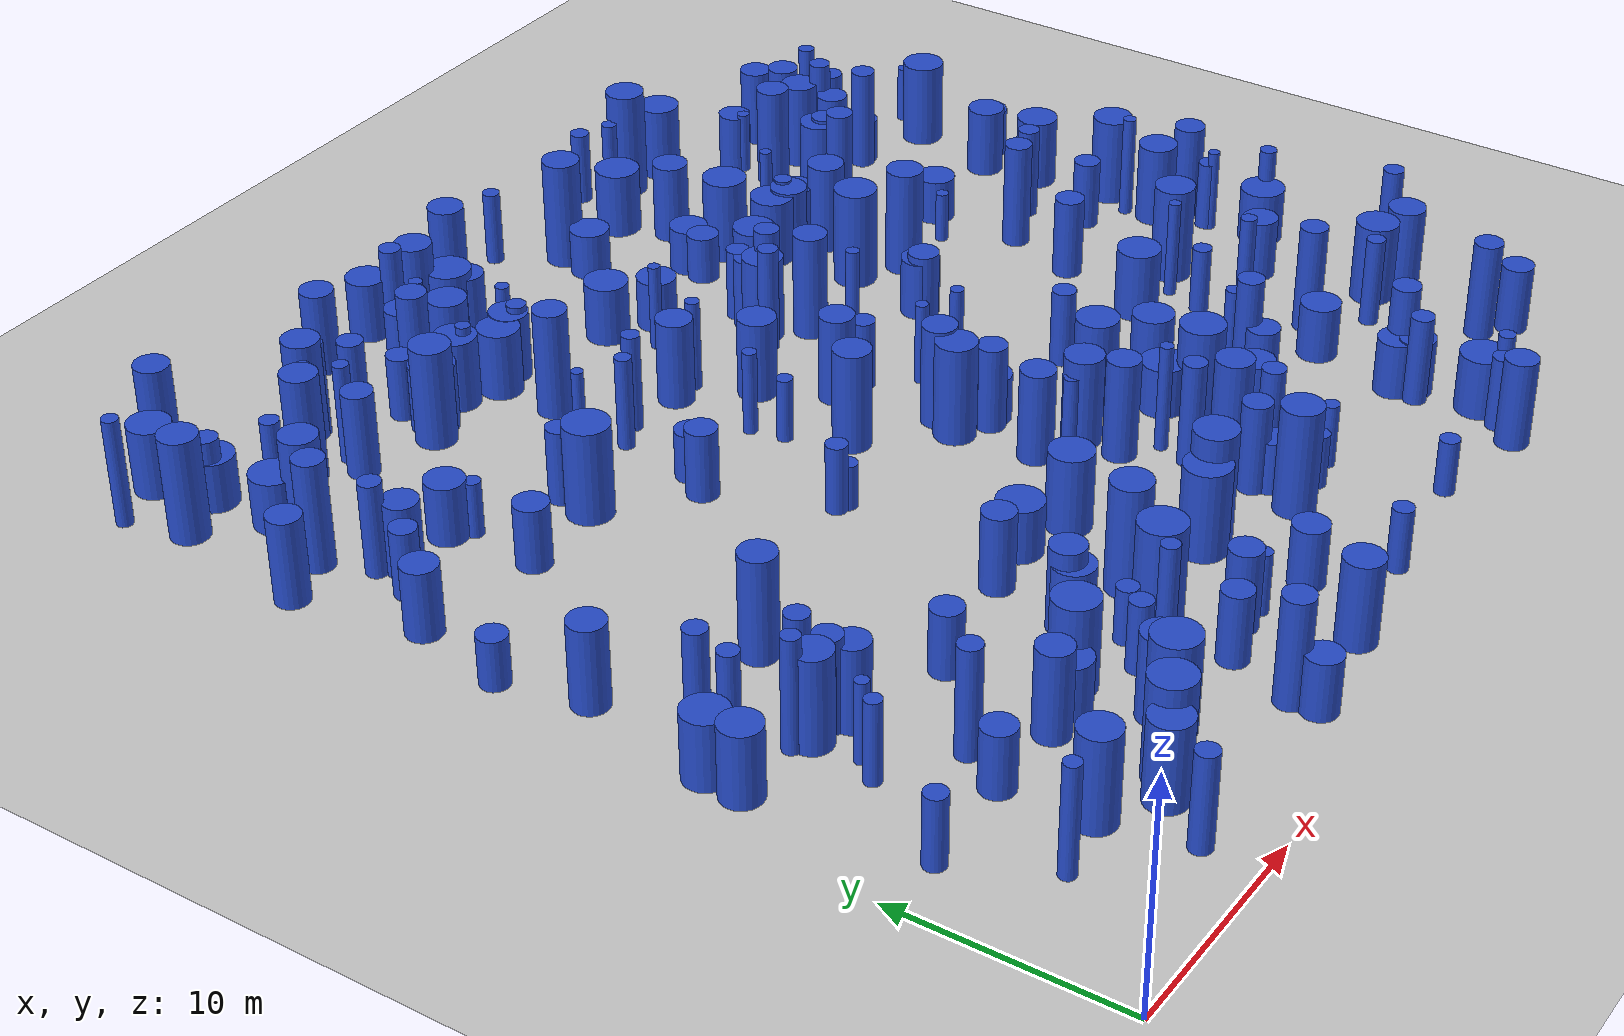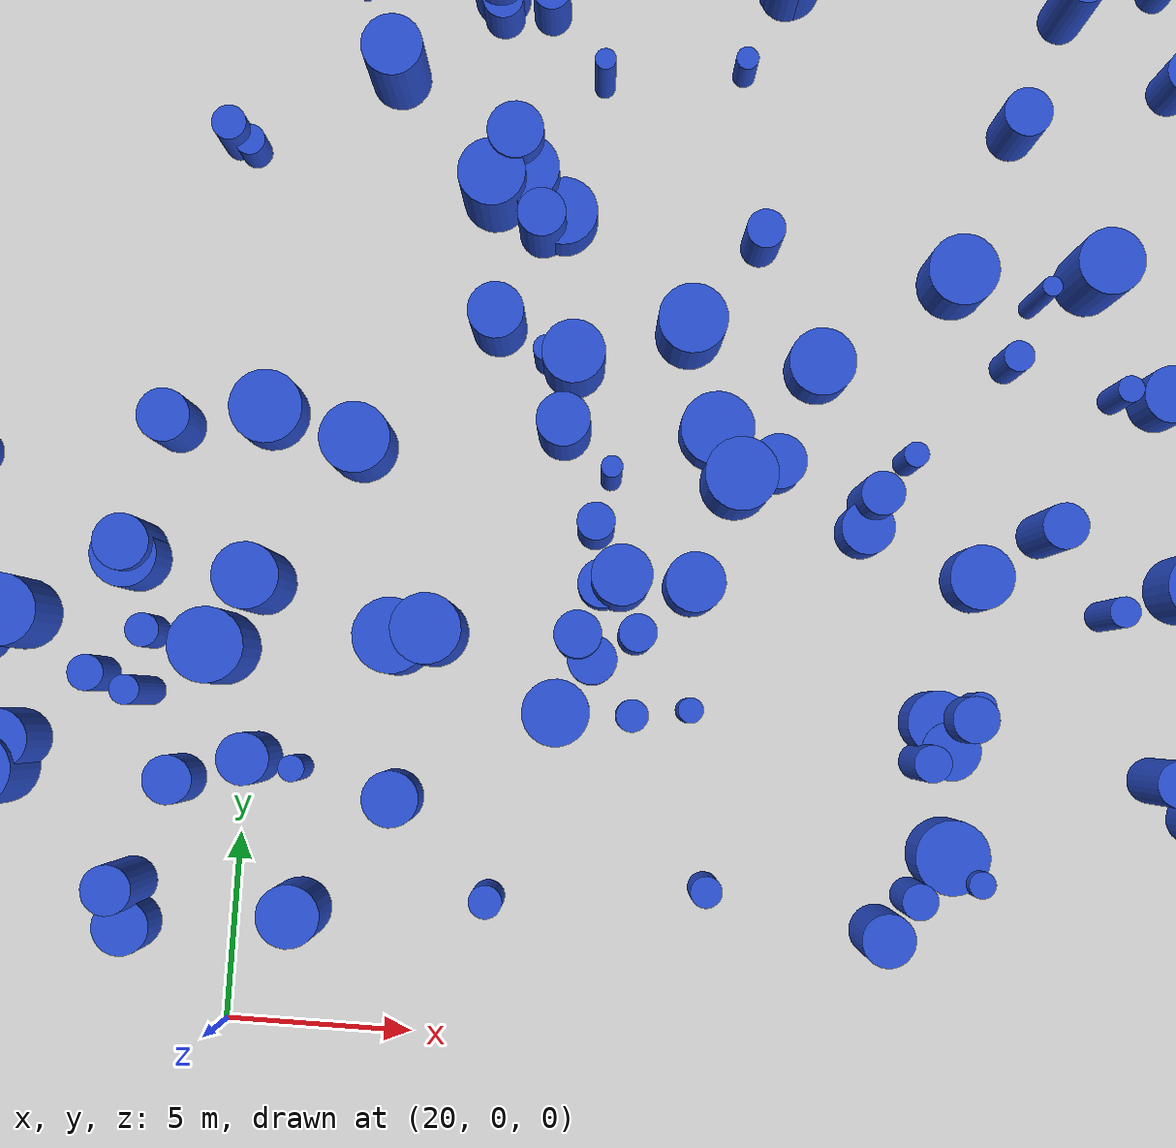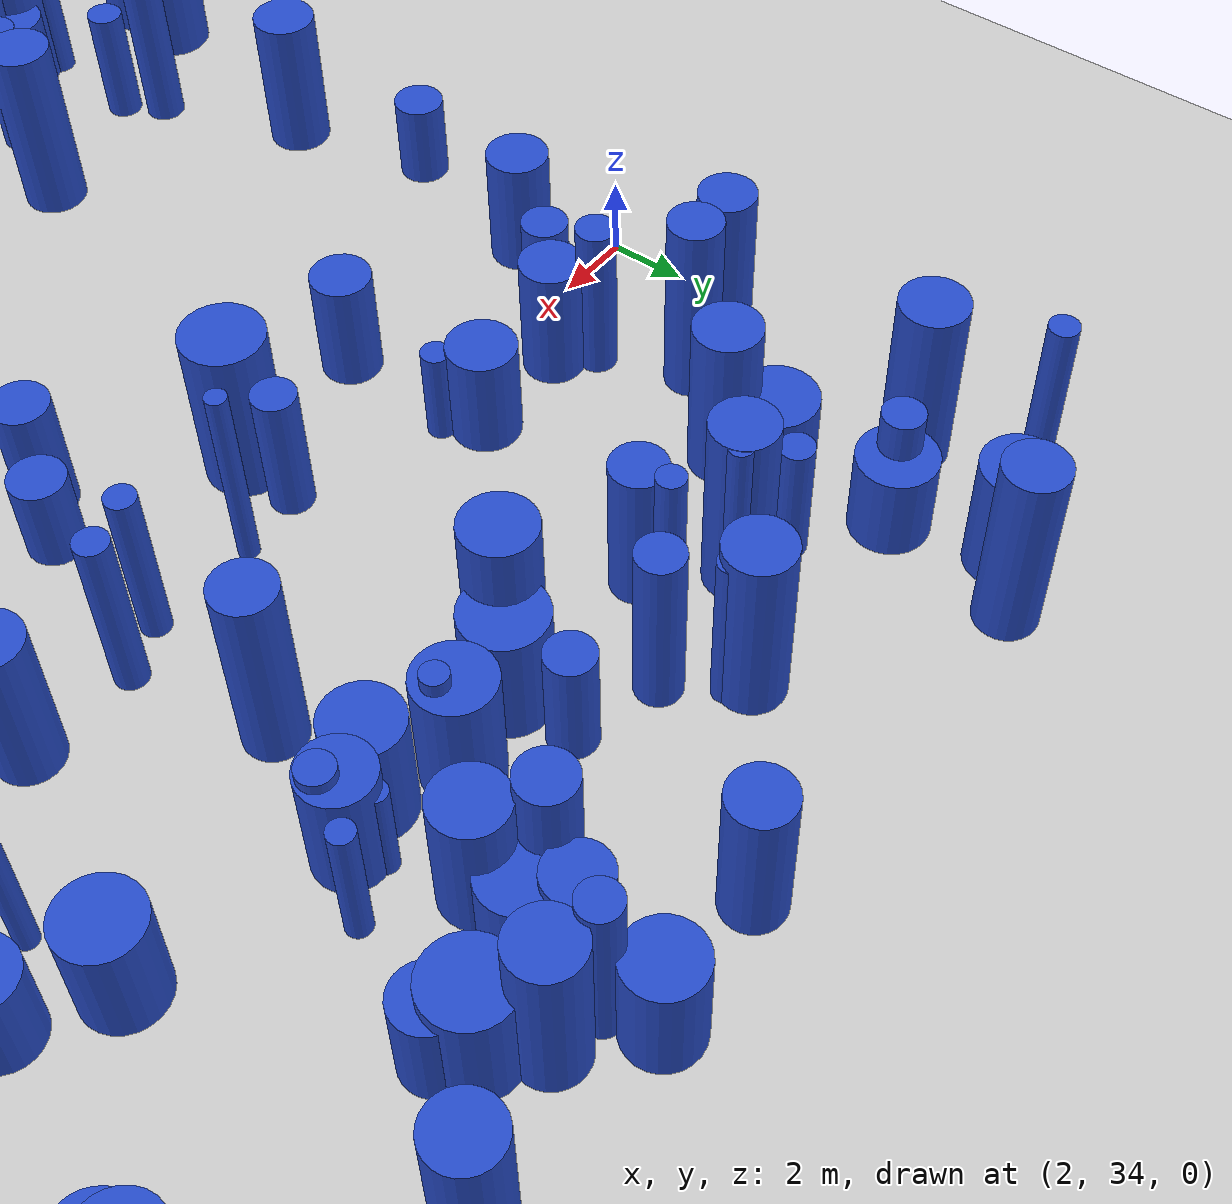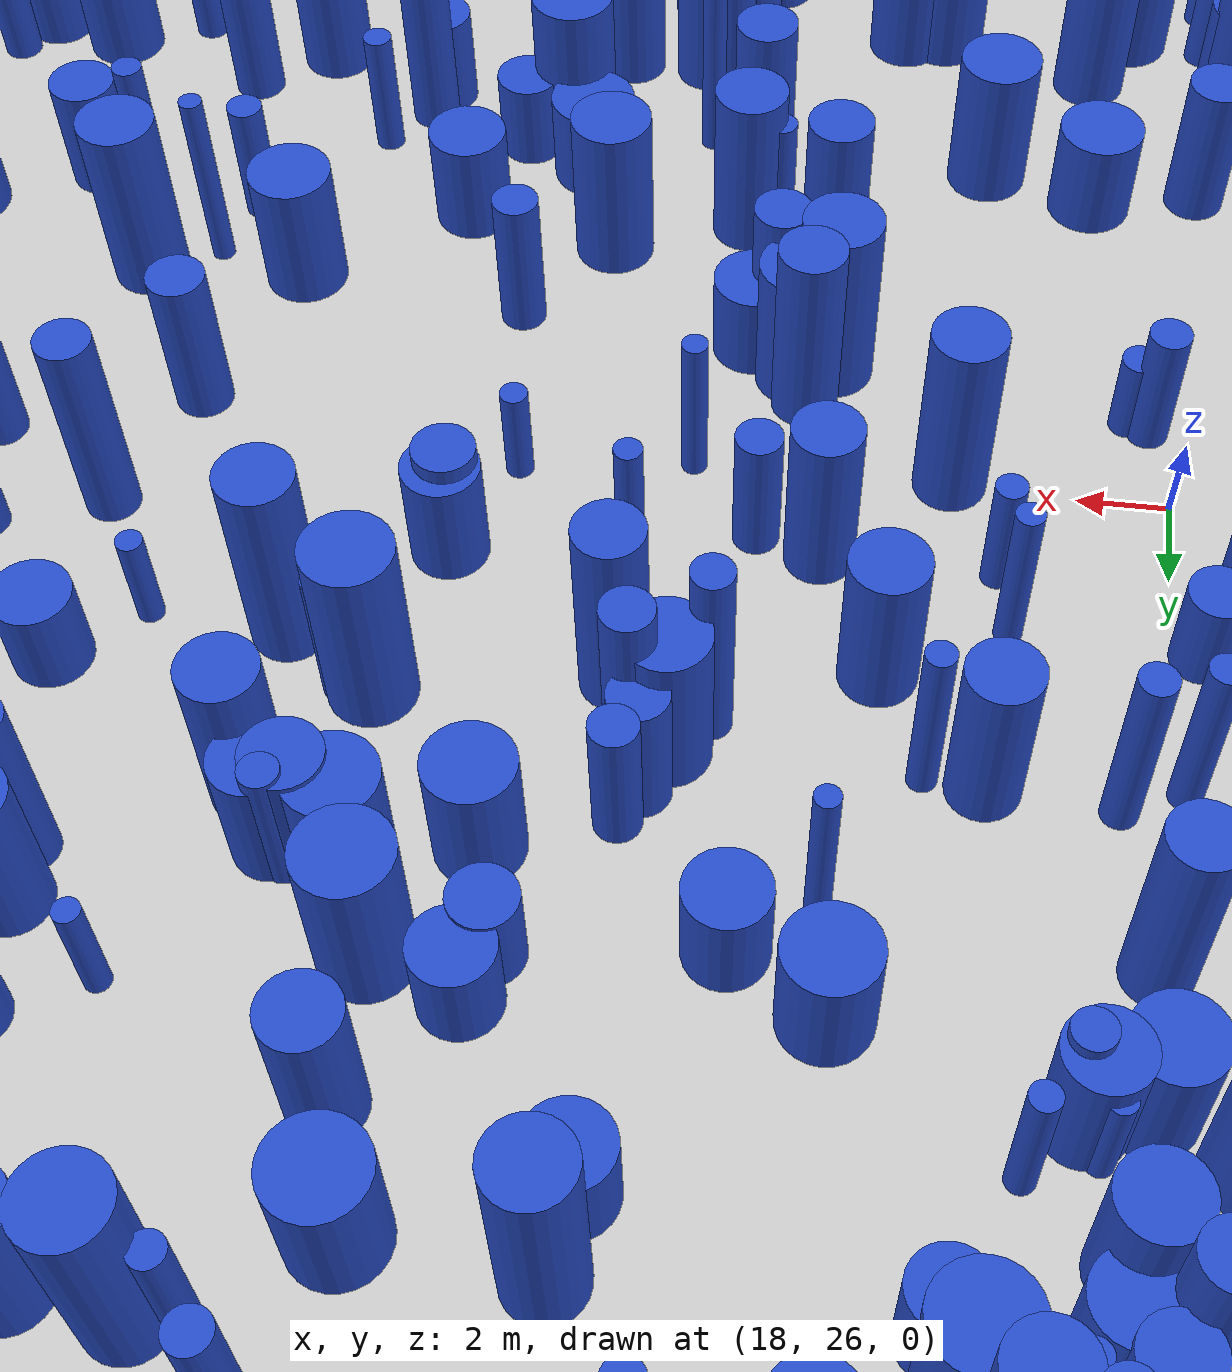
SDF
<sdf version="1.6">
 <world name="default">
  <light name="sun" type="directional">
   <pose>0 0 10 0 -0 0</pose>
   <diffuse>0.8 0.8 0.8 1</diffuse>
   <specular>0.1 0.1 0.1 1</specular>
   <attenuation>
    <range>1000</range>
    <constant>0.9</constant>
    <linear>0.01</linear>
    <quadratic>0.001</quadratic>
   </attenuation>
   <direction>-0.5 0.5 -1</direction>
  </light>
  <model name="ground_plane">
   <static>1</static>
   <link name="link">
    <collision name="collision">
     <geometry><plane><normal>0 0 1</normal><size>100 100</size></plane></geometry>
     <surface><friction><ode><mu>100</mu><mu2>50</mu2></ode></friction></surface>
    </collision>
    <visual name="visual">
     <cast_shadows>0</cast_shadows>
     <geometry><plane><normal>0 0 1</normal><size>100 100</size></plane></geometry>
     <material>
      <script><uri>file://media/materials/scripts/gazebo.material</uri><name>Gazebo/Grey</name></script>
     </material>
    </visual>
   </link>
  </model>
  <gravity>0 0 -9.8</gravity>
  <magnetic_field>6e-06 2.3e-05 -4.2e-05</magnetic_field>
  <atmosphere type="adiabatic"/>
  <physics name="default_physics" default="0" type="ode">
   <max_step_size>0.001</max_step_size>
   <real_time_factor>1</real_time_factor>
   <real_time_update_rate>1000</real_time_update_rate>
  </physics>
  <scene><ambient>0.4 0.4 0.4 1</ambient><background>0.7 0.7 0.7 1</background><shadows>1</shadows></scene>
  <spherical_coordinates>
   <surface_model>EARTH_WGS84</surface_model>
   <latitude_deg>0</latitude_deg>
   <longitude_deg>0</longitude_deg>
   <elevation>0</elevation>
   <heading_deg>0</heading_deg>
  </spherical_coordinates>
  <model name="0">
   <static>0</static>
   <link name="link">
    <inertial>
     <mass>2</mass>
     <inertia><ixx>3.17312</ixx><ixy>0</ixy><ixz>0</ixz><iyy>3.17312</iyy><iyz>0</iyz><izz>0.73489</izz></inertia>
    </inertial>
    <collision name="collision">
     <geometry><cylinder><length>4.10293</length><radius>0.857257</radius></cylinder></geometry>
     <surface><contact><collide_without_contact>1</collide_without_contact></contact></surface>
    </collision>
    <visual name="visual">
     <geometry><cylinder><length>4.10293</length><radius>0.857257</radius></cylinder></geometry>
     <material>
      <script><uri>file://media/materials/scripts/gazebo.material</uri><name>Gazebo/Blue</name></script>
     </material>
    </visual>
    <gravity>0</gravity>
   </link>
   <pose>7.58804 6.08459 2.05146 0 -0 0</pose>
  </model>
  <model name="1">
   <static>0</static>
   <link name="link">
    <inertial>
     <mass>2</mass>
     <inertia><ixx>1.7057</ixx><ixy>0</ixy><ixz>0</ixz><iyy>1.7057</iyy><iyz>0</iyz><izz>0.32089</izz></inertia>
    </inertial>
    <collision name="collision">
     <geometry><cylinder><length>3.04492</length><radius>0.566472</radius></cylinder></geometry>
     <surface><contact><collide_without_contact>1</collide_without_contact></contact></surface>
    </collision>
    <visual name="visual">
     <geometry><cylinder><length>3.04492</length><radius>0.566472</radius></cylinder></geometry>
     <material>
      <script><uri>file://media/materials/scripts/gazebo.material</uri><name>Gazebo/Blue</name></script>
     </material>
    </visual>
    <gravity>0</gravity>
   </link>
   <pose>5.05368 34.1911 1.52246 0 -0 0</pose>
  </model>
  <model name="2">
   <static>0</static>
   <link name="link">
    <inertial>
     <mass>2</mass>
     <inertia><ixx>2.62741</ixx><ixy>0</ixy><ixz>0</ixz><iyy>2.62741</iyy><iyz>0</iyz><izz>0.536153</izz></inertia>
    </inertial>
    <collision name="collision">
     <geometry><cylinder><length>3.76245</length><radius>0.732225</radius></cylinder></geometry>
     <surface><contact><collide_without_contact>1</collide_without_contact></contact></surface>
    </collision>
    <visual name="visual">
     <geometry><cylinder><length>3.76245</length><radius>0.732225</radius></cylinder></geometry>
     <material>
      <script><uri>file://media/materials/scripts/gazebo.material</uri><name>Gazebo/Blue</name></script>
     </material>
    </visual>
    <gravity>0</gravity>
   </link>
   <pose>15.603 47.5677 1.88122 0 -0 0</pose>
  </model>
  <model name="3">
   <static>0</static>
   <link name="link">
    <inertial>
     <mass>2</mass>
     <inertia>
      <ixx>1.36545</ixx>
      <ixy>0</ixy>
      <ixz>0</ixz>
      <iyy>1.36545</iyy>
      <iyz>0</iyz>
      <izz>0.0913502</izz>
     </inertia>
    </inertial>
    <collision name="collision">
     <geometry><cylinder><length>2.81401</length><radius>0.302242</radius></cylinder></geometry>
     <surface><contact><collide_without_contact>1</collide_without_contact></contact></surface>
    </collision>
    <visual name="visual">
     <geometry><cylinder><length>2.81401</length><radius>0.302242</radius></cylinder></geometry>
     <material>
      <script><uri>file://media/materials/scripts/gazebo.material</uri><name>Gazebo/Blue</name></script>
     </material>
    </visual>
    <gravity>0</gravity>
   </link>
   <pose>19.5801 45.6834 1.40701 0 -0 0</pose>
  </model>
  <model name="4">
   <static>0</static>
   <link name="link">
    <inertial>
     <mass>2</mass>
     <inertia><ixx>1.95961</ixx><ixy>0</ixy><ixz>0</ixz><iyy>1.95961</iyy><iyz>0</iyz><izz>0.982624</izz></inertia>
    </inertial>
    <collision name="collision">
     <geometry><cylinder><length>2.96813</length><radius>0.991274</radius></cylinder></geometry>
     <surface><contact><collide_without_contact>1</collide_without_contact></contact></surface>
    </collision>
    <visual name="visual">
     <geometry><cylinder><length>2.96813</length><radius>0.991274</radius></cylinder></geometry>
     <material>
      <script><uri>file://media/materials/scripts/gazebo.material</uri><name>Gazebo/Blue</name></script>
     </material>
    </visual>
    <gravity>0</gravity>
   </link>
   <pose>14.6645 40.756 1.48407 0 -0 0</pose>
  </model>
  <model name="5">
   <static>0</static>
   <link name="link">
    <inertial>
     <mass>2</mass>
     <inertia><ixx>2.61652</ixx><ixy>0</ixy><ixz>0</ixz><iyy>2.61652</iyy><iyz>0</iyz><izz>0.44531</izz></inertia>
    </inertial>
    <collision name="collision">
     <geometry><cylinder><length>3.78988</length><radius>0.667315</radius></cylinder></geometry>
     <surface><contact><collide_without_contact>1</collide_without_contact></contact></surface>
    </collision>
    <visual name="visual">
     <geometry><cylinder><length>3.78988</length><radius>0.667315</radius></cylinder></geometry>
     <material>
      <script><uri>file://media/materials/scripts/gazebo.material</uri><name>Gazebo/Blue</name></script>
     </material>
    </visual>
    <gravity>0</gravity>
   </link>
   <pose>10.4927 41.0038 1.89494 0 -0 0</pose>
  </model>
  <model name="6">
   <static>0</static>
   <link name="link">
    <inertial>
     <mass>2</mass>
     <inertia><ixx>2.11932</ixx><ixy>0</ixy><ixz>0</ixz><iyy>2.11932</iyy><iyz>0</iyz><izz>0.84148</izz></inertia>
    </inertial>
    <collision name="collision">
     <geometry><cylinder><length>3.19241</length><radius>0.917322</radius></cylinder></geometry>
     <surface><contact><collide_without_contact>1</collide_without_contact></contact></surface>
    </collision>
    <visual name="visual">
     <geometry><cylinder><length>3.19241</length><radius>0.917322</radius></cylinder></geometry>
     <material>
      <script><uri>file://media/materials/scripts/gazebo.material</uri><name>Gazebo/Blue</name></script>
     </material>
    </visual>
    <gravity>0</gravity>
   </link>
   <pose>16.6156 41.1221 1.5962 0 -0 0</pose>
  </model>
  <model name="7">
   <static>0</static>
   <link name="link">
    <inertial>
     <mass>2</mass>
     <inertia>
      <ixx>0.928742</ixx>
      <ixy>0</ixy>
      <ixz>0</ixz>
      <iyy>0.928742</iyy>
      <iyz>0</iyz>
      <izz>0.0804717</izz>
     </inertia>
    </inertial>
    <collision name="collision">
     <geometry><cylinder><length>2.3089</length><radius>0.283675</radius></cylinder></geometry>
     <surface><contact><collide_without_contact>1</collide_without_contact></contact></surface>
    </collision>
    <visual name="visual">
     <geometry><cylinder><length>2.3089</length><radius>0.283675</radius></cylinder></geometry>
     <material>
      <script><uri>file://media/materials/scripts/gazebo.material</uri><name>Gazebo/Blue</name></script>
     </material>
    </visual>
    <gravity>0</gravity>
   </link>
   <pose>38.9814 31.6696 1.15445 0 -0 0</pose>
  </model>
  <model name="8">
   <static>0</static>
   <link name="link">
    <inertial>
     <mass>2</mass>
     <inertia><ixx>3.79155</ixx><ixy>0</ixy><ixz>0</ixz><iyy>3.79155</iyy><iyz>0</iyz><izz>0.640544</izz></inertia>
    </inertial>
    <collision name="collision">
     <geometry><cylinder><length>4.56373</length><radius>0.80034</radius></cylinder></geometry>
     <surface><contact><collide_without_contact>1</collide_without_contact></contact></surface>
    </collision>
    <visual name="visual">
     <geometry><cylinder><length>4.56373</length><radius>0.80034</radius></cylinder></geometry>
     <material>
      <script><uri>file://media/materials/scripts/gazebo.material</uri><name>Gazebo/Blue</name></script>
     </material>
    </visual>
    <gravity>0</gravity>
   </link>
   <pose>11.3326 44.5695 2.28187 0 -0 0</pose>
  </model>
  <model name="9">
   <static>0</static>
   <link name="link">
    <inertial>
     <mass>2</mass>
     <inertia><ixx>1.27297</ixx><ixy>0</ixy><ixz>0</ixz><iyy>1.27297</iyy><iyz>0</iyz><izz>0.516849</izz></inertia>
    </inertial>
    <collision name="collision">
     <geometry><cylinder><length>2.46725</length><radius>0.718922</radius></cylinder></geometry>
     <surface><contact><collide_without_contact>1</collide_without_contact></contact></surface>
    </collision>
    <visual name="visual">
     <geometry><cylinder><length>2.46725</length><radius>0.718922</radius></cylinder></geometry>
     <material>
      <script><uri>file://media/materials/scripts/gazebo.material</uri><name>Gazebo/Blue</name></script>
     </material>
    </visual>
    <gravity>0</gravity>
   </link>
   <pose>36.1886 14.3863 1.23362 0 -0 0</pose>
  </model>
  <model name="10">
   <static>0</static>
   <link name="link">
    <inertial>
     <mass>2</mass>
     <inertia><ixx>1.40992</ixx><ixy>0</ixy><ixz>0</ixz><iyy>1.40992</iyy><iyz>0</iyz><izz>0.197939</izz></inertia>
    </inertial>
    <collision name="collision">
     <geometry><cylinder><length>2.80459</length><radius>0.444903</radius></cylinder></geometry>
     <surface><contact><collide_without_contact>1</collide_without_contact></contact></surface>
    </collision>
    <visual name="visual">
     <geometry><cylinder><length>2.80459</length><radius>0.444903</radius></cylinder></geometry>
     <material>
      <script><uri>file://media/materials/scripts/gazebo.material</uri><name>Gazebo/Blue</name></script>
     </material>
    </visual>
    <gravity>0</gravity>
   </link>
   <pose>26.8185 3.79167 1.40229 0 -0 0</pose>
  </model>
  <model name="11">
   <static>0</static>
   <link name="link">
    <inertial>
     <mass>2</mass>
     <inertia><ixx>1.98008</ixx><ixy>0</ixy><ixz>0</ixz><iyy>1.98008</iyy><iyz>0</iyz><izz>0.982956</izz></inertia>
    </inertial>
    <collision name="collision">
     <geometry><cylinder><length>2.98858</length><radius>0.991441</radius></cylinder></geometry>
     <surface><contact><collide_without_contact>1</collide_without_contact></contact></surface>
    </collision>
    <visual name="visual">
     <geometry><cylinder><length>2.98858</length><radius>0.991441</radius></cylinder></geometry>
     <material>
      <script><uri>file://media/materials/scripts/gazebo.material</uri><name>Gazebo/Blue</name></script>
     </material>
    </visual>
    <gravity>0</gravity>
   </link>
   <pose>32.0029 44.3985 1.49429 0 -0 0</pose>
  </model>
  <model name="12">
   <static>0</static>
   <link name="link">
    <inertial>
     <mass>2</mass>
     <inertia><ixx>4.39104</ixx><ixy>0</ixy><ixz>0</ixz><iyy>4.39104</iyy><iyz>0</iyz><izz>0.677612</izz></inertia>
    </inertial>
    <collision name="collision">
     <geometry><cylinder><length>4.93086</length><radius>0.823172</radius></cylinder></geometry>
     <surface><contact><collide_without_contact>1</collide_without_contact></contact></surface>
    </collision>
    <visual name="visual">
     <geometry><cylinder><length>4.93086</length><radius>0.823172</radius></cylinder></geometry>
     <material>
      <script><uri>file://media/materials/scripts/gazebo.material</uri><name>Gazebo/Blue</name></script>
     </material>
    </visual>
    <gravity>0</gravity>
   </link>
   <pose>28.3847 44.6674 2.46543 0 -0 0</pose>
  </model>
  <model name="13">
   <static>0</static>
   <link name="link">
    <inertial>
     <mass>2</mass>
     <inertia><ixx>1.80797</ixx><ixy>0</ixy><ixz>0</ixz><iyy>1.80797</iyy><iyz>0</iyz><izz>0.69155</izz></inertia>
    </inertial>
    <collision name="collision">
     <geometry><cylinder><length>2.96195</length><radius>0.831595</radius></cylinder></geometry>
     <surface><contact><collide_without_contact>1</collide_without_contact></contact></surface>
    </collision>
    <visual name="visual">
     <geometry><cylinder><length>2.96195</length><radius>0.831595</radius></cylinder></geometry>
     <material>
      <script><uri>file://media/materials/scripts/gazebo.material</uri><name>Gazebo/Blue</name></script>
     </material>
    </visual>
    <gravity>0</gravity>
   </link>
   <pose>35.0335 36.8774 1.48097 0 -0 0</pose>
  </model>
  <model name="14">
   <static>0</static>
   <link name="link">
    <inertial>
     <mass>2</mass>
     <inertia><ixx>2.91047</ixx><ixy>0</ixy><ixz>0</ixz><iyy>2.91047</iyy><iyz>0</iyz><izz>0.499162</izz></inertia>
    </inertial>
    <collision name="collision">
     <geometry><cylinder><length>3.99567</length><radius>0.706514</radius></cylinder></geometry>
     <surface><contact><collide_without_contact>1</collide_without_contact></contact></surface>
    </collision>
    <visual name="visual">
     <geometry><cylinder><length>3.99567</length><radius>0.706514</radius></cylinder></geometry>
     <material>
      <script><uri>file://media/materials/scripts/gazebo.material</uri><name>Gazebo/Blue</name></script>
     </material>
    </visual>
    <gravity>0</gravity>
   </link>
   <pose>37.3368 3.64907 1.99783 0 -0 0</pose>
  </model>
  <model name="15">
   <static>0</static>
   <link name="link">
    <inertial>
     <mass>2</mass>
     <inertia><ixx>2.90388</ixx><ixy>0</ixy><ixz>0</ixz><iyy>2.90388</iyy><iyz>0</iyz><izz>0.578559</izz></inertia>
    </inertial>
    <collision name="collision">
     <geometry><cylinder><length>3.96076</length><radius>0.76063</radius></cylinder></geometry>
     <surface><contact><collide_without_contact>1</collide_without_contact></contact></surface>
    </collision>
    <visual name="visual">
     <geometry><cylinder><length>3.96076</length><radius>0.76063</radius></cylinder></geometry>
     <material>
      <script><uri>file://media/materials/scripts/gazebo.material</uri><name>Gazebo/Blue</name></script>
     </material>
    </visual>
    <gravity>0</gravity>
   </link>
   <pose>25.3755 28.3182 1.98038 0 -0 0</pose>
  </model>
  <model name="16">
   <static>0</static>
   <link name="link">
    <inertial>
     <mass>2</mass>
     <inertia><ixx>1.94796</ixx><ixy>0</ixy><ixz>0</ixz><iyy>1.94796</iyy><iyz>0</iyz><izz>0.38834</izz></inertia>
    </inertial>
    <collision name="collision">
     <geometry><cylinder><length>3.24388</length><radius>0.623169</radius></cylinder></geometry>
     <surface><contact><collide_without_contact>1</collide_without_contact></contact></surface>
    </collision>
    <visual name="visual">
     <geometry><cylinder><length>3.24388</length><radius>0.623169</radius></cylinder></geometry>
     <material>
      <script><uri>file://media/materials/scripts/gazebo.material</uri><name>Gazebo/Blue</name></script>
     </material>
    </visual>
    <gravity>0</gravity>
   </link>
   <pose>28.2373 34.7081 1.62194 0 -0 0</pose>
  </model>
  <model name="17">
   <static>0</static>
   <link name="link">
    <inertial>
     <mass>2</mass>
     <inertia><ixx>1.4202</ixx><ixy>0</ixy><ixz>0</ixz><iyy>1.4202</iyy><iyz>0</iyz><izz>0.970689</izz></inertia>
    </inertial>
    <collision name="collision">
     <geometry><cylinder><length>2.36836</length><radius>0.985235</radius></cylinder></geometry>
     <surface><contact><collide_without_contact>1</collide_without_contact></contact></surface>
    </collision>
    <visual name="visual">
     <geometry><cylinder><length>2.36836</length><radius>0.985235</radius></cylinder></geometry>
     <material>
      <script><uri>file://media/materials/scripts/gazebo.material</uri><name>Gazebo/Blue</name></script>
     </material>
    </visual>
    <gravity>0</gravity>
   </link>
   <pose>19.9852 16.4259 1.18418 0 -0 0</pose>
  </model>
  <model name="18">
   <static>0</static>
   <link name="link">
    <inertial>
     <mass>2</mass>
     <inertia><ixx>1.36588</ixx><ixy>0</ixy><ixz>0</ixz><iyy>1.36588</iyy><iyz>0</iyz><izz>0.264625</izz></inertia>
    </inertial>
    <collision name="collision">
     <geometry><cylinder><length>2.72056</length><radius>0.514417</radius></cylinder></geometry>
     <surface><contact><collide_without_contact>1</collide_without_contact></contact></surface>
    </collision>
    <visual name="visual">
     <geometry><cylinder><length>2.72056</length><radius>0.514417</radius></cylinder></geometry>
     <material>
      <script><uri>file://media/materials/scripts/gazebo.material</uri><name>Gazebo/Blue</name></script>
     </material>
    </visual>
    <gravity>0</gravity>
   </link>
   <pose>28.2068 44.8037 1.36028 0 -0 0</pose>
  </model>
  <model name="19">
   <static>0</static>
   <link name="link">
    <inertial>
     <mass>2</mass>
     <inertia><ixx>1.91883</ixx><ixy>0</ixy><ixz>0</ixz><iyy>1.91883</iyy><iyz>0</iyz><izz>0.790618</izz></inertia>
    </inertial>
    <collision name="collision">
     <geometry><cylinder><length>3.02343</length><radius>0.889167</radius></cylinder></geometry>
     <surface><contact><collide_without_contact>1</collide_without_contact></contact></surface>
    </collision>
    <visual name="visual">
     <geometry><cylinder><length>3.02343</length><radius>0.889167</radius></cylinder></geometry>
     <material>
      <script><uri>file://media/materials/scripts/gazebo.material</uri><name>Gazebo/Blue</name></script>
     </material>
    </visual>
    <gravity>0</gravity>
   </link>
   <pose>16.6325 12.2097 1.51172 0 -0 0</pose>
  </model>
  <model name="20">
   <static>0</static>
   <link name="link">
    <inertial>
     <mass>2</mass>
     <inertia><ixx>2.53516</ixx><ixy>0</ixy><ixz>0</ixz><iyy>2.53516</iyy><iyz>0</iyz><izz>0.131135</izz></inertia>
    </inertial>
    <collision name="collision">
     <geometry><cylinder><length>3.84936</length><radius>0.362126</radius></cylinder></geometry>
     <surface><contact><collide_without_contact>1</collide_without_contact></contact></surface>
    </collision>
    <visual name="visual">
     <geometry><cylinder><length>3.84936</length><radius>0.362126</radius></cylinder></geometry>
     <material>
      <script><uri>file://media/materials/scripts/gazebo.material</uri><name>Gazebo/Blue</name></script>
     </material>
    </visual>
    <gravity>0</gravity>
   </link>
   <pose>45.1067 43.0173 1.92468 0 -0 0</pose>
  </model>
  <model name="21">
   <static>0</static>
   <link name="link">
    <inertial>
     <mass>2</mass>
     <inertia><ixx>4.07181</ixx><ixy>0</ixy><ixz>0</ixz><iyy>4.07181</iyy><iyz>0</iyz><izz>0.543778</izz></inertia>
    </inertial>
    <collision name="collision">
     <geometry><cylinder><length>4.77488</length><radius>0.737413</radius></cylinder></geometry>
     <surface><contact><collide_without_contact>1</collide_without_contact></contact></surface>
    </collision>
    <visual name="visual">
     <geometry><cylinder><length>4.77488</length><radius>0.737413</radius></cylinder></geometry>
     <material>
      <script><uri>file://media/materials/scripts/gazebo.material</uri><name>Gazebo/Blue</name></script>
     </material>
    </visual>
    <gravity>0</gravity>
   </link>
   <pose>29.1484 32.1402 2.38744 0 -0 0</pose>
  </model>
  <model name="22">
   <static>0</static>
   <link name="link">
    <inertial>
     <mass>2</mass>
     <inertia><ixx>1.57924</ixx><ixy>0</ixy><ixz>0</ixz><iyy>1.57924</iyy><iyz>0</iyz><izz>0.59029</izz></inertia>
    </inertial>
    <collision name="collision">
     <geometry><cylinder><length>2.77571</length><radius>0.768303</radius></cylinder></geometry>
     <surface><contact><collide_without_contact>1</collide_without_contact></contact></surface>
    </collision>
    <visual name="visual">
     <geometry><cylinder><length>2.77571</length><radius>0.768303</radius></cylinder></geometry>
     <material>
      <script><uri>file://media/materials/scripts/gazebo.material</uri><name>Gazebo/Blue</name></script>
     </material>
    </visual>
    <gravity>0</gravity>
   </link>
   <pose>43.9591 18.4852 1.38785 0 -0 0</pose>
  </model>
  <model name="23">
   <static>0</static>
   <link name="link">
    <inertial>
     <mass>2</mass>
     <inertia><ixx>2.06721</ixx><ixy>0</ixy><ixz>0</ixz><iyy>2.06721</iyy><iyz>0</iyz><izz>0.898479</izz></inertia>
    </inertial>
    <collision name="collision">
     <geometry><cylinder><length>3.11573</length><radius>0.947881</radius></cylinder></geometry>
     <surface><contact><collide_without_contact>1</collide_without_contact></contact></surface>
    </collision>
    <visual name="visual">
     <geometry><cylinder><length>3.11573</length><radius>0.947881</radius></cylinder></geometry>
     <material>
      <script><uri>file://media/materials/scripts/gazebo.material</uri><name>Gazebo/Blue</name></script>
     </material>
    </visual>
    <gravity>0</gravity>
   </link>
   <pose>38.1808 21.3346 1.55787 0 -0 0</pose>
  </model>
  <model name="24">
   <static>0</static>
   <link name="link">
    <inertial>
     <mass>2</mass>
     <inertia><ixx>1.8584</ixx><ixy>0</ixy><ixz>0</ixz><iyy>1.8584</iyy><iyz>0</iyz><izz>0.121468</izz></inertia>
    </inertial>
    <collision name="collision">
     <geometry><cylinder><length>3.2842</length><radius>0.348523</radius></cylinder></geometry>
     <surface><contact><collide_without_contact>1</collide_without_contact></contact></surface>
    </collision>
    <visual name="visual">
     <geometry><cylinder><length>3.2842</length><radius>0.348523</radius></cylinder></geometry>
     <material>
      <script><uri>file://media/materials/scripts/gazebo.material</uri><name>Gazebo/Blue</name></script>
     </material>
    </visual>
    <gravity>0</gravity>
   </link>
   <pose>27.3393 18.4181 1.6421 0 -0 0</pose>
  </model>
  <model name="25">
   <static>0</static>
   <link name="link">
    <inertial>
     <mass>2</mass>
     <inertia><ixx>1.19215</ixx><ixy>0</ixy><ixz>0</ixz><iyy>1.19215</iyy><iyz>0</iyz><izz>0.566845</izz></inertia>
    </inertial>
    <collision name="collision">
     <geometry><cylinder><length>2.33503</length><radius>0.752891</radius></cylinder></geometry>
     <surface><contact><collide_without_contact>1</collide_without_contact></contact></surface>
    </collision>
    <visual name="visual">
     <geometry><cylinder><length>2.33503</length><radius>0.752891</radius></cylinder></geometry>
     <material>
      <script><uri>file://media/materials/scripts/gazebo.material</uri><name>Gazebo/Blue</name></script>
     </material>
    </visual>
    <gravity>0</gravity>
   </link>
   <pose>18.1857 45.3246 1.16752 0 -0 0</pose>
  </model>
  <model name="26">
   <static>0</static>
   <link name="link">
    <inertial>
     <mass>2</mass>
     <inertia><ixx>1.12247</ixx><ixy>0</ixy><ixz>0</ixz><iyy>1.12247</iyy><iyz>0</iyz><izz>0.817696</izz></inertia>
    </inertial>
    <collision name="collision">
     <geometry><cylinder><length>2.06923</length><radius>0.904265</radius></cylinder></geometry>
     <surface><contact><collide_without_contact>1</collide_without_contact></contact></surface>
    </collision>
    <visual name="visual">
     <geometry><cylinder><length>2.06923</length><radius>0.904265</radius></cylinder></geometry>
     <material>
      <script><uri>file://media/materials/scripts/gazebo.material</uri><name>Gazebo/Blue</name></script>
     </material>
    </visual>
    <gravity>0</gravity>
   </link>
   <pose>18.7542 44.3924 1.03462 0 -0 0</pose>
  </model>
  <model name="27">
   <static>0</static>
   <link name="link">
    <inertial>
     <mass>2</mass>
     <inertia><ixx>2.96729</ixx><ixy>0</ixy><ixz>0</ixz><iyy>2.96729</iyy><iyz>0</iyz><izz>0.127909</izz></inertia>
    </inertial>
    <collision name="collision">
     <geometry><cylinder><length>4.17373</length><radius>0.357643</radius></cylinder></geometry>
     <surface><contact><collide_without_contact>1</collide_without_contact></contact></surface>
    </collision>
    <visual name="visual">
     <geometry><cylinder><length>4.17373</length><radius>0.357643</radius></cylinder></geometry>
     <material>
      <script><uri>file://media/materials/scripts/gazebo.material</uri><name>Gazebo/Blue</name></script>
     </material>
    </visual>
    <gravity>0</gravity>
   </link>
   <pose>17.6873 33.3868 2.08686 0 -0 0</pose>
  </model>
  <model name="28">
   <static>0</static>
   <link name="link">
    <inertial>
     <mass>2</mass>
     <inertia><ixx>1.61305</ixx><ixy>0</ixy><ixz>0</ixz><iyy>1.61305</iyy><iyz>0</iyz><izz>0.463081</izz></inertia>
    </inertial>
    <collision name="collision">
     <geometry><cylinder><length>2.87908</length><radius>0.680501</radius></cylinder></geometry>
     <surface><contact><collide_without_contact>1</collide_without_contact></contact></surface>
    </collision>
    <visual name="visual">
     <geometry><cylinder><length>2.87908</length><radius>0.680501</radius></cylinder></geometry>
     <material>
      <script><uri>file://media/materials/scripts/gazebo.material</uri><name>Gazebo/Blue</name></script>
     </material>
    </visual>
    <gravity>0</gravity>
   </link>
   <pose>12.0274 14.794 1.43954 0 -0 0</pose>
  </model>
  <model name="29">
   <static>0</static>
   <link name="link">
    <inertial>
     <mass>2</mass>
     <inertia><ixx>1.64089</ixx><ixy>0</ixy><ixz>0</ixz><iyy>1.64089</iyy><iyz>0</iyz><izz>0.902527</izz></inertia>
    </inertial>
    <collision name="collision">
     <geometry><cylinder><length>2.67166</length><radius>0.950014</radius></cylinder></geometry>
     <surface><contact><collide_without_contact>1</collide_without_contact></contact></surface>
    </collision>
    <visual name="visual">
     <geometry><cylinder><length>2.67166</length><radius>0.950014</radius></cylinder></geometry>
     <material>
      <script><uri>file://media/materials/scripts/gazebo.material</uri><name>Gazebo/Blue</name></script>
     </material>
    </visual>
    <gravity>0</gravity>
   </link>
   <pose>24.1929 39.1758 1.33583 0 -0 0</pose>
  </model>
  <model name="30">
   <static>0</static>
   <link name="link">
    <inertial>
     <mass>2</mass>
     <inertia><ixx>2.57065</ixx><ixy>0</ixy><ixz>0</ixz><iyy>2.57065</iyy><iyz>0</iyz><izz>0.140555</izz></inertia>
    </inertial>
    <collision name="collision">
     <geometry><cylinder><length>3.87327</length><radius>0.374907</radius></cylinder></geometry>
     <surface><contact><collide_without_contact>1</collide_without_contact></contact></surface>
    </collision>
    <visual name="visual">
     <geometry><cylinder><length>3.87327</length><radius>0.374907</radius></cylinder></geometry>
     <material>
      <script><uri>file://media/materials/scripts/gazebo.material</uri><name>Gazebo/Blue</name></script>
     </material>
    </visual>
    <gravity>0</gravity>
   </link>
   <pose>47.8314 20.152 1.93664 0 -0 0</pose>
  </model>
  <model name="31">
   <static>0</static>
   <link name="link">
    <inertial>
     <mass>2</mass>
     <inertia><ixx>1.24573</ixx><ixy>0</ixy><ixz>0</ixz><iyy>1.24573</iyy><iyz>0</iyz><izz>0.741657</izz></inertia>
    </inertial>
    <collision name="collision">
     <geometry><cylinder><length>2.29115</length><radius>0.861195</radius></cylinder></geometry>
     <surface><contact><collide_without_contact>1</collide_without_contact></contact></surface>
    </collision>
    <visual name="visual">
     <geometry><cylinder><length>2.29115</length><radius>0.861195</radius></cylinder></geometry>
     <material>
      <script><uri>file://media/materials/scripts/gazebo.material</uri><name>Gazebo/Blue</name></script>
     </material>
    </visual>
    <gravity>0</gravity>
   </link>
   <pose>26.1555 38.0122 1.14558 0 -0 0</pose>
  </model>
  <model name="32">
   <static>0</static>
   <link name="link">
    <inertial>
     <mass>2</mass>
     <inertia><ixx>3.9654</ixx><ixy>0</ixy><ixz>0</ixz><iyy>3.9654</iyy><iyz>0</iyz><izz>0.125912</izz></inertia>
    </inertial>
    <collision name="collision">
     <geometry><cylinder><length>4.83887</length><radius>0.354841</radius></cylinder></geometry>
     <surface><contact><collide_without_contact>1</collide_without_contact></contact></surface>
    </collision>
    <visual name="visual">
     <geometry><cylinder><length>4.83887</length><radius>0.354841</radius></cylinder></geometry>
     <material>
      <script><uri>file://media/materials/scripts/gazebo.material</uri><name>Gazebo/Blue</name></script>
     </material>
    </visual>
    <gravity>0</gravity>
   </link>
   <pose>4.66651 5.49479 2.41944 0 -0 0</pose>
  </model>
  <model name="33">
   <static>0</static>
   <link name="link">
    <inertial>
     <mass>2</mass>
     <inertia><ixx>3.30687</ixx><ixy>0</ixy><ixz>0</ixz><iyy>3.30687</iyy><iyz>0</iyz><izz>0.069358</izz></inertia>
    </inertial>
    <collision name="collision">
     <geometry><cylinder><length>4.43093</length><radius>0.263359</radius></cylinder></geometry>
     <surface><contact><collide_without_contact>1</collide_without_contact></contact></surface>
    </collision>
    <visual name="visual">
     <geometry><cylinder><length>4.43093</length><radius>0.263359</radius></cylinder></geometry>
     <material>
      <script><uri>file://media/materials/scripts/gazebo.material</uri><name>Gazebo/Blue</name></script>
     </material>
    </visual>
    <gravity>0</gravity>
   </link>
   <pose>40.3358 20.8522 2.21546 0 -0 0</pose>
  </model>
  <model name="34">
   <static>0</static>
   <link name="link">
    <inertial>
     <mass>2</mass>
     <inertia><ixx>3.75987</ixx><ixy>0</ixy><ixz>0</ixz><iyy>3.75987</iyy><iyz>0</iyz><izz>0.248556</izz></inertia>
    </inertial>
    <collision name="collision">
     <geometry><cylinder><length>4.6705</length><radius>0.498554</radius></cylinder></geometry>
     <surface><contact><collide_without_contact>1</collide_without_contact></contact></surface>
    </collision>
    <visual name="visual">
     <geometry><cylinder><length>4.6705</length><radius>0.498554</radius></cylinder></geometry>
     <material>
      <script><uri>file://media/materials/scripts/gazebo.material</uri><name>Gazebo/Blue</name></script>
     </material>
    </visual>
    <gravity>0</gravity>
   </link>
   <pose>30.2781 11.09 2.33525 0 -0 0</pose>
  </model>
  <model name="35">
   <static>0</static>
   <link name="link">
    <inertial>
     <mass>2</mass>
     <inertia><ixx>2.36887</ixx><ixy>0</ixy><ixz>0</ixz><iyy>2.36887</iyy><iyz>0</iyz><izz>0.828005</izz></inertia>
    </inertial>
    <collision name="collision">
     <geometry><cylinder><length>3.42479</length><radius>0.909948</radius></cylinder></geometry>
     <surface><contact><collide_without_contact>1</collide_without_contact></contact></surface>
    </collision>
    <visual name="visual">
     <geometry><cylinder><length>3.42479</length><radius>0.909948</radius></cylinder></geometry>
     <material>
      <script><uri>file://media/materials/scripts/gazebo.material</uri><name>Gazebo/Blue</name></script>
     </material>
    </visual>
    <gravity>0</gravity>
   </link>
   <pose>37.3259 45.9655 1.71239 0 -0 0</pose>
  </model>
  <model name="36">
   <static>0</static>
   <link name="link">
    <inertial>
     <mass>2</mass>
     <inertia><ixx>1.9741</ixx><ixy>0</ixy><ixz>0</ixz><iyy>1.9741</iyy><iyz>0</iyz><izz>0.180988</izz></inertia>
    </inertial>
    <collision name="collision">
     <geometry><cylinder><length>3.36179</length><radius>0.425426</radius></cylinder></geometry>
     <surface><contact><collide_without_contact>1</collide_without_contact></contact></surface>
    </collision>
    <visual name="visual">
     <geometry><cylinder><length>3.36179</length><radius>0.425426</radius></cylinder></geometry>
     <material>
      <script><uri>file://media/materials/scripts/gazebo.material</uri><name>Gazebo/Blue</name></script>
     </material>
    </visual>
    <gravity>0</gravity>
   </link>
   <pose>33.1796 47.3533 1.6809 0 -0 0</pose>
  </model>
  <model name="37">
   <static>0</static>
   <link name="link">
    <inertial>
     <mass>2</mass>
     <inertia><ixx>1.40064</ixx><ixy>0</ixy><ixz>0</ixz><iyy>1.40064</iyy><iyz>0</iyz><izz>0.715011</izz></inertia>
    </inertial>
    <collision name="collision">
     <geometry><cylinder><length>2.50176</length><radius>0.845583</radius></cylinder></geometry>
     <surface><contact><collide_without_contact>1</collide_without_contact></contact></surface>
    </collision>
    <visual name="visual">
     <geometry><cylinder><length>2.50176</length><radius>0.845583</radius></cylinder></geometry>
     <material>
      <script><uri>file://media/materials/scripts/gazebo.material</uri><name>Gazebo/Blue</name></script>
     </material>
    </visual>
    <gravity>0</gravity>
   </link>
   <pose>38.4172 9.37247 1.25088 0 -0 0</pose>
  </model>
  <model name="38">
   <static>0</static>
   <link name="link">
    <inertial>
     <mass>2</mass>
     <inertia><ixx>4.19414</ixx><ixy>0</ixy><ixz>0</ixz><iyy>4.19414</iyy><iyz>0</iyz><izz>0.44377</izz></inertia>
    </inertial>
    <collision name="collision">
     <geometry><cylinder><length>4.88196</length><radius>0.66616</radius></cylinder></geometry>
     <surface><contact><collide_without_contact>1</collide_without_contact></contact></surface>
    </collision>
    <visual name="visual">
     <geometry><cylinder><length>4.88196</length><radius>0.66616</radius></cylinder></geometry>
     <material>
      <script><uri>file://media/materials/scripts/gazebo.material</uri><name>Gazebo/Blue</name></script>
     </material>
    </visual>
    <gravity>0</gravity>
   </link>
   <pose>4.65444 38.2486 2.44098 0 -0 0</pose>
  </model>
  <model name="39">
   <static>0</static>
   <link name="link">
    <inertial>
     <mass>2</mass>
     <inertia><ixx>1.84137</ixx><ixy>0</ixy><ixz>0</ixz><iyy>1.84137</iyy><iyz>0</iyz><izz>0.459908</izz></inertia>
    </inertial>
    <collision name="collision">
     <geometry><cylinder><length>3.10942</length><radius>0.678165</radius></cylinder></geometry>
     <surface><contact><collide_without_contact>1</collide_without_contact></contact></surface>
    </collision>
    <visual name="visual">
     <geometry><cylinder><length>3.10942</length><radius>0.678165</radius></cylinder></geometry>
     <material>
      <script><uri>file://media/materials/scripts/gazebo.material</uri><name>Gazebo/Blue</name></script>
     </material>
    </visual>
    <gravity>0</gravity>
   </link>
   <pose>16.5405 28.8099 1.55471 0 -0 0</pose>
  </model>
  <model name="40">
   <static>0</static>
   <link name="link">
    <inertial>
     <mass>2</mass>
     <inertia><ixx>3.12245</ixx><ixy>0</ixy><ixz>0</ixz><iyy>3.12245</iyy><iyz>0</iyz><izz>0.553682</izz></inertia>
    </inertial>
    <collision name="collision">
     <geometry><cylinder><length>4.13202</length><radius>0.744098</radius></cylinder></geometry>
     <surface><contact><collide_without_contact>1</collide_without_contact></contact></surface>
    </collision>
    <visual name="visual">
     <geometry><cylinder><length>4.13202</length><radius>0.744098</radius></cylinder></geometry>
     <material>
      <script><uri>file://media/materials/scripts/gazebo.material</uri><name>Gazebo/Blue</name></script>
     </material>
    </visual>
    <gravity>0</gravity>
   </link>
   <pose>25.9653 19.207 2.06601 0 -0 0</pose>
  </model>
  <model name="41">
   <static>0</static>
   <link name="link">
    <inertial>
     <mass>2</mass>
     <inertia><ixx>3.05764</ixx><ixy>0</ixy><ixz>0</ixz><iyy>3.05764</iyy><iyz>0</iyz><izz>0.702112</izz></inertia>
    </inertial>
    <collision name="collision">
     <geometry><cylinder><length>4.02983</length><radius>0.837921</radius></cylinder></geometry>
     <surface><contact><collide_without_contact>1</collide_without_contact></contact></surface>
    </collision>
    <visual name="visual">
     <geometry><cylinder><length>4.02983</length><radius>0.837921</radius></cylinder></geometry>
     <material>
      <script><uri>file://media/materials/scripts/gazebo.material</uri><name>Gazebo/Blue</name></script>
     </material>
    </visual>
    <gravity>0</gravity>
   </link>
   <pose>28.0717 18.3011 2.01491 0 -0 0</pose>
  </model>
  <model name="42">
   <static>0</static>
   <link name="link">
    <inertial>
     <mass>2</mass>
     <inertia><ixx>1.13765</ixx><ixy>0</ixy><ixz>0</ixz><iyy>1.13765</iyy><iyz>0</iyz><izz>0.440877</izz></inertia>
    </inertial>
    <collision name="collision">
     <geometry><cylinder><length>2.3459</length><radius>0.663986</radius></cylinder></geometry>
     <surface><contact><collide_without_contact>1</collide_without_contact></contact></surface>
    </collision>
    <visual name="visual">
     <geometry><cylinder><length>2.3459</length><radius>0.663986</radius></cylinder></geometry>
     <material>
      <script><uri>file://media/materials/scripts/gazebo.material</uri><name>Gazebo/Blue</name></script>
     </material>
    </visual>
    <gravity>0</gravity>
   </link>
   <pose>29.1505 10.3498 1.17295 0 -0 0</pose>
  </model>
  <model name="43">
   <static>0</static>
   <link name="link">
    <inertial>
     <mass>2</mass>
     <inertia><ixx>1.8726</ixx><ixy>0</ixy><ixz>0</ixz><iyy>1.8726</iyy><iyz>0</iyz><izz>0.124585</izz></inertia>
    </inertial>
    <collision name="collision">
     <geometry><cylinder><length>3.29574</length><radius>0.352966</radius></cylinder></geometry>
     <surface><contact><collide_without_contact>1</collide_without_contact></contact></surface>
    </collision>
    <visual name="visual">
     <geometry><cylinder><length>3.29574</length><radius>0.352966</radius></cylinder></geometry>
     <material>
      <script><uri>file://media/materials/scripts/gazebo.material</uri><name>Gazebo/Blue</name></script>
     </material>
    </visual>
    <gravity>0</gravity>
   </link>
   <pose>42.7488 18.4765 1.64787 0 -0 0</pose>
  </model>
  <model name="44">
   <static>0</static>
   <link name="link">
    <inertial>
     <mass>2</mass>
     <inertia><ixx>1.7448</ixx><ixy>0</ixy><ixz>0</ixz><iyy>1.7448</iyy><iyz>0</iyz><izz>0.25816</izz></inertia>
    </inertial>
    <collision name="collision">
     <geometry><cylinder><length>3.11357</length><radius>0.508094</radius></cylinder></geometry>
     <surface><contact><collide_without_contact>1</collide_without_contact></contact></surface>
    </collision>
    <visual name="visual">
     <geometry><cylinder><length>3.11357</length><radius>0.508094</radius></cylinder></geometry>
     <material>
      <script><uri>file://media/materials/scripts/gazebo.material</uri><name>Gazebo/Blue</name></script>
     </material>
    </visual>
    <gravity>0</gravity>
   </link>
   <pose>26.7685 27.9284 1.55679 0 -0 0</pose>
  </model>
  <model name="45">
   <static>0</static>
   <link name="link">
    <inertial>
     <mass>2</mass>
     <inertia><ixx>1.28619</ixx><ixy>0</ixy><ixz>0</ixz><iyy>1.28619</iyy><iyz>0</iyz><izz>0.628767</izz></inertia>
    </inertial>
    <collision name="collision">
     <geometry><cylinder><length>2.41471</length><radius>0.792948</radius></cylinder></geometry>
     <surface><contact><collide_without_contact>1</collide_without_contact></contact></surface>
    </collision>
    <visual name="visual">
     <geometry><cylinder><length>2.41471</length><radius>0.792948</radius></cylinder></geometry>
     <material>
      <script><uri>file://media/materials/scripts/gazebo.material</uri><name>Gazebo/Blue</name></script>
     </material>
    </visual>
    <gravity>0</gravity>
   </link>
   <pose>6.54895 17.1856 1.20735 0 -0 0</pose>
  </model>
  <model name="46">
   <static>0</static>
   <link name="link">
    <inertial>
     <mass>2</mass>
     <inertia><ixx>1.39822</ixx><ixy>0</ixy><ixz>0</ixz><iyy>1.39822</iyy><iyz>0</iyz><izz>0.114651</izz></inertia>
    </inertial>
    <collision name="collision">
     <geometry><cylinder><length>2.83643</length><radius>0.338602</radius></cylinder></geometry>
     <surface><contact><collide_without_contact>1</collide_without_contact></contact></surface>
    </collision>
    <visual name="visual">
     <geometry><cylinder><length>2.83643</length><radius>0.338602</radius></cylinder></geometry>
     <material>
      <script><uri>file://media/materials/scripts/gazebo.material</uri><name>Gazebo/Blue</name></script>
     </material>
    </visual>
    <gravity>0</gravity>
   </link>
   <pose>31.8364 9.20339 1.41822 0 -0 0</pose>
  </model>
  <model name="47">
   <static>0</static>
   <link name="link">
    <inertial>
     <mass>2</mass>
     <inertia><ixx>3.0805</ixx><ixy>0</ixy><ixz>0</ixz><iyy>3.0805</iyy><iyz>0</iyz><izz>0.647324</izz></inertia>
    </inertial>
    <collision name="collision">
     <geometry><cylinder><length>4.06707</length><radius>0.804564</radius></cylinder></geometry>
     <surface><contact><collide_without_contact>1</collide_without_contact></contact></surface>
    </collision>
    <visual name="visual">
     <geometry><cylinder><length>4.06707</length><radius>0.804564</radius></cylinder></geometry>
     <material>
      <script><uri>file://media/materials/scripts/gazebo.material</uri><name>Gazebo/Blue</name></script>
     </material>
    </visual>
    <gravity>0</gravity>
   </link>
   <pose>20.3861 46.3769 2.03353 0 -0 0</pose>
  </model>
  <model name="48">
   <static>0</static>
   <link name="link">
    <inertial>
     <mass>2</mass>
     <inertia><ixx>1.82802</ixx><ixy>0</ixy><ixz>0</ixz><iyy>1.82802</iyy><iyz>0</iyz><izz>0.254102</izz></inertia>
    </inertial>
    <collision name="collision">
     <geometry><cylinder><length>3.19465</length><radius>0.504085</radius></cylinder></geometry>
     <surface><contact><collide_without_contact>1</collide_without_contact></contact></surface>
    </collision>
    <visual name="visual">
     <geometry><cylinder><length>3.19465</length><radius>0.504085</radius></cylinder></geometry>
     <material>
      <script><uri>file://media/materials/scripts/gazebo.material</uri><name>Gazebo/Blue</name></script>
     </material>
    </visual>
    <gravity>0</gravity>
   </link>
   <pose>5.44202 44.3514 1.59733 0 -0 0</pose>
  </model>
  <model name="49">
   <static>0</static>
   <link name="link">
    <inertial>
     <mass>2</mass>
     <inertia><ixx>1.03869</ixx><ixy>0</ixy><ixz>0</ixz><iyy>1.03869</iyy><iyz>0</iyz><izz>0.208201</izz></inertia>
    </inertial>
    <collision name="collision">
     <geometry><cylinder><length>2.36803</length><radius>0.45629</radius></cylinder></geometry>
     <surface><contact><collide_without_contact>1</collide_without_contact></contact></surface>
    </collision>
    <visual name="visual">
     <geometry><cylinder><length>2.36803</length><radius>0.45629</radius></cylinder></geometry>
     <material>
      <script><uri>file://media/materials/scripts/gazebo.material</uri><name>Gazebo/Blue</name></script>
     </material>
    </visual>
    <gravity>0</gravity>
   </link>
   <pose>12.9469 31.5137 1.18401 0 -0 0</pose>
  </model>
  <model name="50">
   <static>0</static>
   <link name="link">
    <inertial>
     <mass>2</mass>
     <inertia><ixx>3.72286</ixx><ixy>0</ixy><ixz>0</ixz><iyy>3.72286</iyy><iyz>0</iyz><izz>0.752278</izz></inertia>
    </inertial>
    <collision name="collision">
     <geometry><cylinder><length>4.4811</length><radius>0.86734</radius></cylinder></geometry>
     <surface><contact><collide_without_contact>1</collide_without_contact></contact></surface>
    </collision>
    <visual name="visual">
     <geometry><cylinder><length>4.4811</length><radius>0.86734</radius></cylinder></geometry>
     <material>
      <script><uri>file://media/materials/scripts/gazebo.material</uri><name>Gazebo/Blue</name></script>
     </material>
    </visual>
    <gravity>0</gravity>
   </link>
   <pose>13.9115 40.0974 2.24055 0 -0 0</pose>
  </model>
  <model name="51">
   <static>0</static>
   <link name="link">
    <inertial>
     <mass>2</mass>
     <inertia><ixx>4.04703</ixx><ixy>0</ixy><ixz>0</ixz><iyy>4.04703</iyy><iyz>0</iyz><izz>0.151938</izz></inertia>
    </inertial>
    <collision name="collision">
     <geometry><cylinder><length>4.88122</length><radius>0.389792</radius></cylinder></geometry>
     <surface><contact><collide_without_contact>1</collide_without_contact></contact></surface>
    </collision>
    <visual name="visual">
     <geometry><cylinder><length>4.88122</length><radius>0.389792</radius></cylinder></geometry>
     <material>
      <script><uri>file://media/materials/scripts/gazebo.material</uri><name>Gazebo/Blue</name></script>
     </material>
    </visual>
    <gravity>0</gravity>
   </link>
   <pose>17.2535 8.66033 2.44061 0 -0 0</pose>
  </model>
  <model name="52">
   <static>0</static>
   <link name="link">
    <inertial>
     <mass>2</mass>
     <inertia><ixx>2.45511</ixx><ixy>0</ixy><ixz>0</ixz><iyy>2.45511</iyy><iyz>0</iyz><izz>0.610488</izz></inertia>
    </inertial>
    <collision name="collision">
     <geometry><cylinder><length>3.59154</length><radius>0.781337</radius></cylinder></geometry>
     <surface><contact><collide_without_contact>1</collide_without_contact></contact></surface>
    </collision>
    <visual name="visual">
     <geometry><cylinder><length>3.59154</length><radius>0.781337</radius></cylinder></geometry>
     <material>
      <script><uri>file://media/materials/scripts/gazebo.material</uri><name>Gazebo/Blue</name></script>
     </material>
    </visual>
    <gravity>0</gravity>
   </link>
   <pose>32.7626 42.022 1.79577 0 -0 0</pose>
  </model>
  <model name="53">
   <static>0</static>
   <link name="link">
    <inertial>
     <mass>2</mass>
     <inertia><ixx>1.89191</ixx><ixy>0</ixy><ixz>0</ixz><iyy>1.89191</iyy><iyz>0</iyz><izz>0.1601</izz></inertia>
    </inertial>
    <collision name="collision">
     <geometry><cylinder><length>3.29714</length><radius>0.400125</radius></cylinder></geometry>
     <surface><contact><collide_without_contact>1</collide_without_contact></contact></surface>
    </collision>
    <visual name="visual">
     <geometry><cylinder><length>3.29714</length><radius>0.400125</radius></cylinder></geometry>
     <material>
      <script><uri>file://media/materials/scripts/gazebo.material</uri><name>Gazebo/Blue</name></script>
     </material>
    </visual>
    <gravity>0</gravity>
   </link>
   <pose>34.7148 37.3115 1.64857 0 -0 0</pose>
  </model>
  <model name="54">
   <static>0</static>
   <link name="link">
    <inertial>
     <mass>2</mass>
     <inertia><ixx>1.90004</ixx><ixy>0</ixy><ixz>0</ixz><iyy>1.90004</iyy><iyz>0</iyz><izz>0.889584</izz></inertia>
    </inertial>
    <collision name="collision">
     <geometry><cylinder><length>2.95491</length><radius>0.943178</radius></cylinder></geometry>
     <surface><contact><collide_without_contact>1</collide_without_contact></contact></surface>
    </collision>
    <visual name="visual">
     <geometry><cylinder><length>2.95491</length><radius>0.943178</radius></cylinder></geometry>
     <material>
      <script><uri>file://media/materials/scripts/gazebo.material</uri><name>Gazebo/Blue</name></script>
     </material>
    </visual>
    <gravity>0</gravity>
   </link>
   <pose>2.3369 18.5513 1.47745 0 -0 0</pose>
  </model>
  <model name="55">
   <static>0</static>
   <link name="link">
    <inertial>
     <mass>2</mass>
     <inertia><ixx>2.77636</ixx><ixy>0</ixy><ixz>0</ixz><iyy>2.77636</iyy><iyz>0</iyz><izz>0.243438</izz></inertia>
    </inertial>
    <collision name="collision">
     <geometry><cylinder><length>3.99097</length><radius>0.493394</radius></cylinder></geometry>
     <surface><contact><collide_without_contact>1</collide_without_contact></contact></surface>
    </collision>
    <visual name="visual">
     <geometry><cylinder><length>3.99097</length><radius>0.493394</radius></cylinder></geometry>
     <material>
      <script><uri>file://media/materials/scripts/gazebo.material</uri><name>Gazebo/Blue</name></script>
     </material>
    </visual>
    <gravity>0</gravity>
   </link>
   <pose>4.84616 20.723 1.99548 0 -0 0</pose>
  </model>
  <model name="56">
   <static>0</static>
   <link name="link">
    <inertial>
     <mass>2</mass>
     <inertia><ixx>2.77614</ixx><ixy>0</ixy><ixz>0</ixz><iyy>2.77614</iyy><iyz>0</iyz><izz>0.245795</izz></inertia>
    </inertial>
    <collision name="collision">
     <geometry><cylinder><length>3.98992</length><radius>0.495777</radius></cylinder></geometry>
     <surface><contact><collide_without_contact>1</collide_without_contact></contact></surface>
    </collision>
    <visual name="visual">
     <geometry><cylinder><length>3.98992</length><radius>0.495777</radius></cylinder></geometry>
     <material>
      <script><uri>file://media/materials/scripts/gazebo.material</uri><name>Gazebo/Blue</name></script>
     </material>
    </visual>
    <gravity>0</gravity>
   </link>
   <pose>38.1551 8.28818 1.99496 0 -0 0</pose>
  </model>
  <model name="57">
   <static>0</static>
   <link name="link">
    <inertial>
     <mass>2</mass>
     <inertia><ixx>2.7647</ixx><ixy>0</ixy><ixz>0</ixz><iyy>2.7647</iyy><iyz>0</iyz><izz>0.695099</izz></inertia>
    </inertial>
    <collision name="collision">
     <geometry><cylinder><length>3.80827</length><radius>0.833726</radius></cylinder></geometry>
     <surface><contact><collide_without_contact>1</collide_without_contact></contact></surface>
    </collision>
    <visual name="visual">
     <geometry><cylinder><length>3.80827</length><radius>0.833726</radius></cylinder></geometry>
     <material>
      <script><uri>file://media/materials/scripts/gazebo.material</uri><name>Gazebo/Blue</name></script>
     </material>
    </visual>
    <gravity>0</gravity>
   </link>
   <pose>21.7704 3.10199 1.90413 0 -0 0</pose>
  </model>
  <model name="58">
   <static>0</static>
   <link name="link">
    <inertial>
     <mass>2</mass>
     <inertia><ixx>2.80734</ixx><ixy>0</ixy><ixz>0</ixz><iyy>2.80734</iyy><iyz>0</iyz><izz>0.790535</izz></inertia>
    </inertial>
    <collision name="collision">
     <geometry><cylinder><length>3.80426</length><radius>0.889121</radius></cylinder></geometry>
     <surface><contact><collide_without_contact>1</collide_without_contact></contact></surface>
    </collision>
    <visual name="visual">
     <geometry><cylinder><length>3.80426</length><radius>0.889121</radius></cylinder></geometry>
     <material>
      <script><uri>file://media/materials/scripts/gazebo.material</uri><name>Gazebo/Blue</name></script>
     </material>
    </visual>
    <gravity>0</gravity>
   </link>
   <pose>27.8441 33.6819 1.90213 0 -0 0</pose>
  </model>
  <model name="59">
   <static>0</static>
   <link name="link">
    <inertial>
     <mass>2</mass>
     <inertia><ixx>1.12894</ixx><ixy>0</ixy><ixz>0</ixz><iyy>1.12894</iyy><iyz>0</iyz><izz>0.76588</izz></inertia>
    </inertial>
    <collision name="collision">
     <geometry><cylinder><length>2.11565</length><radius>0.875146</radius></cylinder></geometry>
     <surface><contact><collide_without_contact>1</collide_without_contact></contact></surface>
    </collision>
    <visual name="visual">
     <geometry><cylinder><length>2.11565</length><radius>0.875146</radius></cylinder></geometry>
     <material>
      <script><uri>file://media/materials/scripts/gazebo.material</uri><name>Gazebo/Blue</name></script>
     </material>
    </visual>
    <gravity>0</gravity>
   </link>
   <pose>28.177 43.0977 1.05782 0 -0 0</pose>
  </model>
  <model name="60">
   <static>0</static>
   <link name="link">
    <inertial>
     <mass>2</mass>
     <inertia><ixx>2.52957</ixx><ixy>0</ixy><ixz>0</ixz><iyy>2.52957</iyy><iyz>0</iyz><izz>0.676676</izz></inertia>
    </inertial>
    <collision name="collision">
     <geometry><cylinder><length>3.62593</length><radius>0.822603</radius></cylinder></geometry>
     <surface><contact><collide_without_contact>1</collide_without_contact></contact></surface>
    </collision>
    <visual name="visual">
     <geometry><cylinder><length>3.62593</length><radius>0.822603</radius></cylinder></geometry>
     <material>
      <script><uri>file://media/materials/scripts/gazebo.material</uri><name>Gazebo/Blue</name></script>
     </material>
    </visual>
    <gravity>0</gravity>
   </link>
   <pose>46.8205 12.9395 1.81297 0 -0 0</pose>
  </model>
  <model name="61">
   <static>0</static>
   <link name="link">
    <inertial>
     <mass>2</mass>
     <inertia>
      <ixx>4.01912</ixx>
      <ixy>0</ixy>
      <ixz>0</ixz>
      <iyy>4.01912</iyy>
      <iyz>0</iyz>
      <izz>0.0645632</izz>
     </inertia>
    </inertial>
    <collision name="collision">
     <geometry><cylinder><length>4.89091</length><radius>0.254093</radius></cylinder></geometry>
     <surface><contact><collide_without_contact>1</collide_without_contact></contact></surface>
    </collision>
    <visual name="visual">
     <geometry><cylinder><length>4.89091</length><radius>0.254093</radius></cylinder></geometry>
     <material>
      <script><uri>file://media/materials/scripts/gazebo.material</uri><name>Gazebo/Blue</name></script>
     </material>
    </visual>
    <gravity>0</gravity>
   </link>
   <pose>14.9692 33.5353 2.44546 0 -0 0</pose>
  </model>
  <model name="62">
   <static>0</static>
   <link name="link">
    <inertial>
     <mass>2</mass>
     <inertia><ixx>3.86289</ixx><ixy>0</ixy><ixz>0</ixz><iyy>3.86289</iyy><iyz>0</iyz><izz>0.080667</izz></inertia>
    </inertial>
    <collision name="collision">
     <geometry><cylinder><length>4.78908</length><radius>0.284019</radius></cylinder></geometry>
     <surface><contact><collide_without_contact>1</collide_without_contact></contact></surface>
    </collision>
    <visual name="visual">
     <geometry><cylinder><length>4.78908</length><radius>0.284019</radius></cylinder></geometry>
     <material>
      <script><uri>file://media/materials/scripts/gazebo.material</uri><name>Gazebo/Blue</name></script>
     </material>
    </visual>
    <gravity>0</gravity>
   </link>
   <pose>29.2941 15.3061 2.39454 0 -0 0</pose>
  </model>
  <model name="63">
   <static>0</static>
   <link name="link">
    <inertial>
     <mass>2</mass>
     <inertia><ixx>1.90981</ixx><ixy>0</ixy><ixz>0</ixz><iyy>1.90981</iyy><iyz>0</iyz><izz>0.596313</izz></inertia>
    </inertial>
    <collision name="collision">
     <geometry><cylinder><length>3.10965</length><radius>0.772213</radius></cylinder></geometry>
     <surface><contact><collide_without_contact>1</collide_without_contact></contact></surface>
    </collision>
    <visual name="visual">
     <geometry><cylinder><length>3.10965</length><radius>0.772213</radius></cylinder></geometry>
     <material>
      <script><uri>file://media/materials/scripts/gazebo.material</uri><name>Gazebo/Blue</name></script>
     </material>
    </visual>
    <gravity>0</gravity>
   </link>
   <pose>3.52675 32.1403 1.55483 0 -0 0</pose>
  </model>
  <model name="64">
   <static>0</static>
   <link name="link">
    <inertial>
     <mass>2</mass>
     <inertia><ixx>1.07162</ixx><ixy>0</ixy><ixz>0</ixz><iyy>1.07162</iyy><iyz>0</iyz><izz>0.712238</izz></inertia>
    </inertial>
    <collision name="collision">
     <geometry><cylinder><length>2.07196</length><radius>0.843942</radius></cylinder></geometry>
     <surface><contact><collide_without_contact>1</collide_without_contact></contact></surface>
    </collision>
    <visual name="visual">
     <geometry><cylinder><length>2.07196</length><radius>0.843942</radius></cylinder></geometry>
     <material>
      <script><uri>file://media/materials/scripts/gazebo.material</uri><name>Gazebo/Blue</name></script>
     </material>
    </visual>
    <gravity>0</gravity>
   </link>
   <pose>30.8302 39.6819 1.03598 0 -0 0</pose>
  </model>
  <model name="65">
   <static>0</static>
   <link name="link">
    <inertial>
     <mass>2</mass>
     <inertia><ixx>2.68412</ixx><ixy>0</ixy><ixz>0</ixz><iyy>2.68412</iyy><iyz>0</iyz><izz>0.778534</izz></inertia>
    </inertial>
    <collision name="collision">
     <geometry><cylinder><length>3.71067</length><radius>0.882346</radius></cylinder></geometry>
     <surface><contact><collide_without_contact>1</collide_without_contact></contact></surface>
    </collision>
    <visual name="visual">
     <geometry><cylinder><length>3.71067</length><radius>0.882346</radius></cylinder></geometry>
     <material>
      <script><uri>file://media/materials/scripts/gazebo.material</uri><name>Gazebo/Blue</name></script>
     </material>
    </visual>
    <gravity>0</gravity>
   </link>
   <pose>9.89569 4.60056 1.85534 0 -0 0</pose>
  </model>
  <model name="66">
   <static>0</static>
   <link name="link">
    <inertial>
     <mass>2</mass>
     <inertia><ixx>3.10959</ixx><ixy>0</ixy><ixz>0</ixz><iyy>3.10959</iyy><iyz>0</iyz><izz>0.654406</izz></inertia>
    </inertial>
    <collision name="collision">
     <geometry><cylinder><length>4.08587</length><radius>0.808954</radius></cylinder></geometry>
     <surface><contact><collide_without_contact>1</collide_without_contact></contact></surface>
    </collision>
    <visual name="visual">
     <geometry><cylinder><length>4.08587</length><radius>0.808954</radius></cylinder></geometry>
     <material>
      <script><uri>file://media/materials/scripts/gazebo.material</uri><name>Gazebo/Blue</name></script>
     </material>
    </visual>
    <gravity>0</gravity>
   </link>
   <pose>35.7565 35.7398 2.04293 0 -0 0</pose>
  </model>
  <model name="67">
   <static>0</static>
   <link name="link">
    <inertial>
     <mass>2</mass>
     <inertia><ixx>2.5861</ixx><ixy>0</ixy><ixz>0</ixz><iyy>2.5861</iyy><iyz>0</iyz><izz>0.518654</izz></inertia>
    </inertial>
    <collision name="collision">
     <geometry><cylinder><length>3.7364</length><radius>0.720177</radius></cylinder></geometry>
     <surface><contact><collide_without_contact>1</collide_without_contact></contact></surface>
    </collision>
    <visual name="visual">
     <geometry><cylinder><length>3.7364</length><radius>0.720177</radius></cylinder></geometry>
     <material>
      <script><uri>file://media/materials/scripts/gazebo.material</uri><name>Gazebo/Blue</name></script>
     </material>
    </visual>
    <gravity>0</gravity>
   </link>
   <pose>7.55571 15.9335 1.8682 0 -0 0</pose>
  </model>
  <model name="68">
   <static>0</static>
   <link name="link">
    <inertial>
     <mass>2</mass>
     <inertia><ixx>1.89087</ixx><ixy>0</ixy><ixz>0</ixz><iyy>1.89087</iyy><iyz>0</iyz><izz>0.429731</izz></inertia>
    </inertial>
    <collision name="collision">
     <geometry><cylinder><length>3.17112</length><radius>0.655539</radius></cylinder></geometry>
     <surface><contact><collide_without_contact>1</collide_without_contact></contact></surface>
    </collision>
    <visual name="visual">
     <geometry><cylinder><length>3.17112</length><radius>0.655539</radius></cylinder></geometry>
     <material>
      <script><uri>file://media/materials/scripts/gazebo.material</uri><name>Gazebo/Blue</name></script>
     </material>
    </visual>
    <gravity>0</gravity>
   </link>
   <pose>18.2845 6.37617 1.58556 0 -0 0</pose>
  </model>
  <model name="69">
   <static>0</static>
   <link name="link">
    <inertial>
     <mass>2</mass>
     <inertia><ixx>2.55552</ixx><ixy>0</ixy><ixz>0</ixz><iyy>2.55552</iyy><iyz>0</iyz><izz>0.698081</izz></inertia>
    </inertial>
    <collision name="collision">
     <geometry><cylinder><length>3.63853</length><radius>0.835512</radius></cylinder></geometry>
     <surface><contact><collide_without_contact>1</collide_without_contact></contact></surface>
    </collision>
    <visual name="visual">
     <geometry><cylinder><length>3.63853</length><radius>0.835512</radius></cylinder></geometry>
     <material>
      <script><uri>file://media/materials/scripts/gazebo.material</uri><name>Gazebo/Blue</name></script>
     </material>
    </visual>
    <gravity>0</gravity>
   </link>
   <pose>23.89 31.2537 1.81926 0 -0 0</pose>
  </model>
  <model name="70">
   <static>0</static>
   <link name="link">
    <inertial>
     <mass>2</mass>
     <inertia><ixx>3.78775</ixx><ixy>0</ixy><ixz>0</ixz><iyy>3.78775</iyy><iyz>0</iyz><izz>0.890965</izz></inertia>
    </inertial>
    <collision name="collision">
     <geometry><cylinder><length>4.47813</length><radius>0.943909</radius></cylinder></geometry>
     <surface><contact><collide_without_contact>1</collide_without_contact></contact></surface>
    </collision>
    <visual name="visual">
     <geometry><cylinder><length>4.47813</length><radius>0.943909</radius></cylinder></geometry>
     <material>
      <script><uri>file://media/materials/scripts/gazebo.material</uri><name>Gazebo/Blue</name></script>
     </material>
    </visual>
    <gravity>0</gravity>
   </link>
   <pose>11.0126 5.18411 2.23906 0 -0 0</pose>
  </model>
  <model name="71">
   <static>0</static>
   <link name="link">
    <inertial>
     <mass>2</mass>
     <inertia><ixx>2.80373</ixx><ixy>0</ixy><ixz>0</ixz><iyy>2.80373</iyy><iyz>0</iyz><izz>0.629376</izz></inertia>
    </inertial>
    <collision name="collision">
     <geometry><cylinder><length>3.86449</length><radius>0.793332</radius></cylinder></geometry>
     <surface><contact><collide_without_contact>1</collide_without_contact></contact></surface>
    </collision>
    <visual name="visual">
     <geometry><cylinder><length>3.86449</length><radius>0.793332</radius></cylinder></geometry>
     <material>
      <script><uri>file://media/materials/scripts/gazebo.material</uri><name>Gazebo/Blue</name></script>
     </material>
    </visual>
    <gravity>0</gravity>
   </link>
   <pose>31.6922 12.5394 1.93224 0 -0 0</pose>
  </model>
  <model name="72">
   <static>0</static>
   <link name="link">
    <inertial>
     <mass>2</mass>
     <inertia>
      <ixx>2.14031</ixx>
      <ixy>0</ixy>
      <ixz>0</ixz>
      <iyy>2.14031</iyy>
      <iyz>0</iyz>
      <izz>0.0819198</izz>
     </inertia>
    </inertial>
    <collision name="collision">
     <geometry><cylinder><length>3.5491</length><radius>0.286216</radius></cylinder></geometry>
     <surface><contact><collide_without_contact>1</collide_without_contact></contact></surface>
    </collision>
    <visual name="visual">
     <geometry><cylinder><length>3.5491</length><radius>0.286216</radius></cylinder></geometry>
     <material>
      <script><uri>file://media/materials/scripts/gazebo.material</uri><name>Gazebo/Blue</name></script>
     </material>
    </visual>
    <gravity>0</gravity>
   </link>
   <pose>5.98317 14.5224 1.77455 0 -0 0</pose>
  </model>
  <model name="73">
   <static>0</static>
   <link name="link">
    <inertial>
     <mass>2</mass>
     <inertia><ixx>3.76472</ixx><ixy>0</ixy><ixz>0</ixz><iyy>3.76472</iyy><iyz>0</iyz><izz>0.246582</izz></inertia>
    </inertial>
    <collision name="collision">
     <geometry><cylinder><length>4.67425</length><radius>0.49657</radius></cylinder></geometry>
     <surface><contact><collide_without_contact>1</collide_without_contact></contact></surface>
    </collision>
    <visual name="visual">
     <geometry><cylinder><length>4.67425</length><radius>0.49657</radius></cylinder></geometry>
     <material>
      <script><uri>file://media/materials/scripts/gazebo.material</uri><name>Gazebo/Blue</name></script>
     </material>
    </visual>
    <gravity>0</gravity>
   </link>
   <pose>28.9884 13.8789 2.33712 0 -0 0</pose>
  </model>
  <model name="74">
   <static>0</static>
   <link name="link">
    <inertial>
     <mass>2</mass>
     <inertia><ixx>1.31675</ixx><ixy>0</ixy><ixz>0</ixz><iyy>1.31675</iyy><iyz>0</iyz><izz>0.987604</izz></inertia>
    </inertial>
    <collision name="collision">
     <geometry><cylinder><length>2.22209</length><radius>0.993783</radius></cylinder></geometry>
     <surface><contact><collide_without_contact>1</collide_without_contact></contact></surface>
    </collision>
    <visual name="visual">
     <geometry><cylinder><length>2.22209</length><radius>0.993783</radius></cylinder></geometry>
     <material>
      <script><uri>file://media/materials/scripts/gazebo.material</uri><name>Gazebo/Blue</name></script>
     </material>
    </visual>
    <gravity>0</gravity>
   </link>
   <pose>32.0302 16.745 1.11105 0 -0 0</pose>
  </model>
  <model name="75">
   <static>0</static>
   <link name="link">
    <inertial>
     <mass>2</mass>
     <inertia><ixx>2.73538</ixx><ixy>0</ixy><ixz>0</ixz><iyy>2.73538</iyy><iyz>0</iyz><izz>0.514926</izz></inertia>
    </inertial>
    <collision name="collision">
     <geometry><cylinder><length>3.85584</length><radius>0.717584</radius></cylinder></geometry>
     <surface><contact><collide_without_contact>1</collide_without_contact></contact></surface>
    </collision>
    <visual name="visual">
     <geometry><cylinder><length>3.85584</length><radius>0.717584</radius></cylinder></geometry>
     <material>
      <script><uri>file://media/materials/scripts/gazebo.material</uri><name>Gazebo/Blue</name></script>
     </material>
    </visual>
    <gravity>0</gravity>
   </link>
   <pose>2.41334 37.5859 1.92792 0 -0 0</pose>
  </model>
  <model name="76">
   <static>0</static>
   <link name="link">
    <inertial>
     <mass>2</mass>
     <inertia><ixx>1.44182</ixx><ixy>0</ixy><ixz>0</ixz><iyy>1.44182</iyy><iyz>0</iyz><izz>0.812802</izz></inertia>
    </inertial>
    <collision name="collision">
     <geometry><cylinder><length>2.49249</length><radius>0.901556</radius></cylinder></geometry>
     <surface><contact><collide_without_contact>1</collide_without_contact></contact></surface>
    </collision>
    <visual name="visual">
     <geometry><cylinder><length>2.49249</length><radius>0.901556</radius></cylinder></geometry>
     <material>
      <script><uri>file://media/materials/scripts/gazebo.material</uri><name>Gazebo/Blue</name></script>
     </material>
    </visual>
    <gravity>0</gravity>
   </link>
   <pose>34.6756 18.6978 1.24624 0 -0 0</pose>
  </model>
  <model name="77">
   <static>0</static>
   <link name="link">
    <inertial>
     <mass>2</mass>
     <inertia><ixx>3.09735</ixx><ixy>0</ixy><ixz>0</ixz><iyy>3.09735</iyy><iyz>0</iyz><izz>0.998419</izz></inertia>
    </inertial>
    <collision name="collision">
     <geometry><cylinder><length>3.94827</length><radius>0.999209</radius></cylinder></geometry>
     <surface><contact><collide_without_contact>1</collide_without_contact></contact></surface>
    </collision>
    <visual name="visual">
     <geometry><cylinder><length>3.94827</length><radius>0.999209</radius></cylinder></geometry>
     <material>
      <script><uri>file://media/materials/scripts/gazebo.material</uri><name>Gazebo/Blue</name></script>
     </material>
    </visual>
    <gravity>0</gravity>
   </link>
   <pose>23.8715 10.5656 1.97414 0 -0 0</pose>
  </model>
  <model name="78">
   <static>0</static>
   <link name="link">
    <inertial>
     <mass>2</mass>
     <inertia><ixx>3.89358</ixx><ixy>0</ixy><ixz>0</ixz><iyy>3.89358</iyy><iyz>0</iyz><izz>0.194985</izz></inertia>
    </inertial>
    <collision name="collision">
     <geometry><cylinder><length>4.77247</length><radius>0.441571</radius></cylinder></geometry>
     <surface><contact><collide_without_contact>1</collide_without_contact></contact></surface>
    </collision>
    <visual name="visual">
     <geometry><cylinder><length>4.77247</length><radius>0.441571</radius></cylinder></geometry>
     <material>
      <script><uri>file://media/materials/scripts/gazebo.material</uri><name>Gazebo/Blue</name></script>
     </material>
    </visual>
    <gravity>0</gravity>
   </link>
   <pose>27.1001 32.8841 2.38624 0 -0 0</pose>
  </model>
  <model name="79">
   <static>0</static>
   <link name="link">
    <inertial>
     <mass>2</mass>
     <inertia><ixx>4.49479</ixx><ixy>0</ixy><ixz>0</ixz><iyy>4.49479</iyy><iyz>0</iyz><izz>0.856333</izz></inertia>
    </inertial>
    <collision name="collision">
     <geometry><cylinder><length>4.93961</length><radius>0.925383</radius></cylinder></geometry>
     <surface><contact><collide_without_contact>1</collide_without_contact></contact></surface>
    </collision>
    <visual name="visual">
     <geometry><cylinder><length>4.93961</length><radius>0.925383</radius></cylinder></geometry>
     <material>
      <script><uri>file://media/materials/scripts/gazebo.material</uri><name>Gazebo/Blue</name></script>
     </material>
    </visual>
    <gravity>0</gravity>
   </link>
   <pose>24.8269 10.7923 2.46981 0 -0 0</pose>
  </model>
  <model name="80">
   <static>0</static>
   <link name="link">
    <inertial>
     <mass>2</mass>
     <inertia><ixx>4.09311</ixx><ixy>0</ixy><ixz>0</ixz><iyy>4.09311</iyy><iyz>0</iyz><izz>0.357033</izz></inertia>
    </inertial>
    <collision name="collision">
     <geometry><cylinder><length>4.8464</length><radius>0.597523</radius></cylinder></geometry>
     <surface><contact><collide_without_contact>1</collide_without_contact></contact></surface>
    </collision>
    <visual name="visual">
     <geometry><cylinder><length>4.8464</length><radius>0.597523</radius></cylinder></geometry>
     <material>
      <script><uri>file://media/materials/scripts/gazebo.material</uri><name>Gazebo/Blue</name></script>
     </material>
    </visual>
    <gravity>0</gravity>
   </link>
   <pose>40.6499 28.8101 2.4232 0 -0 0</pose>
  </model>
  <model name="81">
   <static>0</static>
   <link name="link">
    <inertial>
     <mass>2</mass>
     <inertia><ixx>3.58</ixx><ixy>0</ixy><ixz>0</ixz><iyy>3.58</iyy><iyz>0</iyz><izz>0.775805</izz></inertia>
    </inertial>
    <collision name="collision">
     <geometry><cylinder><length>4.37637</length><radius>0.880798</radius></cylinder></geometry>
     <surface><contact><collide_without_contact>1</collide_without_contact></contact></surface>
    </collision>
    <visual name="visual">
     <geometry><cylinder><length>4.37637</length><radius>0.880798</radius></cylinder></geometry>
     <material>
      <script><uri>file://media/materials/scripts/gazebo.material</uri><name>Gazebo/Blue</name></script>
     </material>
    </visual>
    <gravity>0</gravity>
   </link>
   <pose>41.8431 21.6383 2.18818 0 -0 0</pose>
  </model>
  <model name="82">
   <static>0</static>
   <link name="link">
    <inertial>
     <mass>2</mass>
     <inertia><ixx>3.70102</ixx><ixy>0</ixy><ixz>0</ixz><iyy>3.70102</iyy><iyz>0</iyz><izz>0.657066</izz></inertia>
    </inertial>
    <collision name="collision">
     <geometry><cylinder><length>4.49832</length><radius>0.810596</radius></cylinder></geometry>
     <surface><contact><collide_without_contact>1</collide_without_contact></contact></surface>
    </collision>
    <visual name="visual">
     <geometry><cylinder><length>4.49832</length><radius>0.810596</radius></cylinder></geometry>
     <material>
      <script><uri>file://media/materials/scripts/gazebo.material</uri><name>Gazebo/Blue</name></script>
     </material>
    </visual>
    <gravity>0</gravity>
   </link>
   <pose>22.7638 25.8733 2.24916 0 -0 0</pose>
  </model>
  <model name="83">
   <static>0</static>
   <link name="link">
    <inertial>
     <mass>2</mass>
     <inertia><ixx>1.72502</ixx><ixy>0</ixy><ixz>0</ixz><iyy>1.72502</iyy><iyz>0</iyz><izz>0.220377</izz></inertia>
    </inertial>
    <collision name="collision">
     <geometry><cylinder><length>3.11272</length><radius>0.469444</radius></cylinder></geometry>
     <surface><contact><collide_without_contact>1</collide_without_contact></contact></surface>
    </collision>
    <visual name="visual">
     <geometry><cylinder><length>3.11272</length><radius>0.469444</radius></cylinder></geometry>
     <material>
      <script><uri>file://media/materials/scripts/gazebo.material</uri><name>Gazebo/Blue</name></script>
     </material>
    </visual>
    <gravity>0</gravity>
   </link>
   <pose>26.6132 23.1771 1.55636 0 -0 0</pose>
  </model>
  <model name="84">
   <static>0</static>
   <link name="link">
    <inertial>
     <mass>2</mass>
     <inertia><ixx>1.40467</ixx><ixy>0</ixy><ixz>0</ixz><iyy>1.40467</iyy><iyz>0</iyz><izz>0.752602</izz></inertia>
    </inertial>
    <collision name="collision">
     <geometry><cylinder><length>2.484</length><radius>0.867526</radius></cylinder></geometry>
     <surface><contact><collide_without_contact>1</collide_without_contact></contact></surface>
    </collision>
    <visual name="visual">
     <geometry><cylinder><length>2.484</length><radius>0.867526</radius></cylinder></geometry>
     <material>
      <script><uri>file://media/materials/scripts/gazebo.material</uri><name>Gazebo/Blue</name></script>
     </material>
    </visual>
    <gravity>0</gravity>
   </link>
   <pose>39.2948 13.2887 1.242 0 -0 0</pose>
  </model>
  <model name="85">
   <static>0</static>
   <link name="link">
    <inertial>
     <mass>2</mass>
     <inertia><ixx>3.49017</ixx><ixy>0</ixy><ixz>0</ixz><iyy>3.49017</iyy><iyz>0</iyz><izz>0.329145</izz></inertia>
    </inertial>
    <collision name="collision">
     <geometry><cylinder><length>4.46694</length><radius>0.573711</radius></cylinder></geometry>
     <surface><contact><collide_without_contact>1</collide_without_contact></contact></surface>
    </collision>
    <visual name="visual">
     <geometry><cylinder><length>4.46694</length><radius>0.573711</radius></cylinder></geometry>
     <material>
      <script><uri>file://media/materials/scripts/gazebo.material</uri><name>Gazebo/Blue</name></script>
     </material>
    </visual>
    <gravity>0</gravity>
   </link>
   <pose>36.3377 15.1662 2.23347 0 -0 0</pose>
  </model>
  <model name="86">
   <static>0</static>
   <link name="link">
    <inertial>
     <mass>2</mass>
     <inertia><ixx>3.21751</ixx><ixy>0</ixy><ixz>0</ixz><iyy>3.21751</iyy><iyz>0</iyz><izz>0.937434</izz></inertia>
    </inertial>
    <collision name="collision">
     <geometry><cylinder><length>4.06113</length><radius>0.968212</radius></cylinder></geometry>
     <surface><contact><collide_without_contact>1</collide_without_contact></contact></surface>
    </collision>
    <visual name="visual">
     <geometry><cylinder><length>4.06113</length><radius>0.968212</radius></cylinder></geometry>
     <material>
      <script><uri>file://media/materials/scripts/gazebo.material</uri><name>Gazebo/Blue</name></script>
     </material>
    </visual>
    <gravity>0</gravity>
   </link>
   <pose>32.678 15.4378 2.03056 0 -0 0</pose>
  </model>
  <model name="87">
   <static>0</static>
   <link name="link">
    <inertial>
     <mass>2</mass>
     <inertia><ixx>3.67503</ixx><ixy>0</ixy><ixz>0</ixz><iyy>3.67503</iyy><iyz>0</iyz><izz>0.375093</izz></inertia>
    </inertial>
    <collision name="collision">
     <geometry><cylinder><length>4.57438</length><radius>0.612449</radius></cylinder></geometry>
     <surface><contact><collide_without_contact>1</collide_without_contact></contact></surface>
    </collision>
    <visual name="visual">
     <geometry><cylinder><length>4.57438</length><radius>0.612449</radius></cylinder></geometry>
     <material>
      <script><uri>file://media/materials/scripts/gazebo.material</uri><name>Gazebo/Blue</name></script>
     </material>
    </visual>
    <gravity>0</gravity>
   </link>
   <pose>39.1185 9.50493 2.28719 0 -0 0</pose>
  </model>
  <model name="88">
   <static>0</static>
   <link name="link">
    <inertial>
     <mass>2</mass>
     <inertia><ixx>4.23171</ixx><ixy>0</ixy><ixz>0</ixz><iyy>4.23171</iyy><iyz>0</iyz><izz>0.655264</izz></inertia>
    </inertial>
    <collision name="collision">
     <geometry><cylinder><length>4.83988</length><radius>0.809484</radius></cylinder></geometry>
     <surface><contact><collide_without_contact>1</collide_without_contact></contact></surface>
    </collision>
    <visual name="visual">
     <geometry><cylinder><length>4.83988</length><radius>0.809484</radius></cylinder></geometry>
     <material>
      <script><uri>file://media/materials/scripts/gazebo.material</uri><name>Gazebo/Blue</name></script>
     </material>
    </visual>
    <gravity>0</gravity>
   </link>
   <pose>35.9826 31.7684 2.41994 0 -0 0</pose>
  </model>
  <model name="89">
   <static>0</static>
   <link name="link">
    <inertial>
     <mass>2</mass>
     <inertia>
      <ixx>2.40436</ixx>
      <ixy>0</ixy>
      <ixz>0</ixz>
      <iyy>2.40436</iyy>
      <iyz>0</iyz>
      <izz>0.0933567</izz>
     </inertia>
    </inertial>
    <collision name="collision">
     <geometry><cylinder><length>3.76113</length><radius>0.305543</radius></cylinder></geometry>
     <surface><contact><collide_without_contact>1</collide_without_contact></contact></surface>
    </collision>
    <visual name="visual">
     <geometry><cylinder><length>3.76113</length><radius>0.305543</radius></cylinder></geometry>
     <material>
      <script><uri>file://media/materials/scripts/gazebo.material</uri><name>Gazebo/Blue</name></script>
     </material>
    </visual>
    <gravity>0</gravity>
   </link>
   <pose>21.3115 29.8257 1.88056 0 -0 0</pose>
  </model>
  <model name="90">
   <static>0</static>
   <link name="link">
    <inertial>
     <mass>2</mass>
     <inertia><ixx>3.38084</ixx><ixy>0</ixy><ixz>0</ixz><iyy>3.38084</iyy><iyz>0</iyz><izz>0.117593</izz></inertia>
    </inertial>
    <collision name="collision">
     <geometry><cylinder><length>4.46456</length><radius>0.342918</radius></cylinder></geometry>
     <surface><contact><collide_without_contact>1</collide_without_contact></contact></surface>
    </collision>
    <visual name="visual">
     <geometry><cylinder><length>4.46456</length><radius>0.342918</radius></cylinder></geometry>
     <material>
      <script><uri>file://media/materials/scripts/gazebo.material</uri><name>Gazebo/Blue</name></script>
     </material>
    </visual>
    <gravity>0</gravity>
   </link>
   <pose>10.8516 42.0753 2.23228 0 -0 0</pose>
  </model>
  <model name="91">
   <static>0</static>
   <link name="link">
    <inertial>
     <mass>2</mass>
     <inertia><ixx>1.88416</ixx><ixy>0</ixy><ixz>0</ixz><iyy>1.88416</iyy><iyz>0</iyz><izz>0.248682</izz></inertia>
    </inertial>
    <collision name="collision">
     <geometry><cylinder><length>3.24945</length><radius>0.498681</radius></cylinder></geometry>
     <surface><contact><collide_without_contact>1</collide_without_contact></contact></surface>
    </collision>
    <visual name="visual">
     <geometry><cylinder><length>3.24945</length><radius>0.498681</radius></cylinder></geometry>
     <material>
      <script><uri>file://media/materials/scripts/gazebo.material</uri><name>Gazebo/Blue</name></script>
     </material>
    </visual>
    <gravity>0</gravity>
   </link>
   <pose>28.5794 35.4647 1.62472 0 -0 0</pose>
  </model>
  <model name="92">
   <static>0</static>
   <link name="link">
    <inertial>
     <mass>2</mass>
     <inertia><ixx>1.49245</ixx><ixy>0</ixy><ixz>0</ixz><iyy>1.49245</iyy><iyz>0</iyz><izz>0.959766</izz></inertia>
    </inertial>
    <collision name="collision">
     <geometry><cylinder><length>2.46483</length><radius>0.979676</radius></cylinder></geometry>
     <surface><contact><collide_without_contact>1</collide_without_contact></contact></surface>
    </collision>
    <visual name="visual">
     <geometry><cylinder><length>2.46483</length><radius>0.979676</radius></cylinder></geometry>
     <material>
      <script><uri>file://media/materials/scripts/gazebo.material</uri><name>Gazebo/Blue</name></script>
     </material>
    </visual>
    <gravity>0</gravity>
   </link>
   <pose>46.9538 19.8742 1.23241 0 -0 0</pose>
  </model>
  <model name="93">
   <static>0</static>
   <link name="link">
    <inertial>
     <mass>2</mass>
     <inertia><ixx>2.00699</ixx><ixy>0</ixy><ixz>0</ixz><iyy>2.00699</iyy><iyz>0</iyz><izz>0.571679</izz></inertia>
    </inertial>
    <collision name="collision">
     <geometry><cylinder><length>3.21355</length><radius>0.756095</radius></cylinder></geometry>
     <surface><contact><collide_without_contact>1</collide_without_contact></contact></surface>
    </collision>
    <visual name="visual">
     <geometry><cylinder><length>3.21355</length><radius>0.756095</radius></cylinder></geometry>
     <material>
      <script><uri>file://media/materials/scripts/gazebo.material</uri><name>Gazebo/Blue</name></script>
     </material>
    </visual>
    <gravity>0</gravity>
   </link>
   <pose>6.21176 35.2915 1.60678 0 -0 0</pose>
  </model>
  <model name="94">
   <static>0</static>
   <link name="link">
    <inertial>
     <mass>2</mass>
     <inertia>
      <ixx>2.56569</ixx>
      <ixy>0</ixy>
      <ixz>0</ixz>
      <iyy>2.56569</iyy>
      <iyz>0</iyz>
      <izz>0.0685873</izz>
     </inertia>
    </inertial>
    <collision name="collision">
     <geometry><cylinder><length>3.89722</length><radius>0.261892</radius></cylinder></geometry>
     <surface><contact><collide_without_contact>1</collide_without_contact></contact></surface>
    </collision>
    <visual name="visual">
     <geometry><cylinder><length>3.89722</length><radius>0.261892</radius></cylinder></geometry>
     <material>
      <script><uri>file://media/materials/scripts/gazebo.material</uri><name>Gazebo/Blue</name></script>
     </material>
    </visual>
    <gravity>0</gravity>
   </link>
   <pose>24.5646 36.8898 1.94861 0 -0 0</pose>
  </model>
  <model name="95">
   <static>0</static>
   <link name="link">
    <inertial>
     <mass>2</mass>
     <inertia><ixx>2.48153</ixx><ixy>0</ixy><ixz>0</ixz><iyy>2.48153</iyy><iyz>0</iyz><izz>0.885892</izz></inertia>
    </inertial>
    <collision name="collision">
     <geometry><cylinder><length>3.49736</length><radius>0.941218</radius></cylinder></geometry>
     <surface><contact><collide_without_contact>1</collide_without_contact></contact></surface>
    </collision>
    <visual name="visual">
     <geometry><cylinder><length>3.49736</length><radius>0.941218</radius></cylinder></geometry>
     <material>
      <script><uri>file://media/materials/scripts/gazebo.material</uri><name>Gazebo/Blue</name></script>
     </material>
    </visual>
    <gravity>0</gravity>
   </link>
   <pose>22.5044 15.6831 1.74868 0 -0 0</pose>
  </model>
  <model name="96">
   <static>0</static>
   <link name="link">
    <inertial>
     <mass>2</mass>
     <inertia><ixx>3.12972</ixx><ixy>0</ixy><ixz>0</ixz><iyy>3.12972</iyy><iyz>0</iyz><izz>0.918622</izz></inertia>
    </inertial>
    <collision name="collision">
     <geometry><cylinder><length>4.00281</length><radius>0.958448</radius></cylinder></geometry>
     <surface><contact><collide_without_contact>1</collide_without_contact></contact></surface>
    </collision>
    <visual name="visual">
     <geometry><cylinder><length>4.00281</length><radius>0.958448</radius></cylinder></geometry>
     <material>
      <script><uri>file://media/materials/scripts/gazebo.material</uri><name>Gazebo/Blue</name></script>
     </material>
    </visual>
    <gravity>0</gravity>
   </link>
   <pose>13.7137 10.487 2.0014 0 -0 0</pose>
  </model>
  <model name="97">
   <static>0</static>
   <link name="link">
    <inertial>
     <mass>2</mass>
     <inertia><ixx>1.05903</ixx><ixy>0</ixy><ixz>0</ixz><iyy>1.05903</iyy><iyz>0</iyz><izz>0.709056</izz></inertia>
    </inertial>
    <collision name="collision">
     <geometry><cylinder><length>2.05596</length><radius>0.842054</radius></cylinder></geometry>
     <surface><contact><collide_without_contact>1</collide_without_contact></contact></surface>
    </collision>
    <visual name="visual">
     <geometry><cylinder><length>2.05596</length><radius>0.842054</radius></cylinder></geometry>
     <material>
      <script><uri>file://media/materials/scripts/gazebo.material</uri><name>Gazebo/Blue</name></script>
     </material>
    </visual>
    <gravity>0</gravity>
   </link>
   <pose>40.648 33.0252 1.02798 0 -0 0</pose>
  </model>
  <model name="98">
   <static>0</static>
   <link name="link">
    <inertial>
     <mass>2</mass>
     <inertia><ixx>3.96173</ixx><ixy>0</ixy><ixz>0</ixz><iyy>3.96173</iyy><iyz>0</iyz><izz>0.434607</izz></inertia>
    </inertial>
    <collision name="collision">
     <geometry><cylinder><length>4.73989</length><radius>0.659247</radius></cylinder></geometry>
     <surface><contact><collide_without_contact>1</collide_without_contact></contact></surface>
    </collision>
    <visual name="visual">
     <geometry><cylinder><length>4.73989</length><radius>0.659247</radius></cylinder></geometry>
     <material>
      <script><uri>file://media/materials/scripts/gazebo.material</uri><name>Gazebo/Blue</name></script>
     </material>
    </visual>
    <gravity>0</gravity>
   </link>
   <pose>17.1698 3.49956 2.36994 0 -0 0</pose>
  </model>
  <model name="99">
   <static>0</static>
   <link name="link">
    <inertial>
     <mass>2</mass>
     <inertia><ixx>3.91172</ixx><ixy>0</ixy><ixz>0</ixz><iyy>3.91172</iyy><iyz>0</iyz><izz>0.672515</izz></inertia>
    </inertial>
    <collision name="collision">
     <geometry><cylinder><length>4.63171</length><radius>0.82007</radius></cylinder></geometry>
     <surface><contact><collide_without_contact>1</collide_without_contact></contact></surface>
    </collision>
    <visual name="visual">
     <geometry><cylinder><length>4.63171</length><radius>0.82007</radius></cylinder></geometry>
     <material>
      <script><uri>file://media/materials/scripts/gazebo.material</uri><name>Gazebo/Blue</name></script>
     </material>
    </visual>
    <gravity>0</gravity>
   </link>
   <pose>3.48026 43.7493 2.31586 0 -0 0</pose>
  </model>
  <model name="100">
   <static>0</static>
   <link name="link">
    <inertial>
     <mass>2</mass>
     <inertia><ixx>3.05003</ixx><ixy>0</ixy><ixz>0</ixz><iyy>3.05003</iyy><iyz>0</iyz><izz>0.222899</izz></inertia>
    </inertial>
    <collision name="collision">
     <geometry><cylinder><length>4.19899</length><radius>0.472122</radius></cylinder></geometry>
     <surface><contact><collide_without_contact>1</collide_without_contact></contact></surface>
    </collision>
    <visual name="visual">
     <geometry><cylinder><length>4.19899</length><radius>0.472122</radius></cylinder></geometry>
     <material>
      <script><uri>file://media/materials/scripts/gazebo.material</uri><name>Gazebo/Blue</name></script>
     </material>
    </visual>
    <gravity>0</gravity>
   </link>
   <pose>8.32558 2.43405 2.09949 0 -0 0</pose>
  </model>
  <model name="101">
   <static>0</static>
   <link name="link">
    <inertial>
     <mass>2</mass>
     <inertia><ixx>4.34261</ixx><ixy>0</ixy><ixz>0</ixz><iyy>4.34261</iyy><iyz>0</iyz><izz>0.639798</izz></inertia>
    </inertial>
    <collision name="collision">
     <geometry><cylinder><length>4.91287</length><radius>0.799873</radius></cylinder></geometry>
     <surface><contact><collide_without_contact>1</collide_without_contact></contact></surface>
    </collision>
    <visual name="visual">
     <geometry><cylinder><length>4.91287</length><radius>0.799873</radius></cylinder></geometry>
     <material>
      <script><uri>file://media/materials/scripts/gazebo.material</uri><name>Gazebo/Blue</name></script>
     </material>
    </visual>
    <gravity>0</gravity>
   </link>
   <pose>29.7547 12.5373 2.45643 0 -0 0</pose>
  </model>
  <model name="102">
   <static>0</static>
   <link name="link">
    <inertial>
     <mass>2</mass>
     <inertia><ixx>3.49696</ixx><ixy>0</ixy><ixz>0</ixz><iyy>3.49696</iyy><iyz>0</iyz><izz>0.981406</izz></inertia>
    </inertial>
    <collision name="collision">
     <geometry><cylinder><length>4.24706</length><radius>0.99066</radius></cylinder></geometry>
     <surface><contact><collide_without_contact>1</collide_without_contact></contact></surface>
    </collision>
    <visual name="visual">
     <geometry><cylinder><length>4.24706</length><radius>0.99066</radius></cylinder></geometry>
     <material>
      <script><uri>file://media/materials/scripts/gazebo.material</uri><name>Gazebo/Blue</name></script>
     </material>
    </visual>
    <gravity>0</gravity>
   </link>
   <pose>13.4145 6.31929 2.12353 0 -0 0</pose>
  </model>
  <model name="103">
   <static>0</static>
   <link name="link">
    <inertial>
     <mass>2</mass>
     <inertia><ixx>3.8726</ixx><ixy>0</ixy><ixz>0</ixz><iyy>3.8726</iyy><iyz>0</iyz><izz>0.29541</izz></inertia>
    </inertial>
    <collision name="collision">
     <geometry><cylinder><length>4.72751</length><radius>0.543517</radius></cylinder></geometry>
     <surface><contact><collide_without_contact>1</collide_without_contact></contact></surface>
    </collision>
    <visual name="visual">
     <geometry><cylinder><length>4.72751</length><radius>0.543517</radius></cylinder></geometry>
     <material>
      <script><uri>file://media/materials/scripts/gazebo.material</uri><name>Gazebo/Blue</name></script>
     </material>
    </visual>
    <gravity>0</gravity>
   </link>
   <pose>28.5316 33.9189 2.36376 0 -0 0</pose>
  </model>
  <model name="104">
   <static>0</static>
   <link name="link">
    <inertial>
     <mass>2</mass>
     <inertia><ixx>1.92082</ixx><ixy>0</ixy><ixz>0</ixz><iyy>1.92082</iyy><iyz>0</iyz><izz>0.825903</izz></inertia>
    </inertial>
    <collision name="collision">
     <geometry><cylinder><length>3.00786</length><radius>0.908792</radius></cylinder></geometry>
     <surface><contact><collide_without_contact>1</collide_without_contact></contact></surface>
    </collision>
    <visual name="visual">
     <geometry><cylinder><length>3.00786</length><radius>0.908792</radius></cylinder></geometry>
     <material>
      <script><uri>file://media/materials/scripts/gazebo.material</uri><name>Gazebo/Blue</name></script>
     </material>
    </visual>
    <gravity>0</gravity>
   </link>
   <pose>18.3119 40.2452 1.50393 0 -0 0</pose>
  </model>
  <model name="105">
   <static>0</static>
   <link name="link">
    <inertial>
     <mass>2</mass>
     <inertia><ixx>2.86926</ixx><ixy>0</ixy><ixz>0</ixz><iyy>2.86926</iyy><iyz>0</iyz><izz>0.396155</izz></inertia>
    </inertial>
    <collision name="collision">
     <geometry><cylinder><length>4.00339</length><radius>0.629409</radius></cylinder></geometry>
     <surface><contact><collide_without_contact>1</collide_without_contact></contact></surface>
    </collision>
    <visual name="visual">
     <geometry><cylinder><length>4.00339</length><radius>0.629409</radius></cylinder></geometry>
     <material>
      <script><uri>file://media/materials/scripts/gazebo.material</uri><name>Gazebo/Blue</name></script>
     </material>
    </visual>
    <gravity>0</gravity>
   </link>
   <pose>28.7302 10.9599 2.00169 0 -0 0</pose>
  </model>
  <model name="106">
   <static>0</static>
   <link name="link">
    <inertial>
     <mass>2</mass>
     <inertia>
      <ixx>0.862159</ixx>
      <ixy>0</ixy>
      <ixz>0</ixz>
      <iyy>0.862159</iyy>
      <iyz>0</iyz>
      <izz>0.17685</izz>
     </inertia>
    </inertial>
    <collision name="collision">
     <geometry><cylinder><length>2.15462</length><radius>0.420535</radius></cylinder></geometry>
     <surface><contact><collide_without_contact>1</collide_without_contact></contact></surface>
    </collision>
    <visual name="visual">
     <geometry><cylinder><length>2.15462</length><radius>0.420535</radius></cylinder></geometry>
     <material>
      <script><uri>file://media/materials/scripts/gazebo.material</uri><name>Gazebo/Blue</name></script>
     </material>
    </visual>
    <gravity>0</gravity>
   </link>
   <pose>44.7238 43.9 1.07731 0 -0 0</pose>
  </model>
  <model name="107">
   <static>0</static>
   <link name="link">
    <inertial>
     <mass>2</mass>
     <inertia><ixx>4.47739</ixx><ixy>0</ixy><ixz>0</ixz><iyy>4.47739</iyy><iyz>0</iyz><izz>0.746232</izz></inertia>
    </inertial>
    <collision name="collision">
     <geometry><cylinder><length>4.96242</length><radius>0.863847</radius></cylinder></geometry>
     <surface><contact><collide_without_contact>1</collide_without_contact></contact></surface>
    </collision>
    <visual name="visual">
     <geometry><cylinder><length>4.96242</length><radius>0.863847</radius></cylinder></geometry>
     <material>
      <script><uri>file://media/materials/scripts/gazebo.material</uri><name>Gazebo/Blue</name></script>
     </material>
    </visual>
    <gravity>0</gravity>
   </link>
   <pose>35.1416 46.2041 2.48121 0 -0 0</pose>
  </model>
  <model name="108">
   <static>0</static>
   <link name="link">
    <inertial>
     <mass>2</mass>
     <inertia><ixx>1.39367</ixx><ixy>0</ixy><ixz>0</ixz><iyy>1.39367</iyy><iyz>0</iyz><izz>0.956084</izz></inertia>
    </inertial>
    <collision name="collision">
     <geometry><cylinder><length>2.34388</length><radius>0.977795</radius></cylinder></geometry>
     <surface><contact><collide_without_contact>1</collide_without_contact></contact></surface>
    </collision>
    <visual name="visual">
     <geometry><cylinder><length>2.34388</length><radius>0.977795</radius></cylinder></geometry>
     <material>
      <script><uri>file://media/materials/scripts/gazebo.material</uri><name>Gazebo/Blue</name></script>
     </material>
    </visual>
    <gravity>0</gravity>
   </link>
   <pose>5.9367 41.4672 1.17194 0 -0 0</pose>
  </model>
  <model name="109">
   <static>0</static>
   <link name="link">
    <inertial>
     <mass>2</mass>
     <inertia>
      <ixx>2.86598</ixx>
      <ixy>0</ixy>
      <ixz>0</ixz>
      <iyy>2.86598</iyy>
      <iyz>0</iyz>
      <izz>0.0994086</izz>
     </inertia>
    </inertial>
    <collision name="collision">
     <geometry><cylinder><length>4.11067</length><radius>0.315291</radius></cylinder></geometry>
     <surface><contact><collide_without_contact>1</collide_without_contact></contact></surface>
    </collision>
    <visual name="visual">
     <geometry><cylinder><length>4.11067</length><radius>0.315291</radius></cylinder></geometry>
     <material>
      <script><uri>file://media/materials/scripts/gazebo.material</uri><name>Gazebo/Blue</name></script>
     </material>
    </visual>
    <gravity>0</gravity>
   </link>
   <pose>22.8186 33.6914 2.05534 0 -0 0</pose>
  </model>
  <model name="110">
   <static>0</static>
   <link name="link">
    <inertial>
     <mass>2</mass>
     <inertia><ixx>1.17461</ixx><ixy>0</ixy><ixz>0</ixz><iyy>1.17461</iyy><iyz>0</iyz><izz>0.700789</izz></inertia>
    </inertial>
    <collision name="collision">
     <geometry><cylinder><length>2.2238</length><radius>0.837131</radius></cylinder></geometry>
     <surface><contact><collide_without_contact>1</collide_without_contact></contact></surface>
    </collision>
    <visual name="visual">
     <geometry><cylinder><length>2.2238</length><radius>0.837131</radius></cylinder></geometry>
     <material>
      <script><uri>file://media/materials/scripts/gazebo.material</uri><name>Gazebo/Blue</name></script>
     </material>
    </visual>
    <gravity>0</gravity>
   </link>
   <pose>47.2535 34.2331 1.1119 0 -0 0</pose>
  </model>
  <model name="111">
   <static>0</static>
   <link name="link">
    <inertial>
     <mass>2</mass>
     <inertia><ixx>1.20961</ixx><ixy>0</ixy><ixz>0</ixz><iyy>1.20961</iyy><iyz>0</iyz><izz>0.298069</izz></inertia>
    </inertial>
    <collision name="collision">
     <geometry><cylinder><length>2.52259</length><radius>0.545957</radius></cylinder></geometry>
     <surface><contact><collide_without_contact>1</collide_without_contact></contact></surface>
    </collision>
    <visual name="visual">
     <geometry><cylinder><length>2.52259</length><radius>0.545957</radius></cylinder></geometry>
     <material>
      <script><uri>file://media/materials/scripts/gazebo.material</uri><name>Gazebo/Blue</name></script>
     </material>
    </visual>
    <gravity>0</gravity>
   </link>
   <pose>25.4669 27.7851 1.2613 0 -0 0</pose>
  </model>
  <model name="112">
   <static>0</static>
   <link name="link">
    <inertial>
     <mass>2</mass>
     <inertia><ixx>1.47241</ixx><ixy>0</ixy><ixz>0</ixz><iyy>1.47241</iyy><iyz>0</iyz><izz>0.295905</izz></inertia>
    </inertial>
    <collision name="collision">
     <geometry><cylinder><length>2.81899</length><radius>0.543972</radius></cylinder></geometry>
     <surface><contact><collide_without_contact>1</collide_without_contact></contact></surface>
    </collision>
    <visual name="visual">
     <geometry><cylinder><length>2.81899</length><radius>0.543972</radius></cylinder></geometry>
     <material>
      <script><uri>file://media/materials/scripts/gazebo.material</uri><name>Gazebo/Blue</name></script>
     </material>
    </visual>
    <gravity>0</gravity>
   </link>
   <pose>45.2765 41.7788 1.4095 0 -0 0</pose>
  </model>
  <model name="113">
   <static>0</static>
   <link name="link">
    <inertial>
     <mass>2</mass>
     <inertia><ixx>3.71494</ixx><ixy>0</ixy><ixz>0</ixz><iyy>3.71494</iyy><iyz>0</iyz><izz>0.086821</izz></inertia>
    </inertial>
    <collision name="collision">
     <geometry><cylinder><length>4.69352</length><radius>0.294654</radius></cylinder></geometry>
     <surface><contact><collide_without_contact>1</collide_without_contact></contact></surface>
    </collision>
    <visual name="visual">
     <geometry><cylinder><length>4.69352</length><radius>0.294654</radius></cylinder></geometry>
     <material>
      <script><uri>file://media/materials/scripts/gazebo.material</uri><name>Gazebo/Blue</name></script>
     </material>
    </visual>
    <gravity>0</gravity>
   </link>
   <pose>45.6716 26.0067 2.34676 0 -0 0</pose>
  </model>
  <model name="114">
   <static>0</static>
   <link name="link">
    <inertial>
     <mass>2</mass>
     <inertia><ixx>1.52905</ixx><ixy>0</ixy><ixz>0</ixz><iyy>1.52905</iyy><iyz>0</iyz><izz>0.330127</izz></inertia>
    </inertial>
    <collision name="collision">
     <geometry><cylinder><length>2.86076</length><radius>0.574567</radius></cylinder></geometry>
     <surface><contact><collide_without_contact>1</collide_without_contact></contact></surface>
    </collision>
    <visual name="visual">
     <geometry><cylinder><length>2.86076</length><radius>0.574567</radius></cylinder></geometry>
     <material>
      <script><uri>file://media/materials/scripts/gazebo.material</uri><name>Gazebo/Blue</name></script>
     </material>
    </visual>
    <gravity>0</gravity>
   </link>
   <pose>14.6221 42.3954 1.43038 0 -0 0</pose>
  </model>
  <model name="115">
   <static>0</static>
   <link name="link">
    <inertial>
     <mass>2</mass>
     <inertia><ixx>1.65039</ixx><ixy>0</ixy><ixz>0</ixz><iyy>1.65039</iyy><iyz>0</iyz><izz>0.773236</izz></inertia>
    </inertial>
    <collision name="collision">
     <geometry><cylinder><length>2.75365</length><radius>0.879338</radius></cylinder></geometry>
     <surface><contact><collide_without_contact>1</collide_without_contact></contact></surface>
    </collision>
    <visual name="visual">
     <geometry><cylinder><length>2.75365</length><radius>0.879338</radius></cylinder></geometry>
     <material>
      <script><uri>file://media/materials/scripts/gazebo.material</uri><name>Gazebo/Blue</name></script>
     </material>
    </visual>
    <gravity>0</gravity>
   </link>
   <pose>18.8288 47.7637 1.37683 0 -0 0</pose>
  </model>
  <model name="116">
   <static>0</static>
   <link name="link">
    <inertial>
     <mass>2</mass>
     <inertia><ixx>3.66438</ixx><ixy>0</ixy><ixz>0</ixz><iyy>3.66438</iyy><iyz>0</iyz><izz>0.791449</izz></inertia>
    </inertial>
    <collision name="collision">
     <geometry><cylinder><length>4.42853</length><radius>0.889634</radius></cylinder></geometry>
     <surface><contact><collide_without_contact>1</collide_without_contact></contact></surface>
    </collision>
    <visual name="visual">
     <geometry><cylinder><length>4.42853</length><radius>0.889634</radius></cylinder></geometry>
     <material>
      <script><uri>file://media/materials/scripts/gazebo.material</uri><name>Gazebo/Blue</name></script>
     </material>
    </visual>
    <gravity>0</gravity>
   </link>
   <pose>25.6012 22.7655 2.21427 0 -0 0</pose>
  </model>
  <model name="117">
   <static>0</static>
   <link name="link">
    <inertial>
     <mass>2</mass>
     <inertia><ixx>3.9347</ixx><ixy>0</ixy><ixz>0</ixz><iyy>3.9347</iyy><iyz>0</iyz><izz>0.126221</izz></inertia>
    </inertial>
    <collision name="collision">
     <geometry><cylinder><length>4.8197</length><radius>0.355276</radius></cylinder></geometry>
     <surface><contact><collide_without_contact>1</collide_without_contact></contact></surface>
    </collision>
    <visual name="visual">
     <geometry><cylinder><length>4.8197</length><radius>0.355276</radius></cylinder></geometry>
     <material>
      <script><uri>file://media/materials/scripts/gazebo.material</uri><name>Gazebo/Blue</name></script>
     </material>
    </visual>
    <gravity>0</gravity>
   </link>
   <pose>2.66707 46.4198 2.40985 0 -0 0</pose>
  </model>
  <model name="118">
   <static>0</static>
   <link name="link">
    <inertial>
     <mass>2</mass>
     <inertia><ixx>4.07264</ixx><ixy>0</ixy><ixz>0</ixz><iyy>4.07264</iyy><iyz>0</iyz><izz>0.562164</izz></inertia>
    </inertial>
    <collision name="collision">
     <geometry><cylinder><length>4.76963</length><radius>0.749776</radius></cylinder></geometry>
     <surface><contact><collide_without_contact>1</collide_without_contact></contact></surface>
    </collision>
    <visual name="visual">
     <geometry><cylinder><length>4.76963</length><radius>0.749776</radius></cylinder></geometry>
     <material>
      <script><uri>file://media/materials/scripts/gazebo.material</uri><name>Gazebo/Blue</name></script>
     </material>
    </visual>
    <gravity>0</gravity>
   </link>
   <pose>6.48071 47.9206 2.38481 0 -0 0</pose>
  </model>
  <model name="119">
   <static>0</static>
   <link name="link">
    <inertial>
     <mass>2</mass>
     <inertia><ixx>1.01805</ixx><ixy>0</ixy><ixz>0</ixz><iyy>1.01805</iyy><iyz>0</iyz><izz>0.447713</izz></inertia>
    </inertial>
    <collision name="collision">
     <geometry><cylinder><length>2.18293</length><radius>0.669113</radius></cylinder></geometry>
     <surface><contact><collide_without_contact>1</collide_without_contact></contact></surface>
    </collision>
    <visual name="visual">
     <geometry><cylinder><length>2.18293</length><radius>0.669113</radius></cylinder></geometry>
     <material>
      <script><uri>file://media/materials/scripts/gazebo.material</uri><name>Gazebo/Blue</name></script>
     </material>
    </visual>
    <gravity>0</gravity>
   </link>
   <pose>17.3628 29.9476 1.09146 0 -0 0</pose>
  </model>
  <model name="120">
   <static>0</static>
   <link name="link">
    <inertial>
     <mass>2</mass>
     <inertia><ixx>4.10675</ixx><ixy>0</ixy><ixz>0</ixz><iyy>4.10675</iyy><iyz>0</iyz><izz>0.365101</izz></inertia>
    </inertial>
    <collision name="collision">
     <geometry><cylinder><length>4.85234</length><radius>0.604236</radius></cylinder></geometry>
     <surface><contact><collide_without_contact>1</collide_without_contact></contact></surface>
    </collision>
    <visual name="visual">
     <geometry><cylinder><length>4.85234</length><radius>0.604236</radius></cylinder></geometry>
     <material>
      <script><uri>file://media/materials/scripts/gazebo.material</uri><name>Gazebo/Blue</name></script>
     </material>
    </visual>
    <gravity>0</gravity>
   </link>
   <pose>41.0366 14.6393 2.42617 0 -0 0</pose>
  </model>
  <model name="121">
   <static>0</static>
   <link name="link">
    <inertial>
     <mass>2</mass>
     <inertia><ixx>2.51379</ixx><ixy>0</ixy><ixz>0</ixz><iyy>2.51379</iyy><iyz>0</iyz><izz>0.71824</izz></inertia>
    </inertial>
    <collision name="collision">
     <geometry><cylinder><length>3.59556</length><radius>0.84749</radius></cylinder></geometry>
     <surface><contact><collide_without_contact>1</collide_without_contact></contact></surface>
    </collision>
    <visual name="visual">
     <geometry><cylinder><length>3.59556</length><radius>0.84749</radius></cylinder></geometry>
     <material>
      <script><uri>file://media/materials/scripts/gazebo.material</uri><name>Gazebo/Blue</name></script>
     </material>
    </visual>
    <gravity>0</gravity>
   </link>
   <pose>39.6635 38.7081 1.79778 0 -0 0</pose>
  </model>
  <model name="122">
   <static>0</static>
   <link name="link">
    <inertial>
     <mass>2</mass>
     <inertia><ixx>1.49105</ixx><ixy>0</ixy><ixz>0</ixz><iyy>1.49105</iyy><iyz>0</iyz><izz>0.573233</izz></inertia>
    </inertial>
    <collision name="collision">
     <geometry><cylinder><length>2.68823</length><radius>0.757122</radius></cylinder></geometry>
     <surface><contact><collide_without_contact>1</collide_without_contact></contact></surface>
    </collision>
    <visual name="visual">
     <geometry><cylinder><length>2.68823</length><radius>0.757122</radius></cylinder></geometry>
     <material>
      <script><uri>file://media/materials/scripts/gazebo.material</uri><name>Gazebo/Blue</name></script>
     </material>
    </visual>
    <gravity>0</gravity>
   </link>
   <pose>24.1089 6.2856 1.34411 0 -0 0</pose>
  </model>
  <model name="123">
   <static>0</static>
   <link name="link">
    <inertial>
     <mass>2</mass>
     <inertia>
      <ixx>2.14543</ixx>
      <ixy>0</ixy>
      <ixz>0</ixz>
      <iyy>2.14543</iyy>
      <iyz>0</iyz>
      <izz>0.0998693</izz>
     </inertia>
    </inertial>
    <collision name="collision">
     <geometry><cylinder><length>3.54584</length><radius>0.316021</radius></cylinder></geometry>
     <surface><contact><collide_without_contact>1</collide_without_contact></contact></surface>
    </collision>
    <visual name="visual">
     <geometry><cylinder><length>3.54584</length><radius>0.316021</radius></cylinder></geometry>
     <material>
      <script><uri>file://media/materials/scripts/gazebo.material</uri><name>Gazebo/Blue</name></script>
     </material>
    </visual>
    <gravity>0</gravity>
   </link>
   <pose>16.9404 40.9377 1.77292 0 -0 0</pose>
  </model>
  <model name="124">
   <static>0</static>
   <link name="link">
    <inertial>
     <mass>2</mass>
     <inertia><ixx>3.98834</ixx><ixy>0</ixy><ixz>0</ixz><iyy>3.98834</iyy><iyz>0</iyz><izz>0.224128</izz></inertia>
    </inertial>
    <collision name="collision">
     <geometry><cylinder><length>4.82262</length><radius>0.473421</radius></cylinder></geometry>
     <surface><contact><collide_without_contact>1</collide_without_contact></contact></surface>
    </collision>
    <visual name="visual">
     <geometry><cylinder><length>4.82262</length><radius>0.473421</radius></cylinder></geometry>
     <material>
      <script><uri>file://media/materials/scripts/gazebo.material</uri><name>Gazebo/Blue</name></script>
     </material>
    </visual>
    <gravity>0</gravity>
   </link>
   <pose>42.5156 40.5416 2.41131 0 -0 0</pose>
  </model>
  <model name="125">
   <static>0</static>
   <link name="link">
    <inertial>
     <mass>2</mass>
     <inertia><ixx>2.1948</ixx><ixy>0</ixy><ixz>0</ixz><iyy>2.1948</iyy><iyz>0</iyz><izz>0.726981</izz></inertia>
    </inertial>
    <collision name="collision">
     <geometry><cylinder><length>3.31479</length><radius>0.852632</radius></cylinder></geometry>
     <surface><contact><collide_without_contact>1</collide_without_contact></contact></surface>
    </collision>
    <visual name="visual">
     <geometry><cylinder><length>3.31479</length><radius>0.852632</radius></cylinder></geometry>
     <material>
      <script><uri>file://media/materials/scripts/gazebo.material</uri><name>Gazebo/Blue</name></script>
     </material>
    </visual>
    <gravity>0</gravity>
   </link>
   <pose>18.6277 43.1827 1.65739 0 -0 0</pose>
  </model>
  <model name="126">
   <static>0</static>
   <link name="link">
    <inertial>
     <mass>2</mass>
     <inertia><ixx>2.36095</ixx><ixy>0</ixy><ixz>0</ixz><iyy>2.36095</iyy><iyz>0</iyz><izz>0.846697</izz></inertia>
    </inertial>
    <collision name="collision">
     <geometry><cylinder><length>3.40963</length><radius>0.920162</radius></cylinder></geometry>
     <surface><contact><collide_without_contact>1</collide_without_contact></contact></surface>
    </collision>
    <visual name="visual">
     <geometry><cylinder><length>3.40963</length><radius>0.920162</radius></cylinder></geometry>
     <material>
      <script><uri>file://media/materials/scripts/gazebo.material</uri><name>Gazebo/Blue</name></script>
     </material>
    </visual>
    <gravity>0</gravity>
   </link>
   <pose>26.4193 23.1085 1.70482 0 -0 0</pose>
  </model>
  <model name="127">
   <static>0</static>
   <link name="link">
    <inertial>
     <mass>2</mass>
     <inertia><ixx>1.9233</ixx><ixy>0</ixy><ixz>0</ixz><iyy>1.9233</iyy><iyz>0</iyz><izz>0.0898963</izz></inertia>
    </inertial>
    <collision name="collision">
     <geometry><cylinder><length>3.3571</length><radius>0.299827</radius></cylinder></geometry>
     <surface><contact><collide_without_contact>1</collide_without_contact></contact></surface>
    </collision>
    <visual name="visual">
     <geometry><cylinder><length>3.3571</length><radius>0.299827</radius></cylinder></geometry>
     <material>
      <script><uri>file://media/materials/scripts/gazebo.material</uri><name>Gazebo/Blue</name></script>
     </material>
    </visual>
    <gravity>0</gravity>
   </link>
   <pose>20.5448 41.7821 1.67855 0 -0 0</pose>
  </model>
  <model name="128">
   <static>0</static>
   <link name="link">
    <inertial>
     <mass>2</mass>
     <inertia><ixx>2.24245</ixx><ixy>0</ixy><ixz>0</ixz><iyy>2.24245</iyy><iyz>0</iyz><izz>0.12581</izz></inertia>
    </inertial>
    <collision name="collision">
     <geometry><cylinder><length>3.61625</length><radius>0.354698</radius></cylinder></geometry>
     <surface><contact><collide_without_contact>1</collide_without_contact></contact></surface>
    </collision>
    <visual name="visual">
     <geometry><cylinder><length>3.61625</length><radius>0.354698</radius></cylinder></geometry>
     <material>
      <script><uri>file://media/materials/scripts/gazebo.material</uri><name>Gazebo/Blue</name></script>
     </material>
    </visual>
    <gravity>0</gravity>
   </link>
   <pose>5.24774 13.5813 1.80813 0 -0 0</pose>
  </model>
  <model name="129">
   <static>0</static>
   <link name="link">
    <inertial>
     <mass>2</mass>
     <inertia>
      <ixx>3.89529</ixx>
      <ixy>0</ixy>
      <ixz>0</ixz>
      <iyy>3.89529</iyy>
      <iyz>0</iyz>
      <izz>0.0825572</izz>
     </inertia>
    </inertial>
    <collision name="collision">
     <geometry><cylinder><length>4.80875</length><radius>0.287328</radius></cylinder></geometry>
     <surface><contact><collide_without_contact>1</collide_without_contact></contact></surface>
    </collision>
    <visual name="visual">
     <geometry><cylinder><length>4.80875</length><radius>0.287328</radius></cylinder></geometry>
     <material>
      <script><uri>file://media/materials/scripts/gazebo.material</uri><name>Gazebo/Blue</name></script>
     </material>
    </visual>
    <gravity>0</gravity>
   </link>
   <pose>9.62037 42.9112 2.40438 0 -0 0</pose>
  </model>
  <model name="130">
   <static>0</static>
   <link name="link">
    <inertial>
     <mass>2</mass>
     <inertia><ixx>3.39599</ixx><ixy>0</ixy><ixz>0</ixz><iyy>3.39599</iyy><iyz>0</iyz><izz>0.973982</izz></inertia>
    </inertial>
    <collision name="collision">
     <geometry><cylinder><length>4.1778</length><radius>0.986905</radius></cylinder></geometry>
     <surface><contact><collide_without_contact>1</collide_without_contact></contact></surface>
    </collision>
    <visual name="visual">
     <geometry><cylinder><length>4.1778</length><radius>0.986905</radius></cylinder></geometry>
     <material>
      <script><uri>file://media/materials/scripts/gazebo.material</uri><name>Gazebo/Blue</name></script>
     </material>
    </visual>
    <gravity>0</gravity>
   </link>
   <pose>13.0958 31.7293 2.0889 0 -0 0</pose>
  </model>
  <model name="131">
   <static>0</static>
   <link name="link">
    <inertial>
     <mass>2</mass>
     <inertia><ixx>1.00721</ixx><ixy>0</ixy><ixz>0</ixz><iyy>1.00721</iyy><iyz>0</iyz><izz>0.383866</izz></inertia>
    </inertial>
    <collision name="collision">
     <geometry><cylinder><length>2.2117</length><radius>0.61957</radius></cylinder></geometry>
     <surface><contact><collide_without_contact>1</collide_without_contact></contact></surface>
    </collision>
    <visual name="visual">
     <geometry><cylinder><length>2.2117</length><radius>0.61957</radius></cylinder></geometry>
     <material>
      <script><uri>file://media/materials/scripts/gazebo.material</uri><name>Gazebo/Blue</name></script>
     </material>
    </visual>
    <gravity>0</gravity>
   </link>
   <pose>2.52632 28.0362 1.10585 0 -0 0</pose>
  </model>
  <model name="132">
   <static>0</static>
   <link name="link">
    <inertial>
     <mass>2</mass>
     <inertia><ixx>3.33853</ixx><ixy>0</ixy><ixz>0</ixz><iyy>3.33853</iyy><iyz>0</iyz><izz>0.305697</izz></inertia>
    </inertial>
    <collision name="collision">
     <geometry><cylinder><length>4.37196</length><radius>0.552899</radius></cylinder></geometry>
     <surface><contact><collide_without_contact>1</collide_without_contact></contact></surface>
    </collision>
    <visual name="visual">
     <geometry><cylinder><length>4.37196</length><radius>0.552899</radius></cylinder></geometry>
     <material>
      <script><uri>file://media/materials/scripts/gazebo.material</uri><name>Gazebo/Blue</name></script>
     </material>
    </visual>
    <gravity>0</gravity>
   </link>
   <pose>12.5302 43.0419 2.18598 0 -0 0</pose>
  </model>
  <model name="133">
   <static>0</static>
   <link name="link">
    <inertial>
     <mass>2</mass>
     <inertia><ixx>1.49924</ixx><ixy>0</ixy><ixz>0</ixz><iyy>1.49924</iyy><iyz>0</iyz><izz>0.70664</izz></inertia>
    </inertial>
    <collision name="collision">
     <geometry><cylinder><length>2.62212</length><radius>0.840619</radius></cylinder></geometry>
     <surface><contact><collide_without_contact>1</collide_without_contact></contact></surface>
    </collision>
    <visual name="visual">
     <geometry><cylinder><length>2.62212</length><radius>0.840619</radius></cylinder></geometry>
     <material>
      <script><uri>file://media/materials/scripts/gazebo.material</uri><name>Gazebo/Blue</name></script>
     </material>
    </visual>
    <gravity>0</gravity>
   </link>
   <pose>33.1535 29.158 1.31106 0 -0 0</pose>
  </model>
  <model name="134">
   <static>0</static>
   <link name="link">
    <inertial>
     <mass>2</mass>
     <inertia>
      <ixx>2.76564</ixx>
      <ixy>0</ixy>
      <ixz>0</ixz>
      <iyy>2.76564</iyy>
      <iyz>0</iyz>
      <izz>0.0823417</izz>
     </inertia>
    </inertial>
    <collision name="collision">
     <geometry><cylinder><length>4.04312</length><radius>0.286952</radius></cylinder></geometry>
     <surface><contact><collide_without_contact>1</collide_without_contact></contact></surface>
    </collision>
    <visual name="visual">
     <geometry><cylinder><length>4.04312</length><radius>0.286952</radius></cylinder></geometry>
     <material>
      <script><uri>file://media/materials/scripts/gazebo.material</uri><name>Gazebo/Blue</name></script>
     </material>
    </visual>
    <gravity>0</gravity>
   </link>
   <pose>8.13673 11.5728 2.02156 0 -0 0</pose>
  </model>
  <model name="135">
   <static>0</static>
   <link name="link">
    <inertial>
     <mass>2</mass>
     <inertia>
      <ixx>0.964582</ixx>
      <ixy>0</ixy>
      <ixz>0</ixz>
      <iyy>0.964582</iyy>
      <iyz>0</iyz>
      <izz>0.0928418</izz>
     </inertia>
    </inertial>
    <collision name="collision">
     <geometry><cylinder><length>2.34712</length><radius>0.304699</radius></cylinder></geometry>
     <surface><contact><collide_without_contact>1</collide_without_contact></contact></surface>
    </collision>
    <visual name="visual">
     <geometry><cylinder><length>2.34712</length><radius>0.304699</radius></cylinder></geometry>
     <material>
      <script><uri>file://media/materials/scripts/gazebo.material</uri><name>Gazebo/Blue</name></script>
     </material>
    </visual>
    <gravity>0</gravity>
   </link>
   <pose>32.105 26.6815 1.17356 0 -0 0</pose>
  </model>
  <model name="136">
   <static>0</static>
   <link name="link">
    <inertial>
     <mass>2</mass>
     <inertia><ixx>1.51332</ixx><ixy>0</ixy><ixz>0</ixz><iyy>1.51332</iyy><iyz>0</iyz><izz>0.707687</izz></inertia>
    </inertial>
    <collision name="collision">
     <geometry><cylinder><length>2.63759</length><radius>0.841241</radius></cylinder></geometry>
     <surface><contact><collide_without_contact>1</collide_without_contact></contact></surface>
    </collision>
    <visual name="visual">
     <geometry><cylinder><length>2.63759</length><radius>0.841241</radius></cylinder></geometry>
     <material>
      <script><uri>file://media/materials/scripts/gazebo.material</uri><name>Gazebo/Blue</name></script>
     </material>
    </visual>
    <gravity>0</gravity>
   </link>
   <pose>8.84388 35.3527 1.31879 0 -0 0</pose>
  </model>
  <model name="137">
   <static>0</static>
   <link name="link">
    <inertial>
     <mass>2</mass>
     <inertia><ixx>3.64908</ixx><ixy>0</ixy><ixz>0</ixz><iyy>3.64908</iyy><iyz>0</iyz><izz>0.505273</izz></inertia>
    </inertial>
    <collision name="collision">
     <geometry><cylinder><length>4.51428</length><radius>0.710826</radius></cylinder></geometry>
     <surface><contact><collide_without_contact>1</collide_without_contact></contact></surface>
    </collision>
    <visual name="visual">
     <geometry><cylinder><length>4.51428</length><radius>0.710826</radius></cylinder></geometry>
     <material>
      <script><uri>file://media/materials/scripts/gazebo.material</uri><name>Gazebo/Blue</name></script>
     </material>
    </visual>
    <gravity>0</gravity>
   </link>
   <pose>27.9451 16.4643 2.25714 0 -0 0</pose>
  </model>
  <model name="138">
   <static>0</static>
   <link name="link">
    <inertial>
     <mass>2</mass>
     <inertia><ixx>2.86616</ixx><ixy>0</ixy><ixz>0</ixz><iyy>2.86616</iyy><iyz>0</iyz><izz>0.94196</izz></inertia>
    </inertial>
    <collision name="collision">
     <geometry><cylinder><length>3.79092</length><radius>0.970546</radius></cylinder></geometry>
     <surface><contact><collide_without_contact>1</collide_without_contact></contact></surface>
    </collision>
    <visual name="visual">
     <geometry><cylinder><length>3.79092</length><radius>0.970546</radius></cylinder></geometry>
     <material>
      <script><uri>file://media/materials/scripts/gazebo.material</uri><name>Gazebo/Blue</name></script>
     </material>
    </visual>
    <gravity>0</gravity>
   </link>
   <pose>32.707 39.0409 1.89546 0 -0 0</pose>
  </model>
  <model name="139">
   <static>0</static>
   <link name="link">
    <inertial>
     <mass>2</mass>
     <inertia><ixx>2.02174</ixx><ixy>0</ixy><ixz>0</ixz><iyy>2.02174</iyy><iyz>0</iyz><izz>0.279239</izz></inertia>
    </inertial>
    <collision name="collision">
     <geometry><cylinder><length>3.36046</length><radius>0.528431</radius></cylinder></geometry>
     <surface><contact><collide_without_contact>1</collide_without_contact></contact></surface>
    </collision>
    <visual name="visual">
     <geometry><cylinder><length>3.36046</length><radius>0.528431</radius></cylinder></geometry>
     <material>
      <script><uri>file://media/materials/scripts/gazebo.material</uri><name>Gazebo/Blue</name></script>
     </material>
    </visual>
    <gravity>0</gravity>
   </link>
   <pose>13.2306 33.2333 1.68023 0 -0 0</pose>
  </model>
  <model name="140">
   <static>0</static>
   <link name="link">
    <inertial>
     <mass>2</mass>
     <inertia><ixx>3.34818</ixx><ixy>0</ixy><ixz>0</ixz><iyy>3.34818</iyy><iyz>0</iyz><izz>0.460227</izz></inertia>
    </inertial>
    <collision name="collision">
     <geometry><cylinder><length>4.32532</length><radius>0.6784</radius></cylinder></geometry>
     <surface><contact><collide_without_contact>1</collide_without_contact></contact></surface>
    </collision>
    <visual name="visual">
     <geometry><cylinder><length>4.32532</length><radius>0.6784</radius></cylinder></geometry>
     <material>
      <script><uri>file://media/materials/scripts/gazebo.material</uri><name>Gazebo/Blue</name></script>
     </material>
    </visual>
    <gravity>0</gravity>
   </link>
   <pose>47.1941 23.7608 2.16266 0 -0 0</pose>
  </model>
  <model name="141">
   <static>0</static>
   <link name="link">
    <inertial>
     <mass>2</mass>
     <inertia>
      <ixx>1.62132</ixx>
      <ixy>0</ixy>
      <ixz>0</ixz>
      <iyy>1.62132</iyy>
      <iyz>0</iyz>
      <izz>0.0885588</izz>
     </inertia>
    </inertial>
    <collision name="collision">
     <geometry><cylinder><length>3.07608</length><radius>0.297588</radius></cylinder></geometry>
     <surface><contact><collide_without_contact>1</collide_without_contact></contact></surface>
    </collision>
    <visual name="visual">
     <geometry><cylinder><length>3.07608</length><radius>0.297588</radius></cylinder></geometry>
     <material>
      <script><uri>file://media/materials/scripts/gazebo.material</uri><name>Gazebo/Blue</name></script>
     </material>
    </visual>
    <gravity>0</gravity>
   </link>
   <pose>3.8277 32.3476 1.53804 0 -0 0</pose>
  </model>
  <model name="142">
   <static>0</static>
   <link name="link">
    <inertial>
     <mass>2</mass>
     <inertia><ixx>1.31696</ixx><ixy>0</ixy><ixz>0</ixz><iyy>1.31696</iyy><iyz>0</iyz><izz>0.811578</izz></inertia>
    </inertial>
    <collision name="collision">
     <geometry><cylinder><length>2.33816</length><radius>0.900876</radius></cylinder></geometry>
     <surface><contact><collide_without_contact>1</collide_without_contact></contact></surface>
    </collision>
    <visual name="visual">
     <geometry><cylinder><length>2.33816</length><radius>0.900876</radius></cylinder></geometry>
     <material>
      <script><uri>file://media/materials/scripts/gazebo.material</uri><name>Gazebo/Blue</name></script>
     </material>
    </visual>
    <gravity>0</gravity>
   </link>
   <pose>12.5077 9.96442 1.16908 0 -0 0</pose>
  </model>
  <model name="143">
   <static>0</static>
   <link name="link">
    <inertial>
     <mass>2</mass>
     <inertia><ixx>4.18174</ixx><ixy>0</ixy><ixz>0</ixz><iyy>4.18174</iyy><iyz>0</iyz><izz>0.611947</izz></inertia>
    </inertial>
    <collision name="collision">
     <geometry><cylinder><length>4.8223</length><radius>0.78227</radius></cylinder></geometry>
     <surface><contact><collide_without_contact>1</collide_without_contact></contact></surface>
    </collision>
    <visual name="visual">
     <geometry><cylinder><length>4.8223</length><radius>0.78227</radius></cylinder></geometry>
     <material>
      <script><uri>file://media/materials/scripts/gazebo.material</uri><name>Gazebo/Blue</name></script>
     </material>
    </visual>
    <gravity>0</gravity>
   </link>
   <pose>9.05167 42.6127 2.41115 0 -0 0</pose>
  </model>
  <model name="144">
   <static>0</static>
   <link name="link">
    <inertial>
     <mass>2</mass>
     <inertia><ixx>2.28391</ixx><ixy>0</ixy><ixz>0</ixz><iyy>2.28391</iyy><iyz>0</iyz><izz>0.498376</izz></inertia>
    </inertial>
    <collision name="collision">
     <geometry><cylinder><length>3.49405</length><radius>0.705958</radius></cylinder></geometry>
     <surface><contact><collide_without_contact>1</collide_without_contact></contact></surface>
    </collision>
    <visual name="visual">
     <geometry><cylinder><length>3.49405</length><radius>0.705958</radius></cylinder></geometry>
     <material>
      <script><uri>file://media/materials/scripts/gazebo.material</uri><name>Gazebo/Blue</name></script>
     </material>
    </visual>
    <gravity>0</gravity>
   </link>
   <pose>17.4609 15.8955 1.74702 0 -0 0</pose>
  </model>
  <model name="145">
   <static>0</static>
   <link name="link">
    <inertial>
     <mass>2</mass>
     <inertia><ixx>1.43935</ixx><ixy>0</ixy><ixz>0</ixz><iyy>1.43935</iyy><iyz>0</iyz><izz>0.507497</izz></inertia>
    </inertial>
    <collision name="collision">
     <geometry><cylinder><length>2.66713</length><radius>0.712388</radius></cylinder></geometry>
     <surface><contact><collide_without_contact>1</collide_without_contact></contact></surface>
    </collision>
    <visual name="visual">
     <geometry><cylinder><length>2.66713</length><radius>0.712388</radius></cylinder></geometry>
     <material>
      <script><uri>file://media/materials/scripts/gazebo.material</uri><name>Gazebo/Blue</name></script>
     </material>
    </visual>
    <gravity>0</gravity>
   </link>
   <pose>39.6902 43.406 1.33357 0 -0 0</pose>
  </model>
  <model name="146">
   <static>0</static>
   <link name="link">
    <inertial>
     <mass>2</mass>
     <inertia><ixx>2.62442</ixx><ixy>0</ixy><ixz>0</ixz><iyy>2.62442</iyy><iyz>0</iyz><izz>0.606882</izz></inertia>
    </inertial>
    <collision name="collision">
     <geometry><cylinder><length>3.73174</length><radius>0.779026</radius></cylinder></geometry>
     <surface><contact><collide_without_contact>1</collide_without_contact></contact></surface>
    </collision>
    <visual name="visual">
     <geometry><cylinder><length>3.73174</length><radius>0.779026</radius></cylinder></geometry>
     <material>
      <script><uri>file://media/materials/scripts/gazebo.material</uri><name>Gazebo/Blue</name></script>
     </material>
    </visual>
    <gravity>0</gravity>
   </link>
   <pose>3.41377 24.3972 1.86587 0 -0 0</pose>
  </model>
  <model name="147">
   <static>0</static>
   <link name="link">
    <inertial>
     <mass>2</mass>
     <inertia>
      <ixx>0.898781</ixx>
      <ixy>0</ixy>
      <ixz>0</ixz>
      <iyy>0.898781</iyy>
      <iyz>0</iyz>
      <izz>0.140183</izz>
     </inertia>
    </inertial>
    <collision name="collision">
     <geometry><cylinder><length>2.22983</length><radius>0.37441</radius></cylinder></geometry>
     <surface><contact><collide_without_contact>1</collide_without_contact></contact></surface>
    </collision>
    <visual name="visual">
     <geometry><cylinder><length>2.22983</length><radius>0.37441</radius></cylinder></geometry>
     <material>
      <script><uri>file://media/materials/scripts/gazebo.material</uri><name>Gazebo/Blue</name></script>
     </material>
    </visual>
    <gravity>0</gravity>
   </link>
   <pose>41.1789 14.6443 1.11491 0 -0 0</pose>
  </model>
  <model name="148">
   <static>0</static>
   <link name="link">
    <inertial>
     <mass>2</mass>
     <inertia><ixx>3.28458</ixx><ixy>0</ixy><ixz>0</ixz><iyy>3.28458</iyy><iyz>0</iyz><izz>0.657645</izz></inertia>
    </inertial>
    <collision name="collision">
     <geometry><cylinder><length>4.21124</length><radius>0.810953</radius></cylinder></geometry>
     <surface><contact><collide_without_contact>1</collide_without_contact></contact></surface>
    </collision>
    <visual name="visual">
     <geometry><cylinder><length>4.21124</length><radius>0.810953</radius></cylinder></geometry>
     <material>
      <script><uri>file://media/materials/scripts/gazebo.material</uri><name>Gazebo/Blue</name></script>
     </material>
    </visual>
    <gravity>0</gravity>
   </link>
   <pose>6.40553 40.373 2.10562 0 -0 0</pose>
  </model>
  <model name="149">
   <static>0</static>
   <link name="link">
    <inertial>
     <mass>2</mass>
     <inertia><ixx>3.46945</ixx><ixy>0</ixy><ixz>0</ixz><iyy>3.46945</iyy><iyz>0</iyz><izz>0.384951</izz></inertia>
    </inertial>
    <collision name="collision">
     <geometry><cylinder><length>4.43417</length><radius>0.620444</radius></cylinder></geometry>
     <surface><contact><collide_without_contact>1</collide_without_contact></contact></surface>
    </collision>
    <visual name="visual">
     <geometry><cylinder><length>4.43417</length><radius>0.620444</radius></cylinder></geometry>
     <material>
      <script><uri>file://media/materials/scripts/gazebo.material</uri><name>Gazebo/Blue</name></script>
     </material>
    </visual>
    <gravity>0</gravity>
   </link>
   <pose>44.509 8.23323 2.21708 0 -0 0</pose>
  </model>
  <model name="150">
   <static>0</static>
   <link name="link">
    <inertial>
     <mass>2</mass>
     <inertia><ixx>1.70241</ixx><ixy>0</ixy><ixz>0</ixz><iyy>1.70241</iyy><iyz>0</iyz><izz>0.231826</izz></inertia>
    </inertial>
    <collision name="collision">
     <geometry><cylinder><length>3.08528</length><radius>0.481483</radius></cylinder></geometry>
     <surface><contact><collide_without_contact>1</collide_without_contact></contact></surface>
    </collision>
    <visual name="visual">
     <geometry><cylinder><length>3.08528</length><radius>0.481483</radius></cylinder></geometry>
     <material>
      <script><uri>file://media/materials/scripts/gazebo.material</uri><name>Gazebo/Blue</name></script>
     </material>
    </visual>
    <gravity>0</gravity>
   </link>
   <pose>15.9163 9.0167 1.54264 0 -0 0</pose>
  </model>
  <model name="151">
   <static>0</static>
   <link name="link">
    <inertial>
     <mass>2</mass>
     <inertia>
      <ixx>0.742091</ixx>
      <ixy>0</ixy>
      <ixz>0</ixz>
      <iyy>0.742091</iyy>
      <iyz>0</iyz>
      <izz>0.0764885</izz>
     </inertia>
    </inertial>
    <collision name="collision">
     <geometry><cylinder><length>2.05501</length><radius>0.276566</radius></cylinder></geometry>
     <surface><contact><collide_without_contact>1</collide_without_contact></contact></surface>
    </collision>
    <visual name="visual">
     <geometry><cylinder><length>2.05501</length><radius>0.276566</radius></cylinder></geometry>
     <material>
      <script><uri>file://media/materials/scripts/gazebo.material</uri><name>Gazebo/Blue</name></script>
     </material>
    </visual>
    <gravity>0</gravity>
   </link>
   <pose>25.7522 22.968 1.02751 0 -0 0</pose>
  </model>
  <model name="152">
   <static>0</static>
   <link name="link">
    <inertial>
     <mass>2</mass>
     <inertia><ixx>2.90918</ixx><ixy>0</ixy><ixz>0</ixz><iyy>2.90918</iyy><iyz>0</iyz><izz>0.669823</izz></inertia>
    </inertial>
    <collision name="collision">
     <geometry><cylinder><length>3.93009</length><radius>0.818427</radius></cylinder></geometry>
     <surface><contact><collide_without_contact>1</collide_without_contact></contact></surface>
    </collision>
    <visual name="visual">
     <geometry><cylinder><length>3.93009</length><radius>0.818427</radius></cylinder></geometry>
     <material>
      <script><uri>file://media/materials/scripts/gazebo.material</uri><name>Gazebo/Blue</name></script>
     </material>
    </visual>
    <gravity>0</gravity>
   </link>
   <pose>41.8241 41.2132 1.96505 0 -0 0</pose>
  </model>
  <model name="153">
   <static>0</static>
   <link name="link">
    <inertial>
     <mass>2</mass>
     <inertia><ixx>1.95745</ixx><ixy>0</ixy><ixz>0</ixz><iyy>1.95745</iyy><iyz>0</iyz><izz>0.663319</izz></inertia>
    </inertial>
    <collision name="collision">
     <geometry><cylinder><length>3.12326</length><radius>0.814444</radius></cylinder></geometry>
     <surface><contact><collide_without_contact>1</collide_without_contact></contact></surface>
    </collision>
    <visual name="visual">
     <geometry><cylinder><length>3.12326</length><radius>0.814444</radius></cylinder></geometry>
     <material>
      <script><uri>file://media/materials/scripts/gazebo.material</uri><name>Gazebo/Blue</name></script>
     </material>
    </visual>
    <gravity>0</gravity>
   </link>
   <pose>45.7767 33.5144 1.56163 0 -0 0</pose>
  </model>
  <model name="154">
   <static>0</static>
   <link name="link">
    <inertial>
     <mass>2</mass>
     <inertia><ixx>1.969</ixx><ixy>0</ixy><ixz>0</ixz><iyy>1.969</iyy><iyz>0</iyz><izz>0.143635</izz></inertia>
    </inertial>
    <collision name="collision">
     <geometry><cylinder><length>3.37388</length><radius>0.378992</radius></cylinder></geometry>
     <surface><contact><collide_without_contact>1</collide_without_contact></contact></surface>
    </collision>
    <visual name="visual">
     <geometry><cylinder><length>3.37388</length><radius>0.378992</radius></cylinder></geometry>
     <material>
      <script><uri>file://media/materials/scripts/gazebo.material</uri><name>Gazebo/Blue</name></script>
     </material>
    </visual>
    <gravity>0</gravity>
   </link>
   <pose>26.5902 47.1904 1.68694 0 -0 0</pose>
  </model>
  <model name="155">
   <static>0</static>
   <link name="link">
    <inertial>
     <mass>2</mass>
     <inertia><ixx>1.61175</ixx><ixy>0</ixy><ixz>0</ixz><iyy>1.61175</iyy><iyz>0</iyz><izz>0.196212</izz></inertia>
    </inertial>
    <collision name="collision">
     <geometry><cylinder><length>3.01361</length><radius>0.442958</radius></cylinder></geometry>
     <surface><contact><collide_without_contact>1</collide_without_contact></contact></surface>
    </collision>
    <visual name="visual">
     <geometry><cylinder><length>3.01361</length><radius>0.442958</radius></cylinder></geometry>
     <material>
      <script><uri>file://media/materials/scripts/gazebo.material</uri><name>Gazebo/Blue</name></script>
     </material>
    </visual>
    <gravity>0</gravity>
   </link>
   <pose>5.44769 19.7691 1.5068 0 -0 0</pose>
  </model>
  <model name="156">
   <static>0</static>
   <link name="link">
    <inertial>
     <mass>2</mass>
     <inertia><ixx>0.7634</ixx><ixy>0</ixy><ixz>0</ixz><iyy>0.7634</iyy><iyz>0</iyz><izz>0.172524</izz></inertia>
    </inertial>
    <collision name="collision">
     <geometry><cylinder><length>2.01565</length><radius>0.41536</radius></cylinder></geometry>
     <surface><contact><collide_without_contact>1</collide_without_contact></contact></surface>
    </collision>
    <visual name="visual">
     <geometry><cylinder><length>2.01565</length><radius>0.41536</radius></cylinder></geometry>
     <material>
      <script><uri>file://media/materials/scripts/gazebo.material</uri><name>Gazebo/Blue</name></script>
     </material>
    </visual>
    <gravity>0</gravity>
   </link>
   <pose>39.5638 9.85322 1.00782 0 -0 0</pose>
  </model>
  <model name="157">
   <static>0</static>
   <link name="link">
    <inertial>
     <mass>2</mass>
     <inertia><ixx>2.97609</ixx><ixy>0</ixy><ixz>0</ixz><iyy>2.97609</iyy><iyz>0</iyz><izz>0.230084</izz></inertia>
    </inertial>
    <collision name="collision">
     <geometry><cylinder><length>4.14322</length><radius>0.47967</radius></cylinder></geometry>
     <surface><contact><collide_without_contact>1</collide_without_contact></contact></surface>
    </collision>
    <visual name="visual">
     <geometry><cylinder><length>4.14322</length><radius>0.47967</radius></cylinder></geometry>
     <material>
      <script><uri>file://media/materials/scripts/gazebo.material</uri><name>Gazebo/Blue</name></script>
     </material>
    </visual>
    <gravity>0</gravity>
   </link>
   <pose>5.5037 36.0728 2.07161 0 -0 0</pose>
  </model>
  <model name="158">
   <static>0</static>
   <link name="link">
    <inertial>
     <mass>2</mass>
     <inertia><ixx>2.88665</ixx><ixy>0</ixy><ixz>0</ixz><iyy>2.88665</iyy><iyz>0</iyz><izz>0.846285</izz></inertia>
    </inertial>
    <collision name="collision">
     <geometry><cylinder><length>3.84461</length><radius>0.919938</radius></cylinder></geometry>
     <surface><contact><collide_without_contact>1</collide_without_contact></contact></surface>
    </collision>
    <visual name="visual">
     <geometry><cylinder><length>3.84461</length><radius>0.919938</radius></cylinder></geometry>
     <material>
      <script><uri>file://media/materials/scripts/gazebo.material</uri><name>Gazebo/Blue</name></script>
     </material>
    </visual>
    <gravity>0</gravity>
   </link>
   <pose>31.1276 19.42 1.92231 0 -0 0</pose>
  </model>
  <model name="159">
   <static>0</static>
   <link name="link">
    <inertial>
     <mass>2</mass>
     <inertia><ixx>4.20125</ixx><ixy>0</ixy><ixz>0</ixz><iyy>4.20125</iyy><iyz>0</iyz><izz>0.767186</izz></inertia>
    </inertial>
    <collision name="collision">
     <geometry><cylinder><length>4.78601</length><radius>0.875891</radius></cylinder></geometry>
     <surface><contact><collide_without_contact>1</collide_without_contact></contact></surface>
    </collision>
    <visual name="visual">
     <geometry><cylinder><length>4.78601</length><radius>0.875891</radius></cylinder></geometry>
     <material>
      <script><uri>file://media/materials/scripts/gazebo.material</uri><name>Gazebo/Blue</name></script>
     </material>
    </visual>
    <gravity>0</gravity>
   </link>
   <pose>28.3136 8.87989 2.39301 0 -0 0</pose>
  </model>
  <model name="160">
   <static>0</static>
   <link name="link">
    <inertial>
     <mass>2</mass>
     <inertia><ixx>2.4096</ixx><ixy>0</ixy><ixz>0</ixz><iyy>2.4096</iyy><iyz>0</iyz><izz>0.0632609</izz></inertia>
    </inertial>
    <collision name="collision">
     <geometry><cylinder><length>3.77727</length><radius>0.251517</radius></cylinder></geometry>
     <surface><contact><collide_without_contact>1</collide_without_contact></contact></surface>
    </collision>
    <visual name="visual">
     <geometry><cylinder><length>3.77727</length><radius>0.251517</radius></cylinder></geometry>
     <material>
      <script><uri>file://media/materials/scripts/gazebo.material</uri><name>Gazebo/Blue</name></script>
     </material>
    </visual>
    <gravity>0</gravity>
   </link>
   <pose>46.4749 22.1377 1.88864 0 -0 0</pose>
  </model>
  <model name="161">
   <static>0</static>
   <link name="link">
    <inertial>
     <mass>2</mass>
     <inertia><ixx>3.0886</ixx><ixy>0</ixy><ixz>0</ixz><iyy>3.0886</iyy><iyz>0</iyz><izz>0.117069</izz></inertia>
    </inertial>
    <collision name="collision">
     <geometry><cylinder><length>4.26384</length><radius>0.342154</radius></cylinder></geometry>
     <surface><contact><collide_without_contact>1</collide_without_contact></contact></surface>
    </collision>
    <visual name="visual">
     <geometry><cylinder><length>4.26384</length><radius>0.342154</radius></cylinder></geometry>
     <material>
      <script><uri>file://media/materials/scripts/gazebo.material</uri><name>Gazebo/Blue</name></script>
     </material>
    </visual>
    <gravity>0</gravity>
   </link>
   <pose>11.7784 44.2515 2.13192 0 -0 0</pose>
  </model>
  <model name="162">
   <static>0</static>
   <link name="link">
    <inertial>
     <mass>2</mass>
     <inertia><ixx>1.81525</ixx><ixy>0</ixy><ixz>0</ixz><iyy>1.81525</iyy><iyz>0</iyz><izz>0.856891</izz></inertia>
    </inertial>
    <collision name="collision">
     <geometry><cylinder><length>2.88458</length><radius>0.925684</radius></cylinder></geometry>
     <surface><contact><collide_without_contact>1</collide_without_contact></contact></surface>
    </collision>
    <visual name="visual">
     <geometry><cylinder><length>2.88458</length><radius>0.925684</radius></cylinder></geometry>
     <material>
      <script><uri>file://media/materials/scripts/gazebo.material</uri><name>Gazebo/Blue</name></script>
     </material>
    </visual>
    <gravity>0</gravity>
   </link>
   <pose>31.1056 36.3687 1.44229 0 -0 0</pose>
  </model>
  <model name="163">
   <static>0</static>
   <link name="link">
    <inertial>
     <mass>2</mass>
     <inertia><ixx>1.08186</ixx><ixy>0</ixy><ixz>0</ixz><iyy>1.08186</iyy><iyz>0</iyz><izz>0.122551</izz></inertia>
    </inertial>
    <collision name="collision">
     <geometry><cylinder><length>2.47457</length><radius>0.350073</radius></cylinder></geometry>
     <surface><contact><collide_without_contact>1</collide_without_contact></contact></surface>
    </collision>
    <visual name="visual">
     <geometry><cylinder><length>2.47457</length><radius>0.350073</radius></cylinder></geometry>
     <material>
      <script><uri>file://media/materials/scripts/gazebo.material</uri><name>Gazebo/Blue</name></script>
     </material>
    </visual>
    <gravity>0</gravity>
   </link>
   <pose>9.51663 34.5533 1.23729 0 -0 0</pose>
  </model>
  <model name="164">
   <static>0</static>
   <link name="link">
    <inertial>
     <mass>2</mass>
     <inertia><ixx>1.97533</ixx><ixy>0</ixy><ixz>0</ixz><iyy>1.97533</iyy><iyz>0</iyz><izz>0.825921</izz></inertia>
    </inertial>
    <collision name="collision">
     <geometry><cylinder><length>3.06173</length><radius>0.908802</radius></cylinder></geometry>
     <surface><contact><collide_without_contact>1</collide_without_contact></contact></surface>
    </collision>
    <visual name="visual">
     <geometry><cylinder><length>3.06173</length><radius>0.908802</radius></cylinder></geometry>
     <material>
      <script><uri>file://media/materials/scripts/gazebo.material</uri><name>Gazebo/Blue</name></script>
     </material>
    </visual>
    <gravity>0</gravity>
   </link>
   <pose>5.14258 47.0804 1.53087 0 -0 0</pose>
  </model>
  <model name="165">
   <static>0</static>
   <link name="link">
    <inertial>
     <mass>2</mass>
     <inertia><ixx>1.39954</ixx><ixy>0</ixy><ixz>0</ixz><iyy>1.39954</iyy><iyz>0</iyz><izz>0.624955</izz></inertia>
    </inertial>
    <collision name="collision">
     <geometry><cylinder><length>2.55389</length><radius>0.790541</radius></cylinder></geometry>
     <surface><contact><collide_without_contact>1</collide_without_contact></contact></surface>
    </collision>
    <visual name="visual">
     <geometry><cylinder><length>2.55389</length><radius>0.790541</radius></cylinder></geometry>
     <material>
      <script><uri>file://media/materials/scripts/gazebo.material</uri><name>Gazebo/Blue</name></script>
     </material>
    </visual>
    <gravity>0</gravity>
   </link>
   <pose>38.7771 8.64627 1.27694 0 -0 0</pose>
  </model>
  <model name="166">
   <static>0</static>
   <link name="link">
    <inertial>
     <mass>2</mass>
     <inertia><ixx>2.66638</ixx><ixy>0</ixy><ixz>0</ixz><iyy>2.66638</iyy><iyz>0</iyz><izz>0.412659</izz></inertia>
    </inertial>
    <collision name="collision">
     <geometry><cylinder><length>3.84192</length><radius>0.642385</radius></cylinder></geometry>
     <surface><contact><collide_without_contact>1</collide_without_contact></contact></surface>
    </collision>
    <visual name="visual">
     <geometry><cylinder><length>3.84192</length><radius>0.642385</radius></cylinder></geometry>
     <material>
      <script><uri>file://media/materials/scripts/gazebo.material</uri><name>Gazebo/Blue</name></script>
     </material>
    </visual>
    <gravity>0</gravity>
   </link>
   <pose>26.9616 21.9047 1.92096 0 -0 0</pose>
  </model>
  <model name="167">
   <static>0</static>
   <link name="link">
    <inertial>
     <mass>2</mass>
     <inertia><ixx>1.80978</ixx><ixy>0</ixy><ixz>0</ixz><iyy>1.80978</iyy><iyz>0</iyz><izz>0.471564</izz></inertia>
    </inertial>
    <collision name="collision">
     <geometry><cylinder><length>3.07311</length><radius>0.686705</radius></cylinder></geometry>
     <surface><contact><collide_without_contact>1</collide_without_contact></contact></surface>
    </collision>
    <visual name="visual">
     <geometry><cylinder><length>3.07311</length><radius>0.686705</radius></cylinder></geometry>
     <material>
      <script><uri>file://media/materials/scripts/gazebo.material</uri><name>Gazebo/Blue</name></script>
     </material>
    </visual>
    <gravity>0</gravity>
   </link>
   <pose>45.7058 7.27517 1.53655 0 -0 0</pose>
  </model>
  <model name="168">
   <static>0</static>
   <link name="link">
    <inertial>
     <mass>2</mass>
     <inertia><ixx>2.56804</ixx><ixy>0</ixy><ixz>0</ixz><iyy>2.56804</iyy><iyz>0</iyz><izz>0.441349</izz></inertia>
    </inertial>
    <collision name="collision">
     <geometry><cylinder><length>3.75289</length><radius>0.664341</radius></cylinder></geometry>
     <surface><contact><collide_without_contact>1</collide_without_contact></contact></surface>
    </collision>
    <visual name="visual">
     <geometry><cylinder><length>3.75289</length><radius>0.664341</radius></cylinder></geometry>
     <material>
      <script><uri>file://media/materials/scripts/gazebo.material</uri><name>Gazebo/Blue</name></script>
     </material>
    </visual>
    <gravity>0</gravity>
   </link>
   <pose>17.5899 44.1807 1.87645 0 -0 0</pose>
  </model>
  <model name="169">
   <static>0</static>
   <link name="link">
    <inertial>
     <mass>2</mass>
     <inertia><ixx>3.08564</ixx><ixy>0</ixy><ixz>0</ixz><iyy>3.08564</iyy><iyz>0</iyz><izz>0.768449</izz></inertia>
    </inertial>
    <collision name="collision">
     <geometry><cylinder><length>4.02598</length><radius>0.876612</radius></cylinder></geometry>
     <surface><contact><collide_without_contact>1</collide_without_contact></contact></surface>
    </collision>
    <visual name="visual">
     <geometry><cylinder><length>4.02598</length><radius>0.876612</radius></cylinder></geometry>
     <material>
      <script><uri>file://media/materials/scripts/gazebo.material</uri><name>Gazebo/Blue</name></script>
     </material>
    </visual>
    <gravity>0</gravity>
   </link>
   <pose>46.6286 27.3684 2.01299 0 -0 0</pose>
  </model>
  <model name="170">
   <static>0</static>
   <link name="link">
    <inertial>
     <mass>2</mass>
     <inertia><ixx>3.0652</ixx><ixy>0</ixy><ixz>0</ixz><iyy>3.0652</iyy><iyz>0</iyz><izz>0.224651</izz></inertia>
    </inertial>
    <collision name="collision">
     <geometry><cylinder><length>4.20919</length><radius>0.473974</radius></cylinder></geometry>
     <surface><contact><collide_without_contact>1</collide_without_contact></contact></surface>
    </collision>
    <visual name="visual">
     <geometry><cylinder><length>4.20919</length><radius>0.473974</radius></cylinder></geometry>
     <material>
      <script><uri>file://media/materials/scripts/gazebo.material</uri><name>Gazebo/Blue</name></script>
     </material>
    </visual>
    <gravity>0</gravity>
   </link>
   <pose>43.1509 29.7343 2.10459 0 -0 0</pose>
  </model>
  <model name="171">
   <static>0</static>
   <link name="link">
    <inertial>
     <mass>2</mass>
     <inertia><ixx>1.92743</ixx><ixy>0</ixy><ixz>0</ixz><iyy>1.92743</iyy><iyz>0</iyz><izz>0.23324</izz></inertia>
    </inertial>
    <collision name="collision">
     <geometry><cylinder><length>3.29618</length><radius>0.48295</radius></cylinder></geometry>
     <surface><contact><collide_without_contact>1</collide_without_contact></contact></surface>
    </collision>
    <visual name="visual">
     <geometry><cylinder><length>3.29618</length><radius>0.48295</radius></cylinder></geometry>
     <material>
      <script><uri>file://media/materials/scripts/gazebo.material</uri><name>Gazebo/Blue</name></script>
     </material>
    </visual>
    <gravity>0</gravity>
   </link>
   <pose>38.1547 4.66756 1.64809 0 -0 0</pose>
  </model>
  <model name="172">
   <static>0</static>
   <link name="link">
    <inertial>
     <mass>2</mass>
     <inertia>
      <ixx>1.13704</ixx>
      <ixy>0</ixy>
      <ixz>0</ixz>
      <iyy>1.13704</iyy>
      <iyz>0</iyz>
      <izz>0.0775618</izz>
     </inertia>
    </inertial>
    <collision name="collision">
     <geometry><cylinder><length>2.56701</length><radius>0.278499</radius></cylinder></geometry>
     <surface><contact><collide_without_contact>1</collide_without_contact></contact></surface>
    </collision>
    <visual name="visual">
     <geometry><cylinder><length>2.56701</length><radius>0.278499</radius></cylinder></geometry>
     <material>
      <script><uri>file://media/materials/scripts/gazebo.material</uri><name>Gazebo/Blue</name></script>
     </material>
    </visual>
    <gravity>0</gravity>
   </link>
   <pose>19.1871 41.2973 1.2835 0 -0 0</pose>
  </model>
  <model name="173">
   <static>0</static>
   <link name="link">
    <inertial>
     <mass>2</mass>
     <inertia><ixx>3.54667</ixx><ixy>0</ixy><ixz>0</ixz><iyy>3.54667</iyy><iyz>0</iyz><izz>0.99816</izz></inertia>
    </inertial>
    <collision name="collision">
     <geometry><cylinder><length>4.27616</length><radius>0.99908</radius></cylinder></geometry>
     <surface><contact><collide_without_contact>1</collide_without_contact></contact></surface>
    </collision>
    <visual name="visual">
     <geometry><cylinder><length>4.27616</length><radius>0.99908</radius></cylinder></geometry>
     <material>
      <script><uri>file://media/materials/scripts/gazebo.material</uri><name>Gazebo/Blue</name></script>
     </material>
    </visual>
    <gravity>0</gravity>
   </link>
   <pose>19.1438 9.96415 2.13808 0 -0 0</pose>
  </model>
  <model name="174">
   <static>0</static>
   <link name="link">
    <inertial>
     <mass>2</mass>
     <inertia><ixx>2.3673</ixx><ixy>0</ixy><ixz>0</ixz><iyy>2.3673</iyy><iyz>0</iyz><izz>0.496156</izz></inertia>
    </inertial>
    <collision name="collision">
     <geometry><cylinder><length>3.56586</length><radius>0.704384</radius></cylinder></geometry>
     <surface><contact><collide_without_contact>1</collide_without_contact></contact></surface>
    </collision>
    <visual name="visual">
     <geometry><cylinder><length>3.56586</length><radius>0.704384</radius></cylinder></geometry>
     <material>
      <script><uri>file://media/materials/scripts/gazebo.material</uri><name>Gazebo/Blue</name></script>
     </material>
    </visual>
    <gravity>0</gravity>
   </link>
   <pose>42.4641 44.1054 1.78293 0 -0 0</pose>
  </model>
  <model name="175">
   <static>0</static>
   <link name="link">
    <inertial>
     <mass>2</mass>
     <inertia>
      <ixx>1.13312</ixx>
      <ixy>0</ixy>
      <ixz>0</ixz>
      <iyy>1.13312</iyy>
      <iyz>0</iyz>
      <izz>0.0742613</izz>
     </inertia>
    </inertial>
    <collision name="collision">
     <geometry><cylinder><length>2.56436</length><radius>0.272509</radius></cylinder></geometry>
     <surface><contact><collide_without_contact>1</collide_without_contact></contact></surface>
    </collision>
    <visual name="visual">
     <geometry><cylinder><length>2.56436</length><radius>0.272509</radius></cylinder></geometry>
     <material>
      <script><uri>file://media/materials/scripts/gazebo.material</uri><name>Gazebo/Blue</name></script>
     </material>
    </visual>
    <gravity>0</gravity>
   </link>
   <pose>37.5311 40.1699 1.28218 0 -0 0</pose>
  </model>
  <model name="176">
   <static>0</static>
   <link name="link">
    <inertial>
     <mass>2</mass>
     <inertia><ixx>2.66861</ixx><ixy>0</ixy><ixz>0</ixz><iyy>2.66861</iyy><iyz>0</iyz><izz>0.656205</izz></inertia>
    </inertial>
    <collision name="collision">
     <geometry><cylinder><length>3.7474</length><radius>0.810065</radius></cylinder></geometry>
     <surface><contact><collide_without_contact>1</collide_without_contact></contact></surface>
    </collision>
    <visual name="visual">
     <geometry><cylinder><length>3.7474</length><radius>0.810065</radius></cylinder></geometry>
     <material>
      <script><uri>file://media/materials/scripts/gazebo.material</uri><name>Gazebo/Blue</name></script>
     </material>
    </visual>
    <gravity>0</gravity>
   </link>
   <pose>13.8585 7.12105 1.8737 0 -0 0</pose>
  </model>
  <model name="177">
   <static>0</static>
   <link name="link">
    <inertial>
     <mass>2</mass>
     <inertia><ixx>2.61872</ixx><ixy>0</ixy><ixz>0</ixz><iyy>2.61872</iyy><iyz>0</iyz><izz>0.558174</izz></inertia>
    </inertial>
    <collision name="collision">
     <geometry><cylinder><length>3.74671</length><radius>0.74711</radius></cylinder></geometry>
     <surface><contact><collide_without_contact>1</collide_without_contact></contact></surface>
    </collision>
    <visual name="visual">
     <geometry><cylinder><length>3.74671</length><radius>0.74711</radius></cylinder></geometry>
     <material>
      <script><uri>file://media/materials/scripts/gazebo.material</uri><name>Gazebo/Blue</name></script>
     </material>
    </visual>
    <gravity>0</gravity>
   </link>
   <pose>16.657 12.4871 1.87335 0 -0 0</pose>
  </model>
  <model name="178">
   <static>0</static>
   <link name="link">
    <inertial>
     <mass>2</mass>
     <inertia><ixx>4.35734</ixx><ixy>0</ixy><ixz>0</ixz><iyy>4.35734</iyy><iyz>0</iyz><izz>0.762435</izz></inertia>
    </inertial>
    <collision name="collision">
     <geometry><cylinder><length>4.88434</length><radius>0.873175</radius></cylinder></geometry>
     <surface><contact><collide_without_contact>1</collide_without_contact></contact></surface>
    </collision>
    <visual name="visual">
     <geometry><cylinder><length>4.88434</length><radius>0.873175</radius></cylinder></geometry>
     <material>
      <script><uri>file://media/materials/scripts/gazebo.material</uri><name>Gazebo/Blue</name></script>
     </material>
    </visual>
    <gravity>0</gravity>
   </link>
   <pose>20.1013 11.808 2.44217 0 -0 0</pose>
  </model>
  <model name="179">
   <static>0</static>
   <link name="link">
    <inertial>
     <mass>2</mass>
     <inertia><ixx>1.08249</ixx><ixy>0</ixy><ixz>0</ixz><iyy>1.08249</iyy><iyz>0</iyz><izz>0.205577</izz></inertia>
    </inertial>
    <collision name="collision">
     <geometry><cylinder><length>2.4245</length><radius>0.453406</radius></cylinder></geometry>
     <surface><contact><collide_without_contact>1</collide_without_contact></contact></surface>
    </collision>
    <visual name="visual">
     <geometry><cylinder><length>2.4245</length><radius>0.453406</radius></cylinder></geometry>
     <material>
      <script><uri>file://media/materials/scripts/gazebo.material</uri><name>Gazebo/Blue</name></script>
     </material>
    </visual>
    <gravity>0</gravity>
   </link>
   <pose>17.2031 10.256 1.21225 0 -0 0</pose>
  </model>
  <model name="180">
   <static>0</static>
   <link name="link">
    <inertial>
     <mass>2</mass>
     <inertia>
      <ixx>1.46639</ixx>
      <ixy>0</ixy>
      <ixz>0</ixz>
      <iyy>1.46639</iyy>
      <iyz>0</iyz>
      <izz>0.0758042</izz>
     </inertia>
    </inertial>
    <collision name="collision">
     <geometry><cylinder><length>2.92762</length><radius>0.275326</radius></cylinder></geometry>
     <surface><contact><collide_without_contact>1</collide_without_contact></contact></surface>
    </collision>
    <visual name="visual">
     <geometry><cylinder><length>2.92762</length><radius>0.275326</radius></cylinder></geometry>
     <material>
      <script><uri>file://media/materials/scripts/gazebo.material</uri><name>Gazebo/Blue</name></script>
     </material>
    </visual>
    <gravity>0</gravity>
   </link>
   <pose>5.12463 34.3902 1.46381 0 -0 0</pose>
  </model>
  <model name="181">
   <static>0</static>
   <link name="link">
    <inertial>
     <mass>2</mass>
     <inertia><ixx>1.14552</ixx><ixy>0</ixy><ixz>0</ixz><iyy>1.14552</iyy><iyz>0</iyz><izz>0.824375</izz></inertia>
    </inertial>
    <collision name="collision">
     <geometry><cylinder><length>2.09762</length><radius>0.907951</radius></cylinder></geometry>
     <surface><contact><collide_without_contact>1</collide_without_contact></contact></surface>
    </collision>
    <visual name="visual">
     <geometry><cylinder><length>2.09762</length><radius>0.907951</radius></cylinder></geometry>
     <material>
      <script><uri>file://media/materials/scripts/gazebo.material</uri><name>Gazebo/Blue</name></script>
     </material>
    </visual>
    <gravity>0</gravity>
   </link>
   <pose>27.5067 22.2685 1.04881 0 -0 0</pose>
  </model>
  <model name="182">
   <static>0</static>
   <link name="link">
    <inertial>
     <mass>2</mass>
     <inertia><ixx>2.11662</ixx><ixy>0</ixy><ixz>0</ixz><iyy>2.11662</iyy><iyz>0</iyz><izz>0.267253</izz></inertia>
    </inertial>
    <collision name="collision">
     <geometry><cylinder><length>3.44934</length><radius>0.516965</radius></cylinder></geometry>
     <surface><contact><collide_without_contact>1</collide_without_contact></contact></surface>
    </collision>
    <visual name="visual">
     <geometry><cylinder><length>3.44934</length><radius>0.516965</radius></cylinder></geometry>
     <material>
      <script><uri>file://media/materials/scripts/gazebo.material</uri><name>Gazebo/Blue</name></script>
     </material>
    </visual>
    <gravity>0</gravity>
   </link>
   <pose>32.8767 21.9708 1.72467 0 -0 0</pose>
  </model>
  <model name="183">
   <static>0</static>
   <link name="link">
    <inertial>
     <mass>2</mass>
     <inertia><ixx>1.76238</ixx><ixy>0</ixy><ixz>0</ixz><iyy>1.76238</iyy><iyz>0</iyz><izz>0.200657</izz></inertia>
    </inertial>
    <collision name="collision">
     <geometry><cylinder><length>3.1579</length><radius>0.447948</radius></cylinder></geometry>
     <surface><contact><collide_without_contact>1</collide_without_contact></contact></surface>
    </collision>
    <visual name="visual">
     <geometry><cylinder><length>3.1579</length><radius>0.447948</radius></cylinder></geometry>
     <material>
      <script><uri>file://media/materials/scripts/gazebo.material</uri><name>Gazebo/Blue</name></script>
     </material>
    </visual>
    <gravity>0</gravity>
   </link>
   <pose>46.5479 22.4078 1.57895 0 -0 0</pose>
  </model>
  <model name="184">
   <static>0</static>
   <link name="link">
    <inertial>
     <mass>2</mass>
     <inertia>
      <ixx>0.910136</ixx>
      <ixy>0</ixy>
      <ixz>0</ixz>
      <iyy>0.910136</iyy>
      <iyz>0</iyz>
      <izz>0.443864</izz>
     </inertia>
    </inertial>
    <collision name="collision">
     <geometry><cylinder><length>2.03205</length><radius>0.666231</radius></cylinder></geometry>
     <surface><contact><collide_without_contact>1</collide_without_contact></contact></surface>
    </collision>
    <visual name="visual">
     <geometry><cylinder><length>2.03205</length><radius>0.666231</radius></cylinder></geometry>
     <material>
      <script><uri>file://media/materials/scripts/gazebo.material</uri><name>Gazebo/Blue</name></script>
     </material>
    </visual>
    <gravity>0</gravity>
   </link>
   <pose>29.2743 12.4064 1.01602 0 -0 0</pose>
  </model>
  <model name="185">
   <static>0</static>
   <link name="link">
    <inertial>
     <mass>2</mass>
     <inertia><ixx>1.34783</ixx><ixy>0</ixy><ixz>0</ixz><iyy>1.34783</iyy><iyz>0</iyz><izz>0.348875</izz></inertia>
    </inertial>
    <collision name="collision">
     <geometry><cylinder><length>2.65336</length><radius>0.590656</radius></cylinder></geometry>
     <surface><contact><collide_without_contact>1</collide_without_contact></contact></surface>
    </collision>
    <visual name="visual">
     <geometry><cylinder><length>2.65336</length><radius>0.590656</radius></cylinder></geometry>
     <material>
      <script><uri>file://media/materials/scripts/gazebo.material</uri><name>Gazebo/Blue</name></script>
     </material>
    </visual>
    <gravity>0</gravity>
   </link>
   <pose>10.2447 43.9313 1.32668 0 -0 0</pose>
  </model>
  <model name="186">
   <static>0</static>
   <link name="link">
    <inertial>
     <mass>2</mass>
     <inertia><ixx>1.41784</ixx><ixy>0</ixy><ixz>0</ixz><iyy>1.41784</iyy><iyz>0</iyz><izz>0.118044</izz></inertia>
    </inertial>
    <collision name="collision">
     <geometry><cylinder><length>2.85533</length><radius>0.343576</radius></cylinder></geometry>
     <surface><contact><collide_without_contact>1</collide_without_contact></contact></surface>
    </collision>
    <visual name="visual">
     <geometry><cylinder><length>2.85533</length><radius>0.343576</radius></cylinder></geometry>
     <material>
      <script><uri>file://media/materials/scripts/gazebo.material</uri><name>Gazebo/Blue</name></script>
     </material>
    </visual>
    <gravity>0</gravity>
   </link>
   <pose>21.624 28.346 1.42766 0 -0 0</pose>
  </model>
  <model name="187">
   <static>0</static>
   <link name="link">
    <inertial>
     <mass>2</mass>
     <inertia><ixx>2.02524</ixx><ixy>0</ixy><ixz>0</ixz><iyy>2.02524</iyy><iyz>0</iyz><izz>0.662863</izz></inertia>
    </inertial>
    <collision name="collision">
     <geometry><cylinder><length>3.18793</length><radius>0.814164</radius></cylinder></geometry>
     <surface><contact><collide_without_contact>1</collide_without_contact></contact></surface>
    </collision>
    <visual name="visual">
     <geometry><cylinder><length>3.18793</length><radius>0.814164</radius></cylinder></geometry>
     <material>
      <script><uri>file://media/materials/scripts/gazebo.material</uri><name>Gazebo/Blue</name></script>
     </material>
    </visual>
    <gravity>0</gravity>
   </link>
   <pose>34.4383 36.8271 1.59396 0 -0 0</pose>
  </model>
  <model name="188">
   <static>0</static>
   <link name="link">
    <inertial>
     <mass>2</mass>
     <inertia><ixx>3.34287</ixx><ixy>0</ixy><ixz>0</ixz><iyy>3.34287</iyy><iyz>0</iyz><izz>0.355137</izz></inertia>
    </inertial>
    <collision name="collision">
     <geometry><cylinder><length>4.35796</length><radius>0.595934</radius></cylinder></geometry>
     <surface><contact><collide_without_contact>1</collide_without_contact></contact></surface>
    </collision>
    <visual name="visual">
     <geometry><cylinder><length>4.35796</length><radius>0.595934</radius></cylinder></geometry>
     <material>
      <script><uri>file://media/materials/scripts/gazebo.material</uri><name>Gazebo/Blue</name></script>
     </material>
    </visual>
    <gravity>0</gravity>
   </link>
   <pose>39.6522 37.563 2.17898 0 -0 0</pose>
  </model>
  <model name="189">
   <static>0</static>
   <link name="link">
    <inertial>
     <mass>2</mass>
     <inertia><ixx>1.59975</ixx><ixy>0</ixy><ixz>0</ixz><iyy>1.59975</iyy><iyz>0</iyz><izz>0.168342</izz></inertia>
    </inertial>
    <collision name="collision">
     <geometry><cylinder><length>3.01554</length><radius>0.410295</radius></cylinder></geometry>
     <surface><contact><collide_without_contact>1</collide_without_contact></contact></surface>
    </collision>
    <visual name="visual">
     <geometry><cylinder><length>3.01554</length><radius>0.410295</radius></cylinder></geometry>
     <material>
      <script><uri>file://media/materials/scripts/gazebo.material</uri><name>Gazebo/Blue</name></script>
     </material>
    </visual>
    <gravity>0</gravity>
   </link>
   <pose>39.7948 19.1589 1.50777 0 -0 0</pose>
  </model>
  <model name="190">
   <static>0</static>
   <link name="link">
    <inertial>
     <mass>2</mass>
     <inertia><ixx>2.65867</ixx><ixy>0</ixy><ixz>0</ixz><iyy>2.65867</iyy><iyz>0</iyz><izz>0.73167</izz></inertia>
    </inertial>
    <collision name="collision">
     <geometry><cylinder><length>3.70904</length><radius>0.855377</radius></cylinder></geometry>
     <surface><contact><collide_without_contact>1</collide_without_contact></contact></surface>
    </collision>
    <visual name="visual">
     <geometry><cylinder><length>3.70904</length><radius>0.855377</radius></cylinder></geometry>
     <material>
      <script><uri>file://media/materials/scripts/gazebo.material</uri><name>Gazebo/Blue</name></script>
     </material>
    </visual>
    <gravity>0</gravity>
   </link>
   <pose>45.9598 24.6715 1.85452 0 -0 0</pose>
  </model>
  <model name="191">
   <static>0</static>
   <link name="link">
    <inertial>
     <mass>2</mass>
     <inertia><ixx>1.26996</ixx><ixy>0</ixy><ixz>0</ixz><iyy>1.26996</iyy><iyz>0</iyz><izz>0.907027</izz></inertia>
    </inertial>
    <collision name="collision">
     <geometry><cylinder><length>2.2133</length><radius>0.952379</radius></cylinder></geometry>
     <surface><contact><collide_without_contact>1</collide_without_contact></contact></surface>
    </collision>
    <visual name="visual">
     <geometry><cylinder><length>2.2133</length><radius>0.952379</radius></cylinder></geometry>
     <material>
      <script><uri>file://media/materials/scripts/gazebo.material</uri><name>Gazebo/Blue</name></script>
     </material>
    </visual>
    <gravity>0</gravity>
   </link>
   <pose>5.76202 44.5077 1.10665 0 -0 0</pose>
  </model>
  <model name="192">
   <static>0</static>
   <link name="link">
    <inertial>
     <mass>2</mass>
     <inertia><ixx>2.07774</ixx><ixy>0</ixy><ixz>0</ixz><iyy>2.07774</iyy><iyz>0</iyz><izz>0.131573</izz></inertia>
    </inertial>
    <collision name="collision">
     <geometry><cylinder><length>3.47444</length><radius>0.36273</radius></cylinder></geometry>
     <surface><contact><collide_without_contact>1</collide_without_contact></contact></surface>
    </collision>
    <visual name="visual">
     <geometry><cylinder><length>3.47444</length><radius>0.36273</radius></cylinder></geometry>
     <material>
      <script><uri>file://media/materials/scripts/gazebo.material</uri><name>Gazebo/Blue</name></script>
     </material>
    </visual>
    <gravity>0</gravity>
   </link>
   <pose>34.6264 33.0363 1.73722 0 -0 0</pose>
  </model>
  <model name="193">
   <static>0</static>
   <link name="link">
    <inertial>
     <mass>2</mass>
     <inertia><ixx>2.66169</ixx><ixy>0</ixy><ixz>0</ixz><iyy>2.66169</iyy><iyz>0</iyz><izz>0.475672</izz></inertia>
    </inertial>
    <collision name="collision">
     <geometry><cylinder><length>3.81355</length><radius>0.68969</radius></cylinder></geometry>
     <surface><contact><collide_without_contact>1</collide_without_contact></contact></surface>
    </collision>
    <visual name="visual">
     <geometry><cylinder><length>3.81355</length><radius>0.68969</radius></cylinder></geometry>
     <material>
      <script><uri>file://media/materials/scripts/gazebo.material</uri><name>Gazebo/Blue</name></script>
     </material>
    </visual>
    <gravity>0</gravity>
   </link>
   <pose>42.9227 42.8711 1.90677 0 -0 0</pose>
  </model>
  <model name="194">
   <static>0</static>
   <link name="link">
    <inertial>
     <mass>2</mass>
     <inertia><ixx>3.0246</ixx><ixy>0</ixy><ixz>0</ixz><iyy>3.0246</iyy><iyz>0</iyz><izz>0.355134</izz></inertia>
    </inertial>
    <collision name="collision">
     <geometry><cylinder><length>4.13306</length><radius>0.595932</radius></cylinder></geometry>
     <surface><contact><collide_without_contact>1</collide_without_contact></contact></surface>
    </collision>
    <visual name="visual">
     <geometry><cylinder><length>4.13306</length><radius>0.595932</radius></cylinder></geometry>
     <material>
      <script><uri>file://media/materials/scripts/gazebo.material</uri><name>Gazebo/Blue</name></script>
     </material>
    </visual>
    <gravity>0</gravity>
   </link>
   <pose>6.92182 16.5467 2.06653 0 -0 0</pose>
  </model>
  <model name="195">
   <static>0</static>
   <link name="link">
    <inertial>
     <mass>2</mass>
     <inertia>
      <ixx>1.20845</ixx>
      <ixy>0</ixy>
      <ixz>0</ixz>
      <iyy>1.20845</iyy>
      <iyz>0</iyz>
      <izz>0.0930295</izz>
     </inertia>
    </inertial>
    <collision name="collision">
     <geometry><cylinder><length>2.64038</length><radius>0.305007</radius></cylinder></geometry>
     <surface><contact><collide_without_contact>1</collide_without_contact></contact></surface>
    </collision>
    <visual name="visual">
     <geometry><cylinder><length>2.64038</length><radius>0.305007</radius></cylinder></geometry>
     <material>
      <script><uri>file://media/materials/scripts/gazebo.material</uri><name>Gazebo/Blue</name></script>
     </material>
    </visual>
    <gravity>0</gravity>
   </link>
   <pose>47.9745 39.3602 1.32019 0 -0 0</pose>
  </model>
  <model name="196">
   <static>0</static>
   <link name="link">
    <inertial>
     <mass>2</mass>
     <inertia><ixx>2.40186</ixx><ixy>0</ixy><ixz>0</ixz><iyy>2.40186</iyy><iyz>0</iyz><izz>0.474672</izz></inertia>
    </inertial>
    <collision name="collision">
     <geometry><cylinder><length>3.60377</length><radius>0.688964</radius></cylinder></geometry>
     <surface><contact><collide_without_contact>1</collide_without_contact></contact></surface>
    </collision>
    <visual name="visual">
     <geometry><cylinder><length>3.60377</length><radius>0.688964</radius></cylinder></geometry>
     <material>
      <script><uri>file://media/materials/scripts/gazebo.material</uri><name>Gazebo/Blue</name></script>
     </material>
    </visual>
    <gravity>0</gravity>
   </link>
   <pose>42.1627 39.6268 1.80188 0 -0 0</pose>
  </model>
  <model name="197">
   <static>0</static>
   <link name="link">
    <inertial>
     <mass>2</mass>
     <inertia><ixx>3.29965</ixx><ixy>0</ixy><ixz>0</ixz><iyy>3.29965</iyy><iyz>0</iyz><izz>0.154642</izz></inertia>
    </inertial>
    <collision name="collision">
     <geometry><cylinder><length>4.39704</length><radius>0.393245</radius></cylinder></geometry>
     <surface><contact><collide_without_contact>1</collide_without_contact></contact></surface>
    </collision>
    <visual name="visual">
     <geometry><cylinder><length>4.39704</length><radius>0.393245</radius></cylinder></geometry>
     <material>
      <script><uri>file://media/materials/scripts/gazebo.material</uri><name>Gazebo/Blue</name></script>
     </material>
    </visual>
    <gravity>0</gravity>
   </link>
   <pose>18.9599 33.9575 2.19852 0 -0 0</pose>
  </model>
  <model name="198">
   <static>0</static>
   <link name="link">
    <inertial>
     <mass>2</mass>
     <inertia><ixx>4.2338</ixx><ixy>0</ixy><ixz>0</ixz><iyy>4.2338</iyy><iyz>0</iyz><izz>0.152639</izz></inertia>
    </inertial>
    <collision name="collision">
     <geometry><cylinder><length>4.99449</length><radius>0.39069</radius></cylinder></geometry>
     <surface><contact><collide_without_contact>1</collide_without_contact></contact></surface>
    </collision>
    <visual name="visual">
     <geometry><cylinder><length>4.99449</length><radius>0.39069</radius></cylinder></geometry>
     <material>
      <script><uri>file://media/materials/scripts/gazebo.material</uri><name>Gazebo/Blue</name></script>
     </material>
    </visual>
    <gravity>0</gravity>
   </link>
   <pose>5.18608 16.9197 2.49724 0 -0 0</pose>
  </model>
  <model name="199">
   <static>0</static>
   <link name="link">
    <inertial>
     <mass>2</mass>
     <inertia><ixx>1.03314</ixx><ixy>0</ixy><ixz>0</ixz><iyy>1.03314</iyy><iyz>0</iyz><izz>0.190372</izz></inertia>
    </inertial>
    <collision name="collision">
     <geometry><cylinder><length>2.37228</length><radius>0.436316</radius></cylinder></geometry>
     <surface><contact><collide_without_contact>1</collide_without_contact></contact></surface>
    </collision>
    <visual name="visual">
     <geometry><cylinder><length>2.37228</length><radius>0.436316</radius></cylinder></geometry>
     <material>
      <script><uri>file://media/materials/scripts/gazebo.material</uri><name>Gazebo/Blue</name></script>
     </material>
    </visual>
    <gravity>0</gravity>
   </link>
   <pose>30.3164 8.9481 1.18614 0 -0 0</pose>
  </model>
  <model name="200">
   <static>0</static>
   <link name="link">
    <inertial>
     <mass>2</mass>
     <inertia><ixx>2.08045</ixx><ixy>0</ixy><ixz>0</ixz><iyy>2.08045</iyy><iyz>0</iyz><izz>0.755702</izz></inertia>
    </inertial>
    <collision name="collision">
     <geometry><cylinder><length>3.19619</length><radius>0.869311</radius></cylinder></geometry>
     <surface><contact><collide_without_contact>1</collide_without_contact></contact></surface>
    </collision>
    <visual name="visual">
     <geometry><cylinder><length>3.19619</length><radius>0.869311</radius></cylinder></geometry>
     <material>
      <script><uri>file://media/materials/scripts/gazebo.material</uri><name>Gazebo/Blue</name></script>
     </material>
    </visual>
    <gravity>0</gravity>
   </link>
   <pose>2.14923 16.9427 1.59809 0 -0 0</pose>
  </model>
  <model name="201">
   <static>0</static>
   <link name="link">
    <inertial>
     <mass>2</mass>
     <inertia><ixx>1.82934</ixx><ixy>0</ixy><ixz>0</ixz><iyy>1.82934</iyy><iyz>0</iyz><izz>0.168107</izz></inertia>
    </inertial>
    <collision name="collision">
     <geometry><cylinder><length>3.236</length><radius>0.410008</radius></cylinder></geometry>
     <surface><contact><collide_without_contact>1</collide_without_contact></contact></surface>
    </collision>
    <visual name="visual">
     <geometry><cylinder><length>3.236</length><radius>0.410008</radius></cylinder></geometry>
     <material>
      <script><uri>file://media/materials/scripts/gazebo.material</uri><name>Gazebo/Blue</name></script>
     </material>
    </visual>
    <gravity>0</gravity>
   </link>
   <pose>7.65902 43.0719 1.618 0 -0 0</pose>
  </model>
  <model name="202">
   <static>0</static>
   <link name="link">
    <inertial>
     <mass>2</mass>
     <inertia><ixx>2.78119</ixx><ixy>0</ixy><ixz>0</ixz><iyy>2.78119</iyy><iyz>0</iyz><izz>0.165507</izz></inertia>
    </inertial>
    <collision name="collision">
     <geometry><cylinder><length>4.02376</length><radius>0.406826</radius></cylinder></geometry>
     <surface><contact><collide_without_contact>1</collide_without_contact></contact></surface>
    </collision>
    <visual name="visual">
     <geometry><cylinder><length>4.02376</length><radius>0.406826</radius></cylinder></geometry>
     <material>
      <script><uri>file://media/materials/scripts/gazebo.material</uri><name>Gazebo/Blue</name></script>
     </material>
    </visual>
    <gravity>0</gravity>
   </link>
   <pose>42.8502 12.5808 2.01188 0 -0 0</pose>
  </model>
  <model name="203">
   <static>0</static>
   <link name="link">
    <inertial>
     <mass>2</mass>
     <inertia>
      <ixx>1.39088</ixx>
      <ixy>0</ixy>
      <ixz>0</ixz>
      <iyy>1.39088</iyy>
      <iyz>0</iyz>
      <izz>0.0793249</izz>
     </inertia>
    </inertial>
    <collision name="collision">
     <geometry><cylinder><length>2.84733</length><radius>0.281647</radius></cylinder></geometry>
     <surface><contact><collide_without_contact>1</collide_without_contact></contact></surface>
    </collision>
    <visual name="visual">
     <geometry><cylinder><length>2.84733</length><radius>0.281647</radius></cylinder></geometry>
     <material>
      <script><uri>file://media/materials/scripts/gazebo.material</uri><name>Gazebo/Blue</name></script>
     </material>
    </visual>
    <gravity>0</gravity>
   </link>
   <pose>39.5835 42.8247 1.42367 0 -0 0</pose>
  </model>
  <model name="204">
   <static>0</static>
   <link name="link">
    <inertial>
     <mass>2</mass>
     <inertia><ixx>2.81573</ixx><ixy>0</ixy><ixz>0</ixz><iyy>2.81573</iyy><iyz>0</iyz><izz>0.606996</izz></inertia>
    </inertial>
    <collision name="collision">
     <geometry><cylinder><length>3.88244</length><radius>0.7791</radius></cylinder></geometry>
     <surface><contact><collide_without_contact>1</collide_without_contact></contact></surface>
    </collision>
    <visual name="visual">
     <geometry><cylinder><length>3.88244</length><radius>0.7791</radius></cylinder></geometry>
     <material>
      <script><uri>file://media/materials/scripts/gazebo.material</uri><name>Gazebo/Blue</name></script>
     </material>
    </visual>
    <gravity>0</gravity>
   </link>
   <pose>21.6187 33.7462 1.94122 0 -0 0</pose>
  </model>
  <model name="205">
   <static>0</static>
   <link name="link">
    <inertial>
     <mass>2</mass>
     <inertia><ixx>3.81012</ixx><ixy>0</ixy><ixz>0</ixz><iyy>3.81012</iyy><iyz>0</iyz><izz>0.29014</izz></inertia>
    </inertial>
    <collision name="collision">
     <geometry><cylinder><length>4.68938</length><radius>0.538647</radius></cylinder></geometry>
     <surface><contact><collide_without_contact>1</collide_without_contact></contact></surface>
    </collision>
    <visual name="visual">
     <geometry><cylinder><length>4.68938</length><radius>0.538647</radius></cylinder></geometry>
     <material>
      <script><uri>file://media/materials/scripts/gazebo.material</uri><name>Gazebo/Blue</name></script>
     </material>
    </visual>
    <gravity>0</gravity>
   </link>
   <pose>43.1526 38.5787 2.34469 0 -0 0</pose>
  </model>
  <model name="206">
   <static>0</static>
   <link name="link">
    <inertial>
     <mass>2</mass>
     <inertia><ixx>2.36079</ixx><ixy>0</ixy><ixz>0</ixz><iyy>2.36079</iyy><iyz>0</iyz><izz>0.11536</izz></inertia>
    </inertial>
    <collision name="collision">
     <geometry><cylinder><length>3.71735</length><radius>0.339647</radius></cylinder></geometry>
     <surface><contact><collide_without_contact>1</collide_without_contact></contact></surface>
    </collision>
    <visual name="visual">
     <geometry><cylinder><length>3.71735</length><radius>0.339647</radius></cylinder></geometry>
     <material>
      <script><uri>file://media/materials/scripts/gazebo.material</uri><name>Gazebo/Blue</name></script>
     </material>
    </visual>
    <gravity>0</gravity>
   </link>
   <pose>34.0409 46.3387 1.85867 0 -0 0</pose>
  </model>
  <model name="207">
   <static>0</static>
   <link name="link">
    <inertial>
     <mass>2</mass>
     <inertia><ixx>1.66216</ixx><ixy>0</ixy><ixz>0</ixz><iyy>1.66216</iyy><iyz>0</iyz><izz>0.113029</izz></inertia>
    </inertial>
    <collision name="collision">
     <geometry><cylinder><length>3.10385</length><radius>0.336198</radius></cylinder></geometry>
     <surface><contact><collide_without_contact>1</collide_without_contact></contact></surface>
    </collision>
    <visual name="visual">
     <geometry><cylinder><length>3.10385</length><radius>0.336198</radius></cylinder></geometry>
     <material>
      <script><uri>file://media/materials/scripts/gazebo.material</uri><name>Gazebo/Blue</name></script>
     </material>
    </visual>
    <gravity>0</gravity>
   </link>
   <pose>37.2672 16.3573 1.55193 0 -0 0</pose>
  </model>
  <model name="208">
   <static>0</static>
   <link name="link">
    <inertial>
     <mass>2</mass>
     <inertia><ixx>4.14013</ixx><ixy>0</ixy><ixz>0</ixz><iyy>4.14013</iyy><iyz>0</iyz><izz>0.529573</izz></inertia>
    </inertial>
    <collision name="collision">
     <geometry><cylinder><length>4.82204</length><radius>0.727718</radius></cylinder></geometry>
     <surface><contact><collide_without_contact>1</collide_without_contact></contact></surface>
    </collision>
    <visual name="visual">
     <geometry><cylinder><length>4.82204</length><radius>0.727718</radius></cylinder></geometry>
     <material>
      <script><uri>file://media/materials/scripts/gazebo.material</uri><name>Gazebo/Blue</name></script>
     </material>
    </visual>
    <gravity>0</gravity>
   </link>
   <pose>18.2233 37.4165 2.41102 0 -0 0</pose>
  </model>
  <model name="209">
   <static>0</static>
   <link name="link">
    <inertial>
     <mass>2</mass>
     <inertia><ixx>3.73086</ixx><ixy>0</ixy><ixz>0</ixz><iyy>3.73086</iyy><iyz>0</iyz><izz>0.558149</izz></inertia>
    </inertial>
    <collision name="collision">
     <geometry><cylinder><length>4.5509</length><radius>0.747093</radius></cylinder></geometry>
     <surface><contact><collide_without_contact>1</collide_without_contact></contact></surface>
    </collision>
    <visual name="visual">
     <geometry><cylinder><length>4.5509</length><radius>0.747093</radius></cylinder></geometry>
     <material>
      <script><uri>file://media/materials/scripts/gazebo.material</uri><name>Gazebo/Blue</name></script>
     </material>
    </visual>
    <gravity>0</gravity>
   </link>
   <pose>26.1448 23.8823 2.27545 0 -0 0</pose>
  </model>
  <model name="210">
   <static>0</static>
   <link name="link">
    <inertial>
     <mass>2</mass>
     <inertia><ixx>3.85439</ixx><ixy>0</ixy><ixz>0</ixz><iyy>3.85439</iyy><iyz>0</iyz><izz>0.607293</izz></inertia>
    </inertial>
    <collision name="collision">
     <geometry><cylinder><length>4.61568</length><radius>0.77929</radius></cylinder></geometry>
     <surface><contact><collide_without_contact>1</collide_without_contact></contact></surface>
    </collision>
    <visual name="visual">
     <geometry><cylinder><length>4.61568</length><radius>0.77929</radius></cylinder></geometry>
     <material>
      <script><uri>file://media/materials/scripts/gazebo.material</uri><name>Gazebo/Blue</name></script>
     </material>
    </visual>
    <gravity>0</gravity>
   </link>
   <pose>9.09945 20.995 2.30784 0 -0 0</pose>
  </model>
  <model name="211">
   <static>0</static>
   <link name="link">
    <inertial>
     <mass>2</mass>
     <inertia><ixx>3.11453</ixx><ixy>0</ixy><ixz>0</ixz><iyy>3.11453</iyy><iyz>0</iyz><izz>0.22593</izz></inertia>
    </inertial>
    <collision name="collision">
     <geometry><cylinder><length>4.24375</length><radius>0.475321</radius></cylinder></geometry>
     <surface><contact><collide_without_contact>1</collide_without_contact></contact></surface>
    </collision>
    <visual name="visual">
     <geometry><cylinder><length>4.24375</length><radius>0.475321</radius></cylinder></geometry>
     <material>
      <script><uri>file://media/materials/scripts/gazebo.material</uri><name>Gazebo/Blue</name></script>
     </material>
    </visual>
    <gravity>0</gravity>
   </link>
   <pose>19.2683 46.6829 2.12187 0 -0 0</pose>
  </model>
  <model name="212">
   <static>0</static>
   <link name="link">
    <inertial>
     <mass>2</mass>
     <inertia><ixx>0.95686</ixx><ixy>0</ixy><ixz>0</ixz><iyy>0.95686</iyy><iyz>0</iyz><izz>0.556705</izz></inertia>
    </inertial>
    <collision name="collision">
     <geometry><cylinder><length>2.01768</length><radius>0.746127</radius></cylinder></geometry>
     <surface><contact><collide_without_contact>1</collide_without_contact></contact></surface>
    </collision>
    <visual name="visual">
     <geometry><cylinder><length>2.01768</length><radius>0.746127</radius></cylinder></geometry>
     <material>
      <script><uri>file://media/materials/scripts/gazebo.material</uri><name>Gazebo/Blue</name></script>
     </material>
    </visual>
    <gravity>0</gravity>
   </link>
   <pose>43.5083 38.887 1.00884 0 -0 0</pose>
  </model>
  <model name="213">
   <static>0</static>
   <link name="link">
    <inertial>
     <mass>2</mass>
     <inertia><ixx>1.00609</ixx><ixy>0</ixy><ixz>0</ixz><iyy>1.00609</iyy><iyz>0</iyz><izz>0.486939</izz></inertia>
    </inertial>
    <collision name="collision">
     <geometry><cylinder><length>2.13909</length><radius>0.69781</radius></cylinder></geometry>
     <surface><contact><collide_without_contact>1</collide_without_contact></contact></surface>
    </collision>
    <visual name="visual">
     <geometry><cylinder><length>2.13909</length><radius>0.69781</radius></cylinder></geometry>
     <material>
      <script><uri>file://media/materials/scripts/gazebo.material</uri><name>Gazebo/Blue</name></script>
     </material>
    </visual>
    <gravity>0</gravity>
   </link>
   <pose>30.4654 38.6609 1.06955 0 -0 0</pose>
  </model>
  <model name="214">
   <static>0</static>
   <link name="link">
    <inertial>
     <mass>2</mass>
     <inertia><ixx>3.20691</ixx><ixy>0</ixy><ixz>0</ixz><iyy>3.20691</iyy><iyz>0</iyz><izz>0.673461</izz></inertia>
    </inertial>
    <collision name="collision">
     <geometry><cylinder><length>4.14983</length><radius>0.820647</radius></cylinder></geometry>
     <surface><contact><collide_without_contact>1</collide_without_contact></contact></surface>
    </collision>
    <visual name="visual">
     <geometry><cylinder><length>4.14983</length><radius>0.820647</radius></cylinder></geometry>
     <material>
      <script><uri>file://media/materials/scripts/gazebo.material</uri><name>Gazebo/Blue</name></script>
     </material>
    </visual>
    <gravity>0</gravity>
   </link>
   <pose>5.88974 16.5064 2.07491 0 -0 0</pose>
  </model>
  <model name="215">
   <static>0</static>
   <link name="link">
    <inertial>
     <mass>2</mass>
     <inertia><ixx>3.82841</ixx><ixy>0</ixy><ixz>0</ixz><iyy>3.82841</iyy><iyz>0</iyz><izz>0.519269</izz></inertia>
    </inertial>
    <collision name="collision">
     <geometry><cylinder><length>4.62738</length><radius>0.720604</radius></cylinder></geometry>
     <surface><contact><collide_without_contact>1</collide_without_contact></contact></surface>
    </collision>
    <visual name="visual">
     <geometry><cylinder><length>4.62738</length><radius>0.720604</radius></cylinder></geometry>
     <material>
      <script><uri>file://media/materials/scripts/gazebo.material</uri><name>Gazebo/Blue</name></script>
     </material>
    </visual>
    <gravity>0</gravity>
   </link>
   <pose>39.5577 41.157 2.31369 0 -0 0</pose>
  </model>
  <model name="216">
   <static>0</static>
   <link name="link">
    <inertial>
     <mass>2</mass>
     <inertia><ixx>1.55664</ixx><ixy>0</ixy><ixz>0</ixz><iyy>1.55664</iyy><iyz>0</iyz><izz>0.512471</izz></inertia>
    </inertial>
    <collision name="collision">
     <geometry><cylinder><length>2.79329</length><radius>0.715871</radius></cylinder></geometry>
     <surface><contact><collide_without_contact>1</collide_without_contact></contact></surface>
    </collision>
    <visual name="visual">
     <geometry><cylinder><length>2.79329</length><radius>0.715871</radius></cylinder></geometry>
     <material>
      <script><uri>file://media/materials/scripts/gazebo.material</uri><name>Gazebo/Blue</name></script>
     </material>
    </visual>
    <gravity>0</gravity>
   </link>
   <pose>7.27759 9.78099 1.39664 0 -0 0</pose>
  </model>
  <model name="217">
   <static>0</static>
   <link name="link">
    <inertial>
     <mass>2</mass>
     <inertia><ixx>1.62463</ixx><ixy>0</ixy><ixz>0</ixz><iyy>1.62463</iyy><iyz>0</iyz><izz>0.538229</izz></inertia>
    </inertial>
    <collision name="collision">
     <geometry><cylinder><length>2.85186</length><radius>0.733641</radius></cylinder></geometry>
     <surface><contact><collide_without_contact>1</collide_without_contact></contact></surface>
    </collision>
    <visual name="visual">
     <geometry><cylinder><length>2.85186</length><radius>0.733641</radius></cylinder></geometry>
     <material>
      <script><uri>file://media/materials/scripts/gazebo.material</uri><name>Gazebo/Blue</name></script>
     </material>
    </visual>
    <gravity>0</gravity>
   </link>
   <pose>9.16884 31.4224 1.42593 0 -0 0</pose>
  </model>
  <model name="218">
   <static>0</static>
   <link name="link">
    <inertial>
     <mass>2</mass>
     <inertia>
      <ixx>1.59405</ixx>
      <ixy>0</ixy>
      <ixz>0</ixz>
      <iyy>1.59405</iyy>
      <iyz>0</iyz>
      <izz>0.0837609</izz>
     </inertia>
    </inertial>
    <collision name="collision">
     <geometry><cylinder><length>3.05172</length><radius>0.289415</radius></cylinder></geometry>
     <surface><contact><collide_without_contact>1</collide_without_contact></contact></surface>
    </collision>
    <visual name="visual">
     <geometry><cylinder><length>3.05172</length><radius>0.289415</radius></cylinder></geometry>
     <material>
      <script><uri>file://media/materials/scripts/gazebo.material</uri><name>Gazebo/Blue</name></script>
     </material>
    </visual>
    <gravity>0</gravity>
   </link>
   <pose>6.53058 16.2683 1.52586 0 -0 0</pose>
  </model>
  <model name="219">
   <static>0</static>
   <link name="link">
    <inertial>
     <mass>2</mass>
     <inertia><ixx>1.66586</ixx><ixy>0</ixy><ixz>0</ixz><iyy>1.66586</iyy><iyz>0</iyz><izz>0.21267</izz></inertia>
    </inertial>
    <collision name="collision">
     <geometry><cylinder><length>3.05894</length><radius>0.461161</radius></cylinder></geometry>
     <surface><contact><collide_without_contact>1</collide_without_contact></contact></surface>
    </collision>
    <visual name="visual">
     <geometry><cylinder><length>3.05894</length><radius>0.461161</radius></cylinder></geometry>
     <material>
      <script><uri>file://media/materials/scripts/gazebo.material</uri><name>Gazebo/Blue</name></script>
     </material>
    </visual>
    <gravity>0</gravity>
   </link>
   <pose>18.5083 23.7989 1.52947 0 -0 0</pose>
  </model>
  <model name="220">
   <static>0</static>
   <link name="link">
    <inertial>
     <mass>2</mass>
     <inertia><ixx>3.99113</ixx><ixy>0</ixy><ixz>0</ixz><iyy>3.99113</iyy><iyz>0</iyz><izz>0.208699</izz></inertia>
    </inertial>
    <collision name="collision">
     <geometry><cylinder><length>4.82915</length><radius>0.456835</radius></cylinder></geometry>
     <surface><contact><collide_without_contact>1</collide_without_contact></contact></surface>
    </collision>
    <visual name="visual">
     <geometry><cylinder><length>4.82915</length><radius>0.456835</radius></cylinder></geometry>
     <material>
      <script><uri>file://media/materials/scripts/gazebo.material</uri><name>Gazebo/Blue</name></script>
     </material>
    </visual>
    <gravity>0</gravity>
   </link>
   <pose>47.5131 14.0166 2.41458 0 -0 0</pose>
  </model>
  <model name="221">
   <static>0</static>
   <link name="link">
    <inertial>
     <mass>2</mass>
     <inertia>
      <ixx>3.59833</ixx>
      <ixy>0</ixy>
      <ixz>0</ixz>
      <iyy>3.59833</iyy>
      <iyz>0</iyz>
      <izz>0.0862333</izz>
     </inertia>
    </inertial>
    <collision name="collision">
     <geometry><cylinder><length>4.61858</length><radius>0.293655</radius></cylinder></geometry>
     <surface><contact><collide_without_contact>1</collide_without_contact></contact></surface>
    </collision>
    <visual name="visual">
     <geometry><cylinder><length>4.61858</length><radius>0.293655</radius></cylinder></geometry>
     <material>
      <script><uri>file://media/materials/scripts/gazebo.material</uri><name>Gazebo/Blue</name></script>
     </material>
    </visual>
    <gravity>0</gravity>
   </link>
   <pose>29.1156 29.9785 2.30929 0 -0 0</pose>
  </model>
  <model name="222">
   <static>0</static>
   <link name="link">
    <inertial>
     <mass>2</mass>
     <inertia><ixx>3.75545</ixx><ixy>0</ixy><ixz>0</ixz><iyy>3.75545</iyy><iyz>0</iyz><izz>0.888662</izz></inertia>
    </inertial>
    <collision name="collision">
     <geometry><cylinder><length>4.45721</length><radius>0.942689</radius></cylinder></geometry>
     <surface><contact><collide_without_contact>1</collide_without_contact></contact></surface>
    </collision>
    <visual name="visual">
     <geometry><cylinder><length>4.45721</length><radius>0.942689</radius></cylinder></geometry>
     <material>
      <script><uri>file://media/materials/scripts/gazebo.material</uri><name>Gazebo/Blue</name></script>
     </material>
    </visual>
    <gravity>0</gravity>
   </link>
   <pose>33.9636 33.0053 2.2286 0 -0 0</pose>
  </model>
  <model name="223">
   <static>0</static>
   <link name="link">
    <inertial>
     <mass>2</mass>
     <inertia><ixx>2.43161</ixx><ixy>0</ixy><ixz>0</ixz><iyy>2.43161</iyy><iyz>0</iyz><izz>0.414672</izz></inertia>
    </inertial>
    <collision name="collision">
     <geometry><cylinder><length>3.65317</length><radius>0.643951</radius></cylinder></geometry>
     <surface><contact><collide_without_contact>1</collide_without_contact></contact></surface>
    </collision>
    <visual name="visual">
     <geometry><cylinder><length>3.65317</length><radius>0.643951</radius></cylinder></geometry>
     <material>
      <script><uri>file://media/materials/scripts/gazebo.material</uri><name>Gazebo/Blue</name></script>
     </material>
    </visual>
    <gravity>0</gravity>
   </link>
   <pose>39.5123 25.5214 1.82658 0 -0 0</pose>
  </model>
  <model name="224">
   <static>0</static>
   <link name="link">
    <inertial>
     <mass>2</mass>
     <inertia><ixx>1.28076</ixx><ixy>0</ixy><ixz>0</ixz><iyy>1.28076</iyy><iyz>0</iyz><izz>0.578154</izz></inertia>
    </inertial>
    <collision name="collision">
     <geometry><cylinder><length>2.43929</length><radius>0.760364</radius></cylinder></geometry>
     <surface><contact><collide_without_contact>1</collide_without_contact></contact></surface>
    </collision>
    <visual name="visual">
     <geometry><cylinder><length>2.43929</length><radius>0.760364</radius></cylinder></geometry>
     <material>
      <script><uri>file://media/materials/scripts/gazebo.material</uri><name>Gazebo/Blue</name></script>
     </material>
    </visual>
    <gravity>0</gravity>
   </link>
   <pose>21.7975 44.7899 1.21964 0 -0 0</pose>
  </model>
  <model name="225">
   <static>0</static>
   <link name="link">
    <inertial>
     <mass>2</mass>
     <inertia><ixx>1.70553</ixx><ixy>0</ixy><ixz>0</ixz><iyy>1.70553</iyy><iyz>0</iyz><izz>0.458837</izz></inertia>
    </inertial>
    <collision name="collision">
     <geometry><cylinder><length>2.97602</length><radius>0.677375</radius></cylinder></geometry>
     <surface><contact><collide_without_contact>1</collide_without_contact></contact></surface>
    </collision>
    <visual name="visual">
     <geometry><cylinder><length>2.97602</length><radius>0.677375</radius></cylinder></geometry>
     <material>
      <script><uri>file://media/materials/scripts/gazebo.material</uri><name>Gazebo/Blue</name></script>
     </material>
    </visual>
    <gravity>0</gravity>
   </link>
   <pose>33.0921 28.9664 1.48801 0 -0 0</pose>
  </model>
  <model name="226">
   <static>0</static>
   <link name="link">
    <inertial>
     <mass>2</mass>
     <inertia><ixx>2.91781</ixx><ixy>0</ixy><ixz>0</ixz><iyy>2.91781</iyy><iyz>0</iyz><izz>0.850646</izz></inertia>
    </inertial>
    <collision name="collision">
     <geometry><cylinder><length>3.86716</length><radius>0.922304</radius></cylinder></geometry>
     <surface><contact><collide_without_contact>1</collide_without_contact></contact></surface>
    </collision>
    <visual name="visual">
     <geometry><cylinder><length>3.86716</length><radius>0.922304</radius></cylinder></geometry>
     <material>
      <script><uri>file://media/materials/scripts/gazebo.material</uri><name>Gazebo/Blue</name></script>
     </material>
    </visual>
    <gravity>0</gravity>
   </link>
   <pose>46.8669 37.6226 1.93358 0 -0 0</pose>
  </model>
  <model name="227">
   <static>0</static>
   <link name="link">
    <inertial>
     <mass>2</mass>
     <inertia><ixx>1.16522</ixx><ixy>0</ixy><ixz>0</ixz><iyy>1.16522</iyy><iyz>0</iyz><izz>0.190288</izz></inertia>
    </inertial>
    <collision name="collision">
     <geometry><cylinder><length>2.53386</length><radius>0.43622</radius></cylinder></geometry>
     <surface><contact><collide_without_contact>1</collide_without_contact></contact></surface>
    </collision>
    <visual name="visual">
     <geometry><cylinder><length>2.53386</length><radius>0.43622</radius></cylinder></geometry>
     <material>
      <script><uri>file://media/materials/scripts/gazebo.material</uri><name>Gazebo/Blue</name></script>
     </material>
    </visual>
    <gravity>0</gravity>
   </link>
   <pose>7.56621 17.3752 1.26693 0 -0 0</pose>
  </model>
  <model name="228">
   <static>0</static>
   <link name="link">
    <inertial>
     <mass>2</mass>
     <inertia><ixx>2.36943</ixx><ixy>0</ixy><ixz>0</ixz><iyy>2.36943</iyy><iyz>0</iyz><izz>0.485258</izz></inertia>
    </inertial>
    <collision name="collision">
     <geometry><cylinder><length>3.57222</length><radius>0.696605</radius></cylinder></geometry>
     <surface><contact><collide_without_contact>1</collide_without_contact></contact></surface>
    </collision>
    <visual name="visual">
     <geometry><cylinder><length>3.57222</length><radius>0.696605</radius></cylinder></geometry>
     <material>
      <script><uri>file://media/materials/scripts/gazebo.material</uri><name>Gazebo/Blue</name></script>
     </material>
    </visual>
    <gravity>0</gravity>
   </link>
   <pose>20.259 7.07931 1.78611 0 -0 0</pose>
  </model>
  <model name="229">
   <static>0</static>
   <link name="link">
    <inertial>
     <mass>2</mass>
     <inertia><ixx>2.92622</ixx><ixy>0</ixy><ixz>0</ixz><iyy>2.92622</iyy><iyz>0</iyz><izz>0.6225</izz></inertia>
    </inertial>
    <collision name="collision">
     <geometry><cylinder><length>3.96104</length><radius>0.788987</radius></cylinder></geometry>
     <surface><contact><collide_without_contact>1</collide_without_contact></contact></surface>
    </collision>
    <visual name="visual">
     <geometry><cylinder><length>3.96104</length><radius>0.788987</radius></cylinder></geometry>
     <material>
      <script><uri>file://media/materials/scripts/gazebo.material</uri><name>Gazebo/Blue</name></script>
     </material>
    </visual>
    <gravity>0</gravity>
   </link>
   <pose>23.7464 47.3746 1.98052 0 -0 0</pose>
  </model>
  <model name="230">
   <static>0</static>
   <link name="link">
    <inertial>
     <mass>2</mass>
     <inertia><ixx>2.84759</ixx><ixy>0</ixy><ixz>0</ixz><iyy>2.84759</iyy><iyz>0</iyz><izz>0.555509</izz></inertia>
    </inertial>
    <collision name="collision">
     <geometry><cylinder><length>3.9267</length><radius>0.745325</radius></cylinder></geometry>
     <surface><contact><collide_without_contact>1</collide_without_contact></contact></surface>
    </collision>
    <visual name="visual">
     <geometry><cylinder><length>3.9267</length><radius>0.745325</radius></cylinder></geometry>
     <material>
      <script><uri>file://media/materials/scripts/gazebo.material</uri><name>Gazebo/Blue</name></script>
     </material>
    </visual>
    <gravity>0</gravity>
   </link>
   <pose>10.8914 9.71009 1.96335 0 -0 0</pose>
  </model>
  <model name="231">
   <static>0</static>
   <link name="link">
    <inertial>
     <mass>2</mass>
     <inertia><ixx>1.37799</ixx><ixy>0</ixy><ixz>0</ixz><iyy>1.37799</iyy><iyz>0</iyz><izz>0.576397</izz></inertia>
    </inertial>
    <collision name="collision">
     <geometry><cylinder><length>2.5571</length><radius>0.759208</radius></cylinder></geometry>
     <surface><contact><collide_without_contact>1</collide_without_contact></contact></surface>
    </collision>
    <visual name="visual">
     <geometry><cylinder><length>2.5571</length><radius>0.759208</radius></cylinder></geometry>
     <material>
      <script><uri>file://media/materials/scripts/gazebo.material</uri><name>Gazebo/Blue</name></script>
     </material>
    </visual>
    <gravity>0</gravity>
   </link>
   <pose>17.278 2.4037 1.27855 0 -0 0</pose>
  </model>
  <model name="232">
   <static>0</static>
   <link name="link">
    <inertial>
     <mass>2</mass>
     <inertia><ixx>2.0346</ixx><ixy>0</ixy><ixz>0</ixz><iyy>2.0346</iyy><iyz>0</iyz><izz>0.910581</izz></inertia>
    </inertial>
    <collision name="collision">
     <geometry><cylinder><length>3.07829</length><radius>0.954244</radius></cylinder></geometry>
     <surface><contact><collide_without_contact>1</collide_without_contact></contact></surface>
    </collision>
    <visual name="visual">
     <geometry><cylinder><length>3.07829</length><radius>0.954244</radius></cylinder></geometry>
     <material>
      <script><uri>file://media/materials/scripts/gazebo.material</uri><name>Gazebo/Blue</name></script>
     </material>
    </visual>
    <gravity>0</gravity>
   </link>
   <pose>33.4994 37.0755 1.53915 0 -0 0</pose>
  </model>
  <model name="233">
   <static>0</static>
   <link name="link">
    <inertial>
     <mass>2</mass>
     <inertia><ixx>2.20352</ixx><ixy>0</ixy><ixz>0</ixz><iyy>2.20352</iyy><iyz>0</iyz><izz>0.261686</izz></inertia>
    </inertial>
    <collision name="collision">
     <geometry><cylinder><length>3.52648</length><radius>0.511553</radius></cylinder></geometry>
     <surface><contact><collide_without_contact>1</collide_without_contact></contact></surface>
    </collision>
    <visual name="visual">
     <geometry><cylinder><length>3.52648</length><radius>0.511553</radius></cylinder></geometry>
     <material>
      <script><uri>file://media/materials/scripts/gazebo.material</uri><name>Gazebo/Blue</name></script>
     </material>
    </visual>
    <gravity>0</gravity>
   </link>
   <pose>8.03576 18.5915 1.76324 0 -0 0</pose>
  </model>
  <model name="234">
   <static>0</static>
   <link name="link">
    <inertial>
     <mass>2</mass>
     <inertia><ixx>1.30881</ixx><ixy>0</ixy><ixz>0</ixz><iyy>1.30881</iyy><iyz>0</iyz><izz>0.123424</izz></inertia>
    </inertial>
    <collision name="collision">
     <geometry><cylinder><length>2.73543</length><radius>0.351317</radius></cylinder></geometry>
     <surface><contact><collide_without_contact>1</collide_without_contact></contact></surface>
    </collision>
    <visual name="visual">
     <geometry><cylinder><length>2.73543</length><radius>0.351317</radius></cylinder></geometry>
     <material>
      <script><uri>file://media/materials/scripts/gazebo.material</uri><name>Gazebo/Blue</name></script>
     </material>
    </visual>
    <gravity>0</gravity>
   </link>
   <pose>21.4625 6.90268 1.36771 0 -0 0</pose>
  </model>
  <model name="235">
   <static>0</static>
   <link name="link">
    <inertial>
     <mass>2</mass>
     <inertia><ixx>1.82247</ixx><ixy>0</ixy><ixz>0</ixz><iyy>1.82247</iyy><iyz>0</iyz><izz>0.337117</izz></inertia>
    </inertial>
    <collision name="collision">
     <geometry><cylinder><length>3.15015</length><radius>0.580618</radius></cylinder></geometry>
     <surface><contact><collide_without_contact>1</collide_without_contact></contact></surface>
    </collision>
    <visual name="visual">
     <geometry><cylinder><length>3.15015</length><radius>0.580618</radius></cylinder></geometry>
     <material>
      <script><uri>file://media/materials/scripts/gazebo.material</uri><name>Gazebo/Blue</name></script>
     </material>
    </visual>
    <gravity>0</gravity>
   </link>
   <pose>43.7431 27.0287 1.57508 0 -0 0</pose>
  </model>
  <model name="236">
   <static>0</static>
   <link name="link">
    <inertial>
     <mass>2</mass>
     <inertia><ixx>1.0157</ixx><ixy>0</ixy><ixz>0</ixz><iyy>1.0157</iyy><iyz>0</iyz><izz>0.548919</izz></inertia>
    </inertial>
    <collision name="collision">
     <geometry><cylinder><length>2.10889</length><radius>0.740891</radius></cylinder></geometry>
     <surface><contact><collide_without_contact>1</collide_without_contact></contact></surface>
    </collision>
    <visual name="visual">
     <geometry><cylinder><length>2.10889</length><radius>0.740891</radius></cylinder></geometry>
     <material>
      <script><uri>file://media/materials/scripts/gazebo.material</uri><name>Gazebo/Blue</name></script>
     </material>
    </visual>
    <gravity>0</gravity>
   </link>
   <pose>33.7389 16.0021 1.05444 0 -0 0</pose>
  </model>
  <model name="237">
   <static>0</static>
   <link name="link">
    <inertial>
     <mass>2</mass>
     <inertia><ixx>1.73145</ixx><ixy>0</ixy><ixz>0</ixz><iyy>1.73145</iyy><iyz>0</iyz><izz>0.219115</izz></inertia>
    </inertial>
    <collision name="collision">
     <geometry><cylinder><length>3.11951</length><radius>0.468098</radius></cylinder></geometry>
     <surface><contact><collide_without_contact>1</collide_without_contact></contact></surface>
    </collision>
    <visual name="visual">
     <geometry><cylinder><length>3.11951</length><radius>0.468098</radius></cylinder></geometry>
     <material>
      <script><uri>file://media/materials/scripts/gazebo.material</uri><name>Gazebo/Blue</name></script>
     </material>
    </visual>
    <gravity>0</gravity>
   </link>
   <pose>2.70861 9.48537 1.55976 0 -0 0</pose>
  </model>
  <model name="238">
   <static>0</static>
   <link name="link">
    <inertial>
     <mass>2</mass>
     <inertia><ixx>4.05026</ixx><ixy>0</ixy><ixz>0</ixz><iyy>4.05026</iyy><iyz>0</iyz><izz>0.247757</izz></inertia>
    </inertial>
    <collision name="collision">
     <geometry><cylinder><length>4.85369</length><radius>0.497752</radius></cylinder></geometry>
     <surface><contact><collide_without_contact>1</collide_without_contact></contact></surface>
    </collision>
    <visual name="visual">
     <geometry><cylinder><length>4.85369</length><radius>0.497752</radius></cylinder></geometry>
     <material>
      <script><uri>file://media/materials/scripts/gazebo.material</uri><name>Gazebo/Blue</name></script>
     </material>
    </visual>
    <gravity>0</gravity>
   </link>
   <pose>8.29883 11.6 2.42685 0 -0 0</pose>
  </model>
  <model name="239">
   <static>0</static>
   <link name="link">
    <inertial>
     <mass>2</mass>
     <inertia>
      <ixx>0.770684</ixx>
      <ixy>0</ixy>
      <ixz>0</ixz>
      <iyy>0.770684</iyy>
      <iyz>0</iyz>
      <izz>0.170655</izz>
     </inertia>
    </inertial>
    <collision name="collision">
     <geometry><cylinder><length>2.02784</length><radius>0.413104</radius></cylinder></geometry>
     <surface><contact><collide_without_contact>1</collide_without_contact></contact></surface>
    </collision>
    <visual name="visual">
     <geometry><cylinder><length>2.02784</length><radius>0.413104</radius></cylinder></geometry>
     <material>
      <script><uri>file://media/materials/scripts/gazebo.material</uri><name>Gazebo/Blue</name></script>
     </material>
    </visual>
    <gravity>0</gravity>
   </link>
   <pose>18.9607 23.5768 1.01392 0 -0 0</pose>
  </model>
  <model name="240">
   <static>0</static>
   <link name="link">
    <inertial>
     <mass>2</mass>
     <inertia><ixx>1.10607</ixx><ixy>0</ixy><ixz>0</ixz><iyy>1.10607</iyy><iyz>0</iyz><izz>0.179504</izz></inertia>
    </inertial>
    <collision name="collision">
     <geometry><cylinder><length>2.46939</length><radius>0.423679</radius></cylinder></geometry>
     <surface><contact><collide_without_contact>1</collide_without_contact></contact></surface>
    </collision>
    <visual name="visual">
     <geometry><cylinder><length>2.46939</length><radius>0.423679</radius></cylinder></geometry>
     <material>
      <script><uri>file://media/materials/scripts/gazebo.material</uri><name>Gazebo/Blue</name></script>
     </material>
    </visual>
    <gravity>0</gravity>
   </link>
   <pose>32.6033 4.4601 1.23469 0 -0 0</pose>
  </model>
  <model name="241">
   <static>0</static>
   <link name="link">
    <inertial>
     <mass>2</mass>
     <inertia><ixx>2.48957</ixx><ixy>0</ixy><ixz>0</ixz><iyy>2.48957</iyy><iyz>0</iyz><izz>0.314299</izz></inertia>
    </inertial>
    <collision name="collision">
     <geometry><cylinder><length>3.74092</length><radius>0.560623</radius></cylinder></geometry>
     <surface><contact><collide_without_contact>1</collide_without_contact></contact></surface>
    </collision>
    <visual name="visual">
     <geometry><cylinder><length>3.74092</length><radius>0.560623</radius></cylinder></geometry>
     <material>
      <script><uri>file://media/materials/scripts/gazebo.material</uri><name>Gazebo/Blue</name></script>
     </material>
    </visual>
    <gravity>0</gravity>
   </link>
   <pose>39.9707 38.639 1.87046 0 -0 0</pose>
  </model>
  <model name="242">
   <static>0</static>
   <link name="link">
    <inertial>
     <mass>2</mass>
     <inertia><ixx>2.64765</ixx><ixy>0</ixy><ixz>0</ixz><iyy>2.64765</iyy><iyz>0</iyz><izz>0.859905</izz></inertia>
    </inertial>
    <collision name="collision">
     <geometry><cylinder><length>3.64776</length><radius>0.927311</radius></cylinder></geometry>
     <surface><contact><collide_without_contact>1</collide_without_contact></contact></surface>
    </collision>
    <visual name="visual">
     <geometry><cylinder><length>3.64776</length><radius>0.927311</radius></cylinder></geometry>
     <material>
      <script><uri>file://media/materials/scripts/gazebo.material</uri><name>Gazebo/Blue</name></script>
     </material>
    </visual>
    <gravity>0</gravity>
   </link>
   <pose>44.9013 13.4332 1.82388 0 -0 0</pose>
  </model>
  <model name="243">
   <static>0</static>
   <link name="link">
    <inertial>
     <mass>2</mass>
     <inertia><ixx>1.88846</ixx><ixy>0</ixy><ixz>0</ixz><iyy>1.88846</iyy><iyz>0</iyz><izz>0.713158</izz></inertia>
    </inertial>
    <collision name="collision">
     <geometry><cylinder><length>3.03171</length><radius>0.844487</radius></cylinder></geometry>
     <surface><contact><collide_without_contact>1</collide_without_contact></contact></surface>
    </collision>
    <visual name="visual">
     <geometry><cylinder><length>3.03171</length><radius>0.844487</radius></cylinder></geometry>
     <material>
      <script><uri>file://media/materials/scripts/gazebo.material</uri><name>Gazebo/Blue</name></script>
     </material>
    </visual>
    <gravity>0</gravity>
   </link>
   <pose>19.4892 40.6444 1.51586 0 -0 0</pose>
  </model>
  <model name="244">
   <static>0</static>
   <link name="link">
    <inertial>
     <mass>2</mass>
     <inertia><ixx>1.92516</ixx><ixy>0</ixy><ixz>0</ixz><iyy>1.92516</iyy><iyz>0</iyz><izz>0.128426</izz></inertia>
    </inertial>
    <collision name="collision">
     <geometry><cylinder><length>3.34151</length><radius>0.358366</radius></cylinder></geometry>
     <surface><contact><collide_without_contact>1</collide_without_contact></contact></surface>
    </collision>
    <visual name="visual">
     <geometry><cylinder><length>3.34151</length><radius>0.358366</radius></cylinder></geometry>
     <material>
      <script><uri>file://media/materials/scripts/gazebo.material</uri><name>Gazebo/Blue</name></script>
     </material>
    </visual>
    <gravity>0</gravity>
   </link>
   <pose>39.7357 5.22816 1.67076 0 -0 0</pose>
  </model>
  <model name="245">
   <static>0</static>
   <link name="link">
    <inertial>
     <mass>2</mass>
     <inertia><ixx>1.91162</ixx><ixy>0</ixy><ixz>0</ixz><iyy>1.91162</iyy><iyz>0</iyz><izz>0.180351</izz></inertia>
    </inertial>
    <collision name="collision">
     <geometry><cylinder><length>3.30585</length><radius>0.424677</radius></cylinder></geometry>
     <surface><contact><collide_without_contact>1</collide_without_contact></contact></surface>
    </collision>
    <visual name="visual">
     <geometry><cylinder><length>3.30585</length><radius>0.424677</radius></cylinder></geometry>
     <material>
      <script><uri>file://media/materials/scripts/gazebo.material</uri><name>Gazebo/Blue</name></script>
     </material>
    </visual>
    <gravity>0</gravity>
   </link>
   <pose>19.7797 40.4443 1.65293 0 -0 0</pose>
  </model>
  <model name="246">
   <static>0</static>
   <link name="link">
    <inertial>
     <mass>2</mass>
     <inertia>
      <ixx>2.30914</ixx>
      <ixy>0</ixy>
      <ixz>0</ixz>
      <iyy>2.30914</iyy>
      <iyz>0</iyz>
      <izz>0.0802762</izz>
     </inertia>
    </inertial>
    <collision name="collision">
     <geometry><cylinder><length>3.68972</length><radius>0.283331</radius></cylinder></geometry>
     <surface><contact><collide_without_contact>1</collide_without_contact></contact></surface>
    </collision>
    <visual name="visual">
     <geometry><cylinder><length>3.68972</length><radius>0.283331</radius></cylinder></geometry>
     <material>
      <script><uri>file://media/materials/scripts/gazebo.material</uri><name>Gazebo/Blue</name></script>
     </material>
    </visual>
    <gravity>0</gravity>
   </link>
   <pose>28.3359 26.0785 1.84486 0 -0 0</pose>
  </model>
  <model name="247">
   <static>0</static>
   <link name="link">
    <inertial>
     <mass>2</mass>
     <inertia><ixx>1.78778</ixx><ixy>0</ixy><ixz>0</ixz><iyy>1.78778</iyy><iyz>0</iyz><izz>0.988791</izz></inertia>
    </inertial>
    <collision name="collision">
     <geometry><cylinder><length>2.78574</length><radius>0.99438</radius></cylinder></geometry>
     <surface><contact><collide_without_contact>1</collide_without_contact></contact></surface>
    </collision>
    <visual name="visual">
     <geometry><cylinder><length>2.78574</length><radius>0.99438</radius></cylinder></geometry>
     <material>
      <script><uri>file://media/materials/scripts/gazebo.material</uri><name>Gazebo/Blue</name></script>
     </material>
    </visual>
    <gravity>0</gravity>
   </link>
   <pose>21.2453 45.2966 1.39287 0 -0 0</pose>
  </model>
  <model name="248">
   <static>0</static>
   <link name="link">
    <inertial>
     <mass>2</mass>
     <inertia><ixx>1.68618</ixx><ixy>0</ixy><ixz>0</ixz><iyy>1.68618</iyy><iyz>0</iyz><izz>0.992082</izz></inertia>
    </inertial>
    <collision name="collision">
     <geometry><cylinder><length>2.67223</length><radius>0.996033</radius></cylinder></geometry>
     <surface><contact><collide_without_contact>1</collide_without_contact></contact></surface>
    </collision>
    <visual name="visual">
     <geometry><cylinder><length>2.67223</length><radius>0.996033</radius></cylinder></geometry>
     <material>
      <script><uri>file://media/materials/scripts/gazebo.material</uri><name>Gazebo/Blue</name></script>
     </material>
    </visual>
    <gravity>0</gravity>
   </link>
   <pose>39.0018 5.84855 1.33612 0 -0 0</pose>
  </model>
  <model name="249">
   <static>0</static>
   <link name="link">
    <inertial>
     <mass>2</mass>
     <inertia><ixx>2.14935</ixx><ixy>0</ixy><ixz>0</ixz><iyy>2.14935</iyy><iyz>0</iyz><izz>0.828325</izz></inertia>
    </inertial>
    <collision name="collision">
     <geometry><cylinder><length>3.22663</length><radius>0.910124</radius></cylinder></geometry>
     <surface><contact><collide_without_contact>1</collide_without_contact></contact></surface>
    </collision>
    <visual name="visual">
     <geometry><cylinder><length>3.22663</length><radius>0.910124</radius></cylinder></geometry>
     <material>
      <script><uri>file://media/materials/scripts/gazebo.material</uri><name>Gazebo/Blue</name></script>
     </material>
    </visual>
    <gravity>0</gravity>
   </link>
   <pose>46.0739 30.9725 1.61331 0 -0 0</pose>
  </model>
 </world>
</sdf>
